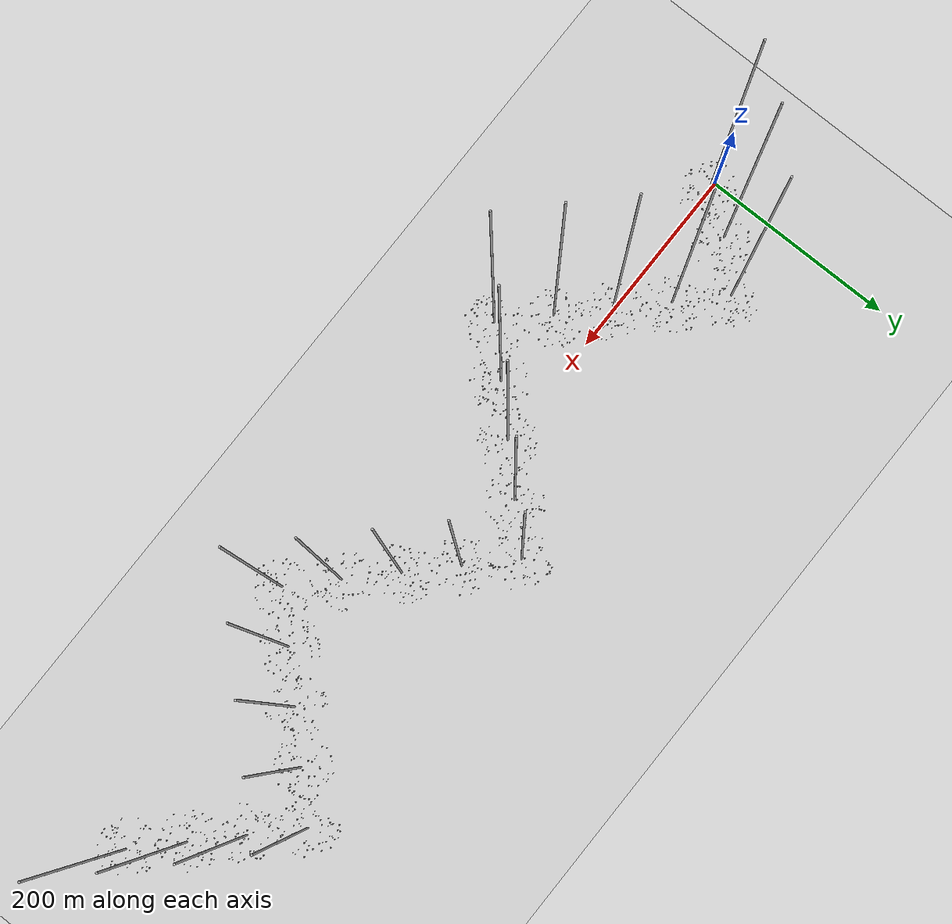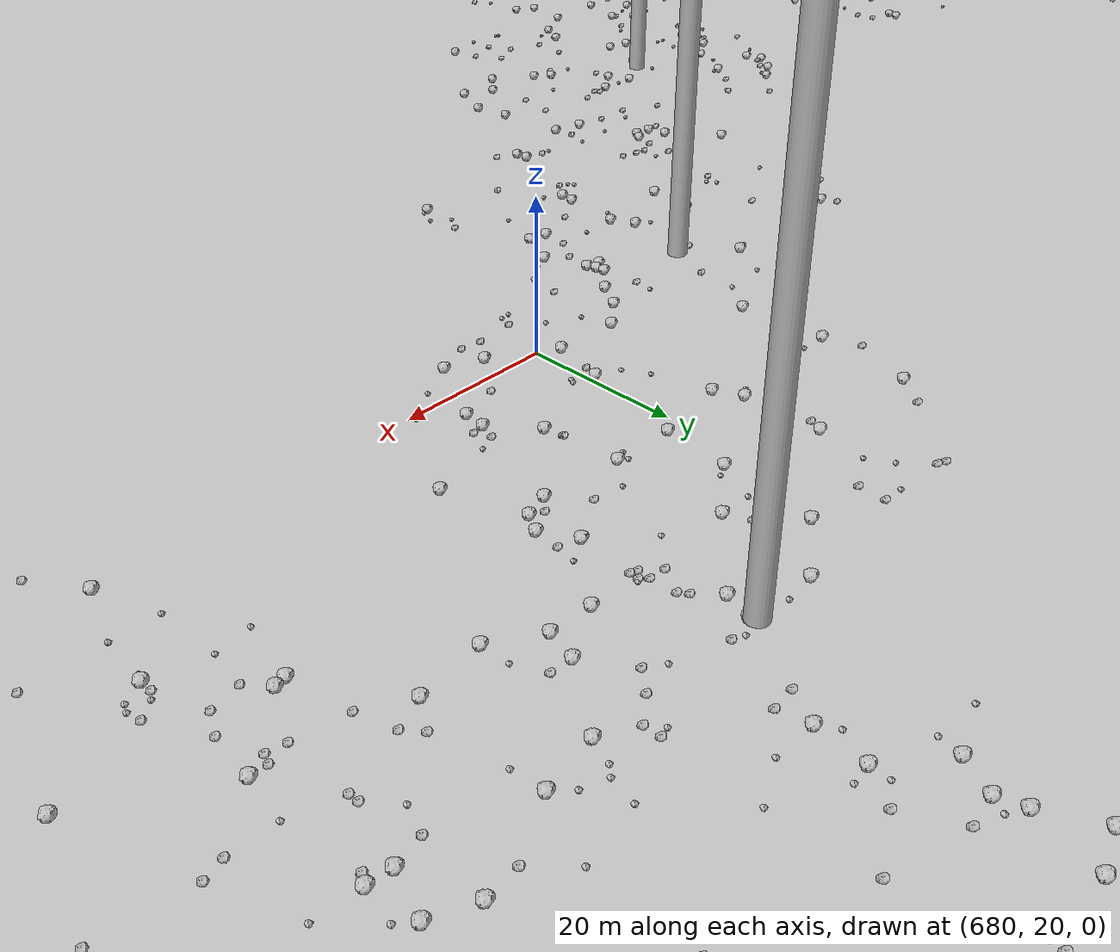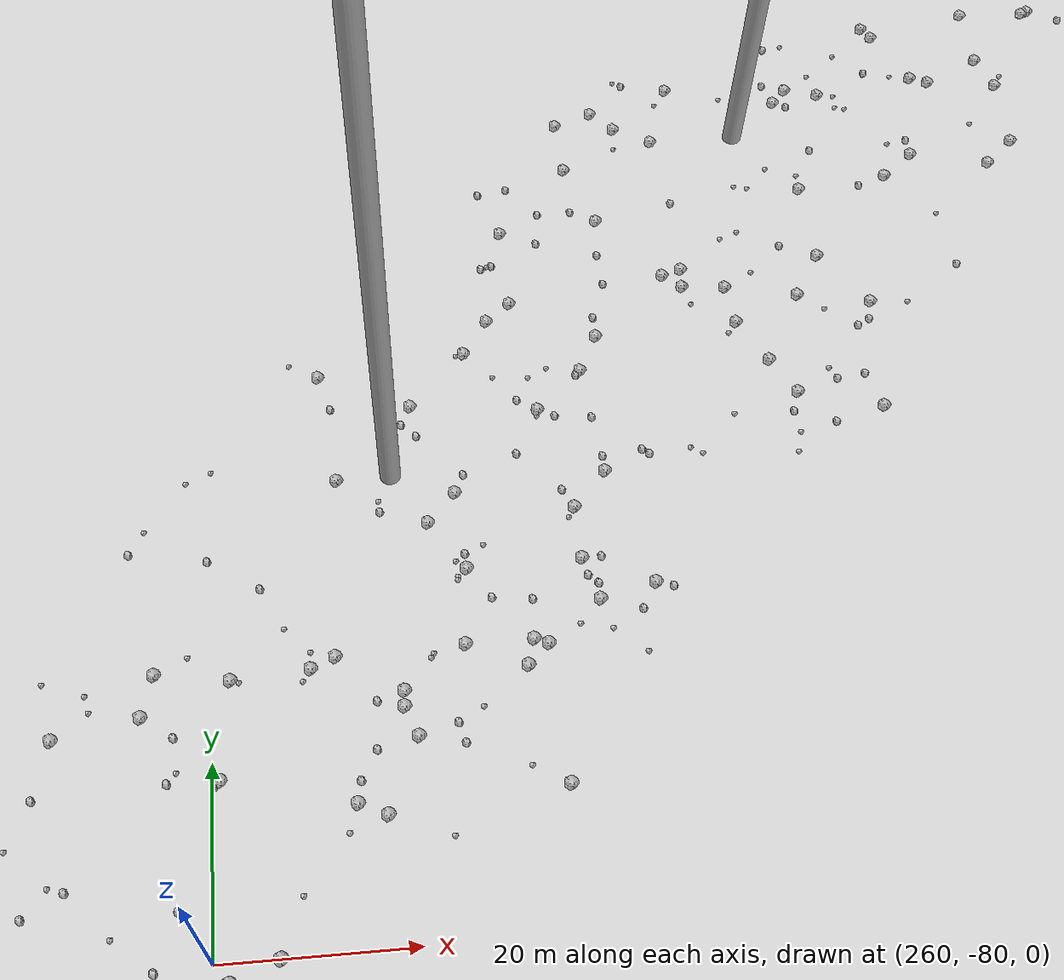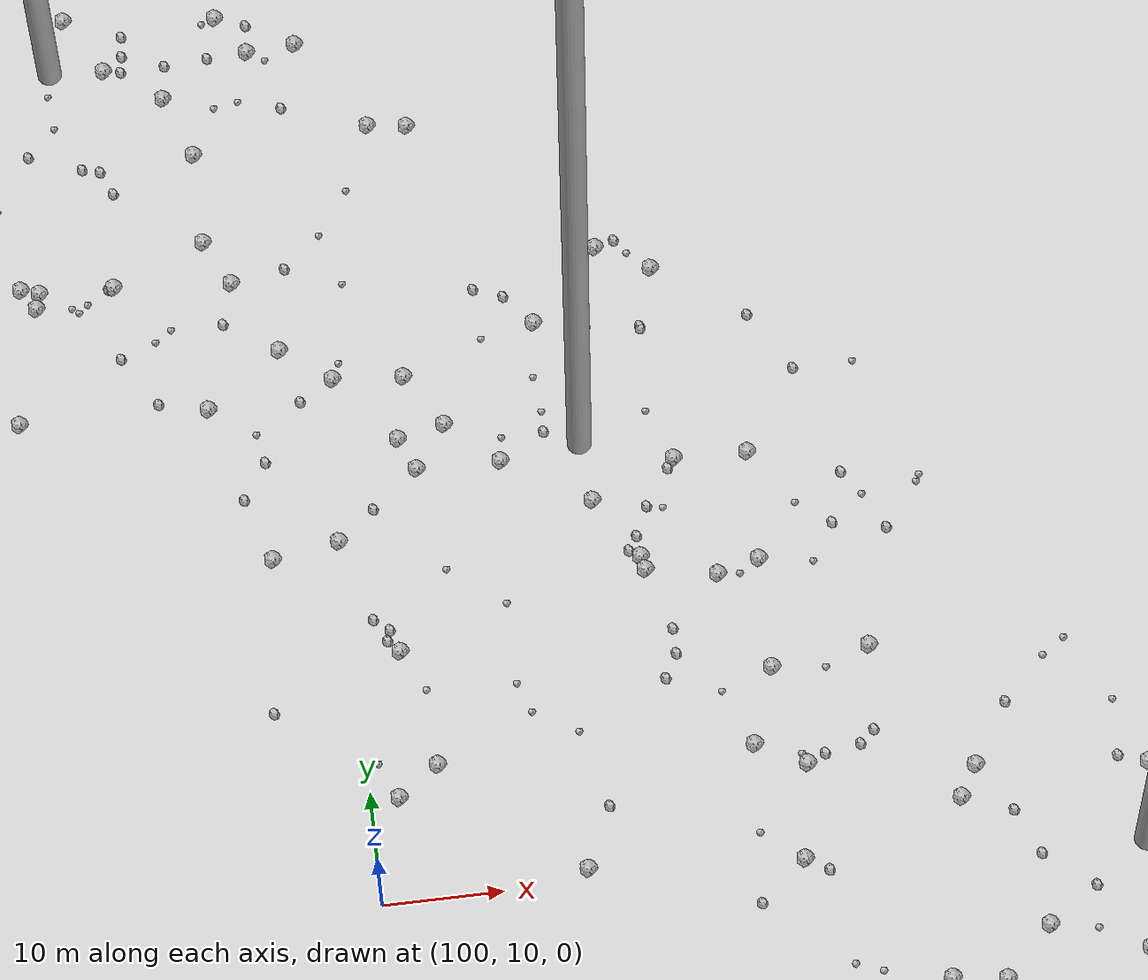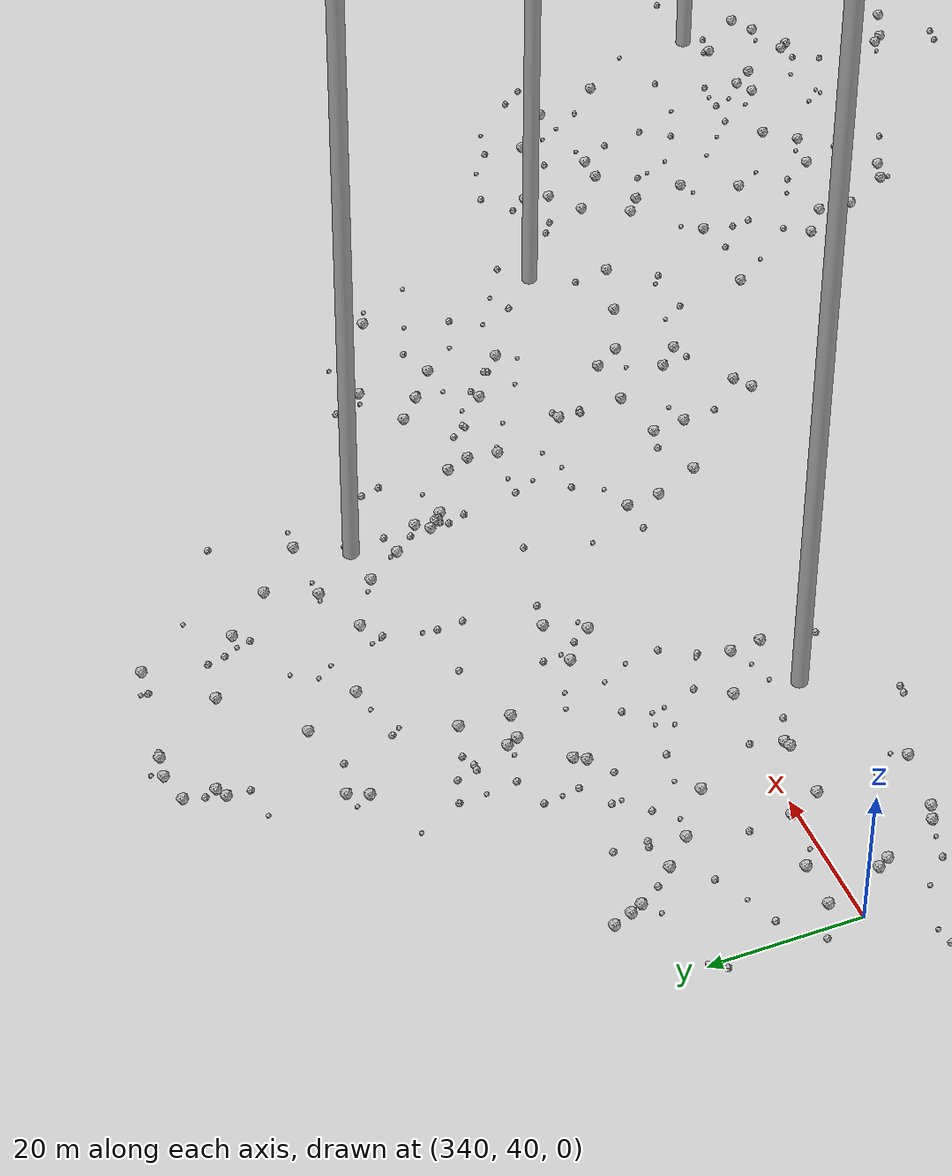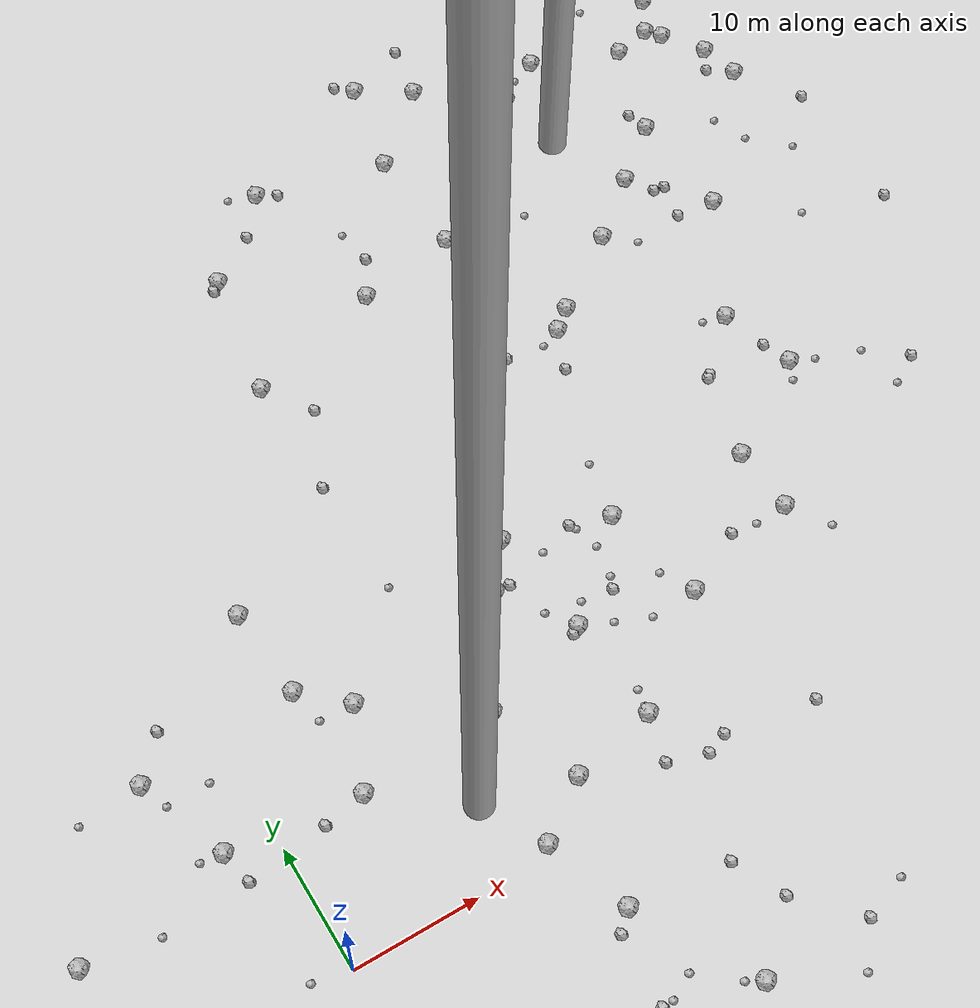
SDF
<sdf version="1.6">
 <world name="default">
  <include><uri>model://custom_ground</uri></include>
  <include><uri>model://sun</uri></include>
  <spherical_coordinates>
   <surface_model>EARTH_WGS84</surface_model>
   <latitude_deg>38.161479</latitude_deg>
   <longitude_deg>-122.454630</longitude_deg>
   <elevation>488.0</elevation>
   <heading_deg>90</heading_deg>
  </spherical_coordinates>
  <model name="rock1_0_0">
   <include><uri>model://rock1</uri><pose>7.059993198461207 -23.64071983949531 0.5 0 0 0</pose></include>
  </model>
  <model name="rock1_0_1">
   <include><uri>model://rock1</uri><pose>-9.568092358396786 -2.085759764088259 0.5 0 0 0</pose></include>
  </model>
  <model name="rock1_0_2">
   <include><uri>model://rock1</uri><pose>6.840591712603505 10.629788791995992 0.5 0 0 0</pose></include>
  </model>
  <model name="rock1_0_3">
   <include><uri>model://rock1</uri><pose>5.627926370117663 27.479701073414965 0.5 0 0 0</pose></include>
  </model>
  <model name="rock1_0_4">
   <include><uri>model://rock1</uri><pose>18.518322437376803 -5.965348976231368 0.5 0 0 0</pose></include>
  </model>
  <model name="rock1_0_5">
   <include><uri>model://rock1</uri><pose>25.6214100346198 22.834676432462203 0.5 0 0 0</pose></include>
  </model>
  <model name="rock1_0_6">
   <include><uri>model://rock1</uri><pose>6.199511335580869 20.042120135440555 0.5 0 0 0</pose></include>
  </model>
  <model name="rock1_0_7">
   <include><uri>model://rock1</uri><pose>20.66579332794779 3.937702179982928 0.5 0 0 0</pose></include>
  </model>
  <model name="rock1_0_8">
   <include><uri>model://rock1</uri><pose>23.802954450742455 -15.059992954827841 0.5 0 0 0</pose></include>
  </model>
  <model name="rock1_0_9">
   <include><uri>model://rock1</uri><pose>3.9915463095161208 -26.31926876083099 0.5 0 0 0</pose></include>
  </model>
  <model name="rock1_0_10">
   <include><uri>model://rock1</uri><pose>9.576335678490484 16.962011957994797 0.5 0 0 0</pose></include>
  </model>
  <model name="rock1_0_11">
   <include><uri>model://rock1</uri><pose>-16.010344355347623 9.624958255148577 0.5 0 0 0</pose></include>
  </model>
  <model name="rock1_0_12">
   <include><uri>model://rock1</uri><pose>18.586679443699495 -15.92293498312267 0.5 0 0 0</pose></include>
  </model>
  <model name="rock1_0_13">
   <include><uri>model://rock1</uri><pose>0.41128462244657626 -18.943184868657614 0.5 0 0 0</pose></include>
  </model>
  <model name="rock1_0_14">
   <include><uri>model://rock1</uri><pose>22.988245397435826 19.38813448388911 0.5 0 0 0</pose></include>
  </model>
  <model name="rock1_0_15">
   <include><uri>model://rock1</uri><pose>27.56408539392359 5.390570040301313 0.5 0 0 0</pose></include>
  </model>
  <model name="rock1_0_16">
   <include><uri>model://rock1</uri><pose>-19.473209041985054 -2.2118726432222857 0.5 0 0 0</pose></include>
  </model>
  <model name="rock1_0_17">
   <include><uri>model://rock1</uri><pose>-11.0303805275637 -12.880461278430666 0.5 0 0 0</pose></include>
  </model>
  <model name="rock1_0_18">
   <include><uri>model://rock1</uri><pose>-0.2663588980556355 -10.290820505903241 0.5 0 0 0</pose></include>
  </model>
  <model name="rock1_0_19">
   <include><uri>model://rock1</uri><pose>17.871828647298443 11.274585472599675 0.5 0 0 0</pose></include>
  </model>
  <model name="rock1_0_20">
   <include><uri>model://rock1</uri><pose>-10.627030978070529 -14.202094108196084 0.5 0 0 0</pose></include>
  </model>
  <model name="rock1_0_21">
   <include><uri>model://rock1</uri><pose>-3.749795722601508 11.82701933616682 0.5 0 0 0</pose></include>
  </model>
  <model name="rock1_0_22">
   <include><uri>model://rock1</uri><pose>-6.530196266650703 19.268809205259785 0.5 0 0 0</pose></include>
  </model>
  <model name="rock1_0_23">
   <include><uri>model://rock1</uri><pose>-15.321919436845521 -5.594823327682683 0.5 0 0 0</pose></include>
  </model>
  <model name="rock1_0_24">
   <include><uri>model://rock1</uri><pose>-7.580302732434676 -20.56496442065791 0.5 0 0 0</pose></include>
  </model>
  <model name="rock1_0_25">
   <include><uri>model://rock1</uri><pose>-2.3601899936401125 -15.168892355950154 0.5 0 0 0</pose></include>
  </model>
  <model name="rock1_0_26">
   <include><uri>model://rock1</uri><pose>16.136326328450913 0.7407939559058647 0.5 0 0 0</pose></include>
  </model>
  <model name="rock2_0_0">
   <include><uri>model://rock2</uri><pose>15.069073525620695 -14.724736662522373 0.3 0 0 0</pose></include>
  </model>
  <model name="rock2_0_1">
   <include><uri>model://rock2</uri><pose>32.51958757648092 -15.112338030089173 0.3 0 0 0</pose></include>
  </model>
  <model name="rock2_0_2">
   <include><uri>model://rock2</uri><pose>16.48108537741161 -17.834315164622552 0.3 0 0 0</pose></include>
  </model>
  <model name="rock2_0_3">
   <include><uri>model://rock2</uri><pose>26.55737258562337 1.6203192060827334 0.3 0 0 0</pose></include>
  </model>
  <model name="rock2_0_4">
   <include><uri>model://rock2</uri><pose>-6.0552937582442805 -0.7741367525558012 0.3 0 0 0</pose></include>
  </model>
  <model name="rock2_0_5">
   <include><uri>model://rock2</uri><pose>28.396509532478824 -10.857431025558942 0.3 0 0 0</pose></include>
  </model>
  <model name="rock2_0_6">
   <include><uri>model://rock2</uri><pose>3.883641334240913 -25.39498913512121 0.3 0 0 0</pose></include>
  </model>
  <model name="rock2_0_7">
   <include><uri>model://rock2</uri><pose>3.320729117445616 9.99626235597789 0.3 0 0 0</pose></include>
  </model>
  <model name="rock2_0_8">
   <include><uri>model://rock2</uri><pose>17.061088924010747 -7.282805983142211 0.3 0 0 0</pose></include>
  </model>
  <model name="rock2_0_9">
   <include><uri>model://rock2</uri><pose>0.1492210190474843 -7.176487407325631 0.3 0 0 0</pose></include>
  </model>
  <model name="rock2_0_10">
   <include><uri>model://rock2</uri><pose>11.872134308161026 -26.514324002909365 0.3 0 0 0</pose></include>
  </model>
  <model name="rock2_0_11">
   <include><uri>model://rock2</uri><pose>-14.26947701446145 -15.510794339589282 0.3 0 0 0</pose></include>
  </model>
  <model name="rock2_0_12">
   <include><uri>model://rock2</uri><pose>31.390063689175847 1.2991845364672372 0.3 0 0 0</pose></include>
  </model>
  <model name="rock2_0_13">
   <include><uri>model://rock2</uri><pose>-16.65633445517154 -11.294478058561111 0.3 0 0 0</pose></include>
  </model>
  <model name="rock2_0_14">
   <include><uri>model://rock2</uri><pose>14.269674608735713 7.379101866552716 0.3 0 0 0</pose></include>
  </model>
  <model name="rock2_0_15">
   <include><uri>model://rock2</uri><pose>-1.383004183925184 -5.1149083870121075 0.3 0 0 0</pose></include>
  </model>
  <model name="rock2_0_16">
   <include><uri>model://rock2</uri><pose>38.637093554763624 0.08119987647764049 0.3 0 0 0</pose></include>
  </model>
  <model name="rock2_0_17">
   <include><uri>model://rock2</uri><pose>-2.6726784793421388 -19.729015173731987 0.3 0 0 0</pose></include>
  </model>
  <model name="rock2_0_18">
   <include><uri>model://rock2</uri><pose>30.668259349428936 15.125497853353785 0.3 0 0 0</pose></include>
  </model>
  <model name="rock2_0_19">
   <include><uri>model://rock2</uri><pose>-3.2194349454690823 9.146012693063007 0.3 0 0 0</pose></include>
  </model>
  <model name="rock2_0_20">
   <include><uri>model://rock2</uri><pose>23.140299771550296 -20.848790741307255 0.3 0 0 0</pose></include>
  </model>
  <model name="rock2_0_21">
   <include><uri>model://rock2</uri><pose>26.470240273715916 -6.850473676895586 0.3 0 0 0</pose></include>
  </model>
  <model name="rock2_0_22">
   <include><uri>model://rock2</uri><pose>-17.698132189384634 -10.790020475652959 0.3 0 0 0</pose></include>
  </model>
  <model name="rock2_0_23">
   <include><uri>model://rock2</uri><pose>16.754225942959238 -12.97385489678544 0.3 0 0 0</pose></include>
  </model>
  <model name="rock2_0_24">
   <include><uri>model://rock2</uri><pose>7.775349696814217 -25.340304778377515 0.3 0 0 0</pose></include>
  </model>
  <model name="rock2_0_25">
   <include><uri>model://rock2</uri><pose>-3.708626882464614 22.422890890262934 0.3 0 0 0</pose></include>
  </model>
  <model name="rock2_0_26">
   <include><uri>model://rock2</uri><pose>29.651493915125968 0.6278206416437051 0.3 0 0 0</pose></include>
  </model>
  <model name="rock3_0_0">
   <include><uri>model://rock3</uri><pose>2.3491898193643763 -9.204442021694785 0.2 0 0 0</pose></include>
  </model>
  <model name="rock3_0_1">
   <include><uri>model://rock3</uri><pose>22.540001000702155 -14.354614490306323 0.2 0 0 0</pose></include>
  </model>
  <model name="rock3_0_2">
   <include><uri>model://rock3</uri><pose>6.76027536625449 17.09674335481332 0.2 0 0 0</pose></include>
  </model>
  <model name="rock3_0_3">
   <include><uri>model://rock3</uri><pose>17.63395830533593 -12.945799859115933 0.2 0 0 0</pose></include>
  </model>
  <model name="rock3_0_4">
   <include><uri>model://rock3</uri><pose>30.996342904605953 20.752376255228384 0.2 0 0 0</pose></include>
  </model>
  <model name="rock3_0_5">
   <include><uri>model://rock3</uri><pose>25.27329474382352 16.01890466998219 0.2 0 0 0</pose></include>
  </model>
  <model name="rock3_0_6">
   <include><uri>model://rock3</uri><pose>-10.184243388724695 8.697460794329842 0.2 0 0 0</pose></include>
  </model>
  <model name="rock3_0_7">
   <include><uri>model://rock3</uri><pose>27.63385572935634 6.032230618103121 0.2 0 0 0</pose></include>
  </model>
  <model name="rock3_0_8">
   <include><uri>model://rock3</uri><pose>27.89360442906701 7.340562814018128 0.2 0 0 0</pose></include>
  </model>
  <model name="rock3_0_9">
   <include><uri>model://rock3</uri><pose>-11.69704544032765 18.81299046612149 0.2 0 0 0</pose></include>
  </model>
  <model name="rock3_0_10">
   <include><uri>model://rock3</uri><pose>19.604710237813755 -11.953021993956867 0.2 0 0 0</pose></include>
  </model>
  <model name="rock3_0_11">
   <include><uri>model://rock3</uri><pose>-2.9542688025850303 0.6509883253992825 0.2 0 0 0</pose></include>
  </model>
  <model name="rock3_0_12">
   <include><uri>model://rock3</uri><pose>-12.297508838309962 -1.8343771354056813 0.2 0 0 0</pose></include>
  </model>
  <model name="rock3_0_13">
   <include><uri>model://rock3</uri><pose>23.506489510594974 22.658001637295342 0.2 0 0 0</pose></include>
  </model>
  <model name="rock3_0_14">
   <include><uri>model://rock3</uri><pose>32.02199600468727 11.654387419008863 0.2 0 0 0</pose></include>
  </model>
  <model name="rock3_0_15">
   <include><uri>model://rock3</uri><pose>-2.2530010675151466 16.99038574288295 0.2 0 0 0</pose></include>
  </model>
  <model name="rock3_0_16">
   <include><uri>model://rock3</uri><pose>-1.4236597128311637 -25.31300417117661 0.2 0 0 0</pose></include>
  </model>
  <model name="rock3_0_17">
   <include><uri>model://rock3</uri><pose>34.434485156192096 14.422585442885506 0.2 0 0 0</pose></include>
  </model>
  <model name="rock3_0_18">
   <include><uri>model://rock3</uri><pose>31.53746357383241 18.728612410817604 0.2 0 0 0</pose></include>
  </model>
  <model name="rock3_0_19">
   <include><uri>model://rock3</uri><pose>36.054003719134265 -13.89294485163197 0.2 0 0 0</pose></include>
  </model>
  <model name="rock3_0_20">
   <include><uri>model://rock3</uri><pose>30.113435440407834 -18.160314556097575 0.2 0 0 0</pose></include>
  </model>
  <model name="rock3_0_21">
   <include><uri>model://rock3</uri><pose>19.56590660782988 16.36666605894775 0.2 0 0 0</pose></include>
  </model>
  <model name="rock3_0_22">
   <include><uri>model://rock3</uri><pose>18.30201429230945 -20.837630148522447 0.2 0 0 0</pose></include>
  </model>
  <model name="rock3_0_23">
   <include><uri>model://rock3</uri><pose>29.326698762538747 12.777142175874182 0.2 0 0 0</pose></include>
  </model>
  <model name="rock3_0_24">
   <include><uri>model://rock3</uri><pose>-5.571568618815636 12.082470296424923 0.2 0 0 0</pose></include>
  </model>
  <model name="rock3_0_25">
   <include><uri>model://rock3</uri><pose>14.261177294668123 -18.935753475739503 0.2 0 0 0</pose></include>
  </model>
  <model name="rock3_0_26">
   <include><uri>model://rock3</uri><pose>-5.679746149901316 16.968934796247247 0.2 0 0 0</pose></include>
  </model>
  <model name="rock1_1_0">
   <include><uri>model://rock1</uri><pose>44.71186113507495 58.1508104255363 0.5 0 0 0</pose></include>
  </model>
  <model name="rock1_1_1">
   <include><uri>model://rock1</uri><pose>51.394780417824904 30.7356118097852 0.5 0 0 0</pose></include>
  </model>
  <model name="rock1_1_2">
   <include><uri>model://rock1</uri><pose>45.40947985975863 19.684011808444467 0.5 0 0 0</pose></include>
  </model>
  <model name="rock1_1_3">
   <include><uri>model://rock1</uri><pose>39.17148773507366 36.5216261235516 0.5 0 0 0</pose></include>
  </model>
  <model name="rock1_1_4">
   <include><uri>model://rock1</uri><pose>56.12771825821578 49.78136947864973 0.5 0 0 0</pose></include>
  </model>
  <model name="rock1_1_5">
   <include><uri>model://rock1</uri><pose>51.75003449202899 46.18462446247731 0.5 0 0 0</pose></include>
  </model>
  <model name="rock1_1_6">
   <include><uri>model://rock1</uri><pose>58.5634937569657 57.74514496456257 0.5 0 0 0</pose></include>
  </model>
  <model name="rock1_1_7">
   <include><uri>model://rock1</uri><pose>17.979006575609418 54.44468877481421 0.5 0 0 0</pose></include>
  </model>
  <model name="rock1_1_8">
   <include><uri>model://rock1</uri><pose>47.05335207819954 42.27135350958126 0.5 0 0 0</pose></include>
  </model>
  <model name="rock1_1_9">
   <include><uri>model://rock1</uri><pose>24.6297036874613 60.41508944370901 0.5 0 0 0</pose></include>
  </model>
  <model name="rock1_1_10">
   <include><uri>model://rock1</uri><pose>40.83948472035921 37.909656217597785 0.5 0 0 0</pose></include>
  </model>
  <model name="rock1_1_11">
   <include><uri>model://rock1</uri><pose>33.92928171062003 20.291207754415936 0.5 0 0 0</pose></include>
  </model>
  <model name="rock1_1_12">
   <include><uri>model://rock1</uri><pose>36.90948540077841 65.7183869628398 0.5 0 0 0</pose></include>
  </model>
  <model name="rock1_1_13">
   <include><uri>model://rock1</uri><pose>35.88729265560622 48.56370043890471 0.5 0 0 0</pose></include>
  </model>
  <model name="rock1_1_14">
   <include><uri>model://rock1</uri><pose>35.353502905537184 57.78033278862965 0.5 0 0 0</pose></include>
  </model>
  <model name="rock1_1_15">
   <include><uri>model://rock1</uri><pose>26.86522443289799 13.859882388581916 0.5 0 0 0</pose></include>
  </model>
  <model name="rock1_1_16">
   <include><uri>model://rock1</uri><pose>51.37944165477731 60.55809606932315 0.5 0 0 0</pose></include>
  </model>
  <model name="rock1_1_17">
   <include><uri>model://rock1</uri><pose>27.626156808939637 47.115147726901 0.5 0 0 0</pose></include>
  </model>
  <model name="rock1_1_18">
   <include><uri>model://rock1</uri><pose>35.881550102753955 11.842458467081576 0.5 0 0 0</pose></include>
  </model>
  <model name="rock1_1_19">
   <include><uri>model://rock1</uri><pose>47.51882275125549 58.307276459497565 0.5 0 0 0</pose></include>
  </model>
  <model name="rock1_1_20">
   <include><uri>model://rock1</uri><pose>53.395037705006715 24.67810729378521 0.5 0 0 0</pose></include>
  </model>
  <model name="rock1_1_21">
   <include><uri>model://rock1</uri><pose>65.85763201482108 50.88677878498069 0.5 0 0 0</pose></include>
  </model>
  <model name="rock1_1_22">
   <include><uri>model://rock1</uri><pose>45.726756982184206 14.268047344110355 0.5 0 0 0</pose></include>
  </model>
  <model name="rock1_1_23">
   <include><uri>model://rock1</uri><pose>56.787159891825446 40.54290680318121 0.5 0 0 0</pose></include>
  </model>
  <model name="rock1_1_24">
   <include><uri>model://rock1</uri><pose>41.185120732971335 63.06023040475939 0.5 0 0 0</pose></include>
  </model>
  <model name="rock1_1_25">
   <include><uri>model://rock1</uri><pose>16.27638231325032 43.81538097733383 0.5 0 0 0</pose></include>
  </model>
  <model name="rock1_1_26">
   <include><uri>model://rock1</uri><pose>62.70532884331663 57.3577895456798 0.5 0 0 0</pose></include>
  </model>
  <model name="rock2_1_0">
   <include><uri>model://rock2</uri><pose>17.240914818941107 53.90753325970786 0.3 0 0 0</pose></include>
  </model>
  <model name="rock2_1_1">
   <include><uri>model://rock2</uri><pose>24.229018808487606 19.35254823530822 0.3 0 0 0</pose></include>
  </model>
  <model name="rock2_1_2">
   <include><uri>model://rock2</uri><pose>31.18676250017236 34.008087621340955 0.3 0 0 0</pose></include>
  </model>
  <model name="rock2_1_3">
   <include><uri>model://rock2</uri><pose>40.908638013669396 14.427807728940572 0.3 0 0 0</pose></include>
  </model>
  <model name="rock2_1_4">
   <include><uri>model://rock2</uri><pose>54.14479375938863 43.962345112274505 0.3 0 0 0</pose></include>
  </model>
  <model name="rock2_1_5">
   <include><uri>model://rock2</uri><pose>53.53500916101769 40.97454030666458 0.3 0 0 0</pose></include>
  </model>
  <model name="rock2_1_6">
   <include><uri>model://rock2</uri><pose>46.97373569306396 26.718396967418688 0.3 0 0 0</pose></include>
  </model>
  <model name="rock2_1_7">
   <include><uri>model://rock2</uri><pose>26.15437223514727 59.657348595513845 0.3 0 0 0</pose></include>
  </model>
  <model name="rock2_1_8">
   <include><uri>model://rock2</uri><pose>41.983478595892265 67.71590950323736 0.3 0 0 0</pose></include>
  </model>
  <model name="rock2_1_9">
   <include><uri>model://rock2</uri><pose>69.33979214128041 33.93696611088646 0.3 0 0 0</pose></include>
  </model>
  <model name="rock2_1_10">
   <include><uri>model://rock2</uri><pose>53.18593316612871 44.11093904889503 0.3 0 0 0</pose></include>
  </model>
  <model name="rock2_1_11">
   <include><uri>model://rock2</uri><pose>69.35526036295119 45.871559308186065 0.3 0 0 0</pose></include>
  </model>
  <model name="rock2_1_12">
   <include><uri>model://rock2</uri><pose>18.909254552180904 40.06301600176743 0.3 0 0 0</pose></include>
  </model>
  <model name="rock2_1_13">
   <include><uri>model://rock2</uri><pose>52.48497344692587 27.044517662235606 0.3 0 0 0</pose></include>
  </model>
  <model name="rock2_1_14">
   <include><uri>model://rock2</uri><pose>37.765982405929634 33.19586342998103 0.3 0 0 0</pose></include>
  </model>
  <model name="rock2_1_15">
   <include><uri>model://rock2</uri><pose>63.94080413674957 52.36565149791096 0.3 0 0 0</pose></include>
  </model>
  <model name="rock2_1_16">
   <include><uri>model://rock2</uri><pose>62.011789831644265 20.227047887886904 0.3 0 0 0</pose></include>
  </model>
  <model name="rock2_1_17">
   <include><uri>model://rock2</uri><pose>26.19845859951947 13.523904144348855 0.3 0 0 0</pose></include>
  </model>
  <model name="rock2_1_18">
   <include><uri>model://rock2</uri><pose>34.276772082502305 36.39124055028573 0.3 0 0 0</pose></include>
  </model>
  <model name="rock2_1_19">
   <include><uri>model://rock2</uri><pose>47.30023815147804 26.91090121253939 0.3 0 0 0</pose></include>
  </model>
  <model name="rock2_1_20">
   <include><uri>model://rock2</uri><pose>16.159585030677995 33.731258909468025 0.3 0 0 0</pose></include>
  </model>
  <model name="rock2_1_21">
   <include><uri>model://rock2</uri><pose>40.906228495624795 50.79624012258773 0.3 0 0 0</pose></include>
  </model>
  <model name="rock2_1_22">
   <include><uri>model://rock2</uri><pose>29.295693163223753 50.38275521303988 0.3 0 0 0</pose></include>
  </model>
  <model name="rock2_1_23">
   <include><uri>model://rock2</uri><pose>21.99495157658621 57.232568277315636 0.3 0 0 0</pose></include>
  </model>
  <model name="rock2_1_24">
   <include><uri>model://rock2</uri><pose>55.6060945093577 51.69320231709255 0.3 0 0 0</pose></include>
  </model>
  <model name="rock2_1_25">
   <include><uri>model://rock2</uri><pose>35.560459041341275 66.98876464555593 0.3 0 0 0</pose></include>
  </model>
  <model name="rock2_1_26">
   <include><uri>model://rock2</uri><pose>30.683889995557227 21.305175654055148 0.3 0 0 0</pose></include>
  </model>
  <model name="rock3_1_0">
   <include><uri>model://rock3</uri><pose>49.224032761585406 59.74451698671685 0.2 0 0 0</pose></include>
  </model>
  <model name="rock3_1_1">
   <include><uri>model://rock3</uri><pose>38.960434248997885 49.49297653476292 0.2 0 0 0</pose></include>
  </model>
  <model name="rock3_1_2">
   <include><uri>model://rock3</uri><pose>61.55393253275431 47.522131234024805 0.2 0 0 0</pose></include>
  </model>
  <model name="rock3_1_3">
   <include><uri>model://rock3</uri><pose>28.815295215449925 53.37502028927569 0.2 0 0 0</pose></include>
  </model>
  <model name="rock3_1_4">
   <include><uri>model://rock3</uri><pose>28.115678698258016 15.444441030242666 0.2 0 0 0</pose></include>
  </model>
  <model name="rock3_1_5">
   <include><uri>model://rock3</uri><pose>37.4207013567093 35.87837091591919 0.2 0 0 0</pose></include>
  </model>
  <model name="rock3_1_6">
   <include><uri>model://rock3</uri><pose>49.30271804894849 40.41961539409739 0.2 0 0 0</pose></include>
  </model>
  <model name="rock3_1_7">
   <include><uri>model://rock3</uri><pose>43.03817308538851 14.13465032344837 0.2 0 0 0</pose></include>
  </model>
  <model name="rock3_1_8">
   <include><uri>model://rock3</uri><pose>55.308486779140935 23.86665481893518 0.2 0 0 0</pose></include>
  </model>
  <model name="rock3_1_9">
   <include><uri>model://rock3</uri><pose>44.15985393173124 55.506029535716394 0.2 0 0 0</pose></include>
  </model>
  <model name="rock3_1_10">
   <include><uri>model://rock3</uri><pose>65.75571122751839 41.93813268707015 0.2 0 0 0</pose></include>
  </model>
  <model name="rock3_1_11">
   <include><uri>model://rock3</uri><pose>56.09350960888552 49.45712045643221 0.2 0 0 0</pose></include>
  </model>
  <model name="rock3_1_12">
   <include><uri>model://rock3</uri><pose>16.3376078625776 23.804629700255923 0.2 0 0 0</pose></include>
  </model>
  <model name="rock3_1_13">
   <include><uri>model://rock3</uri><pose>34.84417429442672 24.977156000512505 0.2 0 0 0</pose></include>
  </model>
  <model name="rock3_1_14">
   <include><uri>model://rock3</uri><pose>58.91158976332889 22.61360685405116 0.2 0 0 0</pose></include>
  </model>
  <model name="rock3_1_15">
   <include><uri>model://rock3</uri><pose>47.916357624850846 11.083512648343717 0.2 0 0 0</pose></include>
  </model>
  <model name="rock3_1_16">
   <include><uri>model://rock3</uri><pose>62.50520957537654 35.96666819100263 0.2 0 0 0</pose></include>
  </model>
  <model name="rock3_1_17">
   <include><uri>model://rock3</uri><pose>49.52484379310969 31.257249164774944 0.2 0 0 0</pose></include>
  </model>
  <model name="rock3_1_18">
   <include><uri>model://rock3</uri><pose>27.798876489284023 20.36113598489353 0.2 0 0 0</pose></include>
  </model>
  <model name="rock3_1_19">
   <include><uri>model://rock3</uri><pose>31.09902880207081 16.090960055569973 0.2 0 0 0</pose></include>
  </model>
  <model name="rock3_1_20">
   <include><uri>model://rock3</uri><pose>59.6162992718881 18.749945560044786 0.2 0 0 0</pose></include>
  </model>
  <model name="rock3_1_21">
   <include><uri>model://rock3</uri><pose>42.67427594021444 47.42395747011831 0.2 0 0 0</pose></include>
  </model>
  <model name="rock3_1_22">
   <include><uri>model://rock3</uri><pose>50.236297472879755 55.836178868777026 0.2 0 0 0</pose></include>
  </model>
  <model name="rock3_1_23">
   <include><uri>model://rock3</uri><pose>62.76780891047734 44.64513482100253 0.2 0 0 0</pose></include>
  </model>
  <model name="rock3_1_24">
   <include><uri>model://rock3</uri><pose>58.03384402986927 63.25551514798616 0.2 0 0 0</pose></include>
  </model>
  <model name="rock3_1_25">
   <include><uri>model://rock3</uri><pose>22.366534660601456 61.22384595229815 0.2 0 0 0</pose></include>
  </model>
  <model name="rock3_1_26">
   <include><uri>model://rock3</uri><pose>52.68100772467441 23.140355779419792 0.2 0 0 0</pose></include>
  </model>
  <model name="rock1_2_0">
   <include><uri>model://rock1</uri><pose>82.87509532214318 69.83127865599229 0.5 0 0 0</pose></include>
  </model>
  <model name="rock1_2_1">
   <include><uri>model://rock1</uri><pose>109.6987109105419 82.73388172267181 0.5 0 0 0</pose></include>
  </model>
  <model name="rock1_2_2">
   <include><uri>model://rock1</uri><pose>96.48764583870847 61.95135396894465 0.5 0 0 0</pose></include>
  </model>
  <model name="rock1_2_3">
   <include><uri>model://rock1</uri><pose>90.894207895633 82.13583591915335 0.5 0 0 0</pose></include>
  </model>
  <model name="rock1_2_4">
   <include><uri>model://rock1</uri><pose>80.6227995871154 97.16046361202797 0.5 0 0 0</pose></include>
  </model>
  <model name="rock1_2_5">
   <include><uri>model://rock1</uri><pose>68.1287975550139 90.59879896679911 0.5 0 0 0</pose></include>
  </model>
  <model name="rock1_2_6">
   <include><uri>model://rock1</uri><pose>84.69752525257047 103.13897191952567 0.5 0 0 0</pose></include>
  </model>
  <model name="rock1_2_7">
   <include><uri>model://rock1</uri><pose>50.552482948898984 74.70082278603218 0.5 0 0 0</pose></include>
  </model>
  <model name="rock1_2_8">
   <include><uri>model://rock1</uri><pose>92.99526888601613 69.0063636663987 0.5 0 0 0</pose></include>
  </model>
  <model name="rock1_2_9">
   <include><uri>model://rock1</uri><pose>74.89701299938972 70.52895155660816 0.5 0 0 0</pose></include>
  </model>
  <model name="rock1_2_10">
   <include><uri>model://rock1</uri><pose>73.82561968919455 57.51972070230987 0.5 0 0 0</pose></include>
  </model>
  <model name="rock1_2_11">
   <include><uri>model://rock1</uri><pose>90.94122948644132 73.32640691785429 0.5 0 0 0</pose></include>
  </model>
  <model name="rock1_2_12">
   <include><uri>model://rock1</uri><pose>89.95855325447006 56.996076709035165 0.5 0 0 0</pose></include>
  </model>
  <model name="rock1_2_13">
   <include><uri>model://rock1</uri><pose>98.63962433849048 99.54318215960365 0.5 0 0 0</pose></include>
  </model>
  <model name="rock1_2_14">
   <include><uri>model://rock1</uri><pose>93.99151978121948 95.80918841536592 0.5 0 0 0</pose></include>
  </model>
  <model name="rock1_2_15">
   <include><uri>model://rock1</uri><pose>100.75395520757436 92.27986943864194 0.5 0 0 0</pose></include>
  </model>
  <model name="rock1_2_16">
   <include><uri>model://rock1</uri><pose>61.70490199597205 58.50329408354804 0.5 0 0 0</pose></include>
  </model>
  <model name="rock1_2_17">
   <include><uri>model://rock1</uri><pose>55.71784551730967 69.1327452930742 0.5 0 0 0</pose></include>
  </model>
  <model name="rock1_2_18">
   <include><uri>model://rock1</uri><pose>106.2870554728906 83.21185237119883 0.5 0 0 0</pose></include>
  </model>
  <model name="rock1_2_19">
   <include><uri>model://rock1</uri><pose>64.79781850271267 95.48306231866562 0.5 0 0 0</pose></include>
  </model>
  <model name="rock1_2_20">
   <include><uri>model://rock1</uri><pose>83.76099544726685 91.57858744970719 0.5 0 0 0</pose></include>
  </model>
  <model name="rock1_2_21">
   <include><uri>model://rock1</uri><pose>76.45912975409216 70.02938914377066 0.5 0 0 0</pose></include>
  </model>
  <model name="rock1_2_22">
   <include><uri>model://rock1</uri><pose>96.4782520974484 91.96868326759139 0.5 0 0 0</pose></include>
  </model>
  <model name="rock1_2_23">
   <include><uri>model://rock1</uri><pose>88.72080614614393 88.14592990493307 0.5 0 0 0</pose></include>
  </model>
  <model name="rock1_2_24">
   <include><uri>model://rock1</uri><pose>65.01512605521819 54.15190963687812 0.5 0 0 0</pose></include>
  </model>
  <model name="rock1_2_25">
   <include><uri>model://rock1</uri><pose>63.386446407201305 61.37501353216733 0.5 0 0 0</pose></include>
  </model>
  <model name="rock1_2_26">
   <include><uri>model://rock1</uri><pose>76.10722757848092 68.5745457602422 0.5 0 0 0</pose></include>
  </model>
  <model name="rock2_2_0">
   <include><uri>model://rock2</uri><pose>50.64211460783962 76.2609353588201 0.3 0 0 0</pose></include>
  </model>
  <model name="rock2_2_1">
   <include><uri>model://rock2</uri><pose>60.520113645279785 82.32057702492449 0.3 0 0 0</pose></include>
  </model>
  <model name="rock2_2_2">
   <include><uri>model://rock2</uri><pose>82.92949857722735 62.862239293109084 0.3 0 0 0</pose></include>
  </model>
  <model name="rock2_2_3">
   <include><uri>model://rock2</uri><pose>66.55546169325149 68.78511151229722 0.3 0 0 0</pose></include>
  </model>
  <model name="rock2_2_4">
   <include><uri>model://rock2</uri><pose>85.73936339102916 58.10110346058773 0.3 0 0 0</pose></include>
  </model>
  <model name="rock2_2_5">
   <include><uri>model://rock2</uri><pose>97.67554832896843 69.91277818179174 0.3 0 0 0</pose></include>
  </model>
  <model name="rock2_2_6">
   <include><uri>model://rock2</uri><pose>85.23043415054545 91.39198914074348 0.3 0 0 0</pose></include>
  </model>
  <model name="rock2_2_7">
   <include><uri>model://rock2</uri><pose>82.38061067248007 69.80795618165018 0.3 0 0 0</pose></include>
  </model>
  <model name="rock2_2_8">
   <include><uri>model://rock2</uri><pose>98.91923115499901 86.01322038182252 0.3 0 0 0</pose></include>
  </model>
  <model name="rock2_2_9">
   <include><uri>model://rock2</uri><pose>85.56929015337924 95.01040127429886 0.3 0 0 0</pose></include>
  </model>
  <model name="rock2_2_10">
   <include><uri>model://rock2</uri><pose>82.61792686252383 81.53322436249245 0.3 0 0 0</pose></include>
  </model>
  <model name="rock2_2_11">
   <include><uri>model://rock2</uri><pose>74.4911757138319 99.6792157805501 0.3 0 0 0</pose></include>
  </model>
  <model name="rock2_2_12">
   <include><uri>model://rock2</uri><pose>79.40238804403373 105.31639929738171 0.3 0 0 0</pose></include>
  </model>
  <model name="rock2_2_13">
   <include><uri>model://rock2</uri><pose>96.59615193246823 94.79968609229778 0.3 0 0 0</pose></include>
  </model>
  <model name="rock2_2_14">
   <include><uri>model://rock2</uri><pose>72.54772880516799 95.48155724504102 0.3 0 0 0</pose></include>
  </model>
  <model name="rock2_2_15">
   <include><uri>model://rock2</uri><pose>85.44176257495388 92.98916474641216 0.3 0 0 0</pose></include>
  </model>
  <model name="rock2_2_16">
   <include><uri>model://rock2</uri><pose>76.49586958668444 83.75390344414956 0.3 0 0 0</pose></include>
  </model>
  <model name="rock2_2_17">
   <include><uri>model://rock2</uri><pose>70.99287618881357 95.80080352318566 0.3 0 0 0</pose></include>
  </model>
  <model name="rock2_2_18">
   <include><uri>model://rock2</uri><pose>91.89941924118935 65.14976556420508 0.3 0 0 0</pose></include>
  </model>
  <model name="rock2_2_19">
   <include><uri>model://rock2</uri><pose>97.78234066951617 56.83635881118744 0.3 0 0 0</pose></include>
  </model>
  <model name="rock2_2_20">
   <include><uri>model://rock2</uri><pose>83.58644374653528 79.20602392367063 0.3 0 0 0</pose></include>
  </model>
  <model name="rock2_2_21">
   <include><uri>model://rock2</uri><pose>89.09893237173472 91.54888921412189 0.3 0 0 0</pose></include>
  </model>
  <model name="rock2_2_22">
   <include><uri>model://rock2</uri><pose>84.77559908564211 108.12984122681831 0.3 0 0 0</pose></include>
  </model>
  <model name="rock2_2_23">
   <include><uri>model://rock2</uri><pose>92.91229139253016 91.87664743610384 0.3 0 0 0</pose></include>
  </model>
  <model name="rock2_2_24">
   <include><uri>model://rock2</uri><pose>61.41064304977634 94.46173883121301 0.3 0 0 0</pose></include>
  </model>
  <model name="rock2_2_25">
   <include><uri>model://rock2</uri><pose>81.07571358451109 81.95723555204519 0.3 0 0 0</pose></include>
  </model>
  <model name="rock2_2_26">
   <include><uri>model://rock2</uri><pose>72.66423603665534 106.73583021941349 0.3 0 0 0</pose></include>
  </model>
  <model name="rock3_2_0">
   <include><uri>model://rock3</uri><pose>63.31976352059009 80.29297612407795 0.2 0 0 0</pose></include>
  </model>
  <model name="rock3_2_1">
   <include><uri>model://rock3</uri><pose>85.98796035427543 64.13551777689875 0.2 0 0 0</pose></include>
  </model>
  <model name="rock3_2_2">
   <include><uri>model://rock3</uri><pose>72.07244347126169 70.15391948958793 0.2 0 0 0</pose></include>
  </model>
  <model name="rock3_2_3">
   <include><uri>model://rock3</uri><pose>80.91450710135439 101.91707620966176 0.2 0 0 0</pose></include>
  </model>
  <model name="rock3_2_4">
   <include><uri>model://rock3</uri><pose>78.64919825451729 89.68595732991116 0.2 0 0 0</pose></include>
  </model>
  <model name="rock3_2_5">
   <include><uri>model://rock3</uri><pose>60.75817096355861 100.88722762799134 0.2 0 0 0</pose></include>
  </model>
  <model name="rock3_2_6">
   <include><uri>model://rock3</uri><pose>97.95820309801769 91.08111755668182 0.2 0 0 0</pose></include>
  </model>
  <model name="rock3_2_7">
   <include><uri>model://rock3</uri><pose>61.94441282946534 69.50575349000147 0.2 0 0 0</pose></include>
  </model>
  <model name="rock3_2_8">
   <include><uri>model://rock3</uri><pose>100.94172506902873 72.85822480300918 0.2 0 0 0</pose></include>
  </model>
  <model name="rock3_2_9">
   <include><uri>model://rock3</uri><pose>79.11791845487554 68.30712000057218 0.2 0 0 0</pose></include>
  </model>
  <model name="rock3_2_10">
   <include><uri>model://rock3</uri><pose>73.41923923567076 78.58894012568143 0.2 0 0 0</pose></include>
  </model>
  <model name="rock3_2_11">
   <include><uri>model://rock3</uri><pose>103.74312154629054 77.00726809346243 0.2 0 0 0</pose></include>
  </model>
  <model name="rock3_2_12">
   <include><uri>model://rock3</uri><pose>78.94562893200118 86.35768226575306 0.2 0 0 0</pose></include>
  </model>
  <model name="rock3_2_13">
   <include><uri>model://rock3</uri><pose>95.19790903269487 87.12644270014728 0.2 0 0 0</pose></include>
  </model>
  <model name="rock3_2_14">
   <include><uri>model://rock3</uri><pose>80.25984665316852 100.76252910563795 0.2 0 0 0</pose></include>
  </model>
  <model name="rock3_2_15">
   <include><uri>model://rock3</uri><pose>67.42605412952142 73.67650818442968 0.2 0 0 0</pose></include>
  </model>
  <model name="rock3_2_16">
   <include><uri>model://rock3</uri><pose>73.59493678450761 92.75968294794882 0.2 0 0 0</pose></include>
  </model>
  <model name="rock3_2_17">
   <include><uri>model://rock3</uri><pose>67.66807459709986 90.89738402725443 0.2 0 0 0</pose></include>
  </model>
  <model name="rock3_2_18">
   <include><uri>model://rock3</uri><pose>79.70369773092287 67.8234935747517 0.2 0 0 0</pose></include>
  </model>
  <model name="rock3_2_19">
   <include><uri>model://rock3</uri><pose>61.85371847210923 95.47719331275073 0.2 0 0 0</pose></include>
  </model>
  <model name="rock3_2_20">
   <include><uri>model://rock3</uri><pose>87.40790096557615 65.17055263301265 0.2 0 0 0</pose></include>
  </model>
  <model name="rock3_2_21">
   <include><uri>model://rock3</uri><pose>102.4885662231874 67.8255333986943 0.2 0 0 0</pose></include>
  </model>
  <model name="rock3_2_22">
   <include><uri>model://rock3</uri><pose>80.48728152217166 68.5399859960351 0.2 0 0 0</pose></include>
  </model>
  <model name="rock3_2_23">
   <include><uri>model://rock3</uri><pose>93.0460713116214 86.71653806521333 0.2 0 0 0</pose></include>
  </model>
  <model name="rock3_2_24">
   <include><uri>model://rock3</uri><pose>92.73559009339598 95.43720050278733 0.2 0 0 0</pose></include>
  </model>
  <model name="rock3_2_25">
   <include><uri>model://rock3</uri><pose>62.37643950143527 84.86885150358921 0.2 0 0 0</pose></include>
  </model>
  <model name="rock3_2_26">
   <include><uri>model://rock3</uri><pose>64.40030002289669 65.61459642764012 0.2 0 0 0</pose></include>
  </model>
  <model name="rock1_3_0">
   <include><uri>model://rock1</uri><pose>124.89879860844609 38.62685695090395 0.5 0 0 0</pose></include>
  </model>
  <model name="rock1_3_1">
   <include><uri>model://rock1</uri><pose>106.82088045822925 58.094804124668876 0.5 0 0 0</pose></include>
  </model>
  <model name="rock1_3_2">
   <include><uri>model://rock1</uri><pose>102.3537546439044 19.153691836431825 0.5 0 0 0</pose></include>
  </model>
  <model name="rock1_3_3">
   <include><uri>model://rock1</uri><pose>99.76120665226043 43.14605290794189 0.5 0 0 0</pose></include>
  </model>
  <model name="rock1_3_4">
   <include><uri>model://rock1</uri><pose>134.76439543603294 37.18373262724782 0.5 0 0 0</pose></include>
  </model>
  <model name="rock1_3_5">
   <include><uri>model://rock1</uri><pose>109.78044598512926 53.11230576640747 0.5 0 0 0</pose></include>
  </model>
  <model name="rock1_3_6">
   <include><uri>model://rock1</uri><pose>142.82540198648195 28.081893063561957 0.5 0 0 0</pose></include>
  </model>
  <model name="rock1_3_7">
   <include><uri>model://rock1</uri><pose>105.72497753615377 52.19896688532874 0.5 0 0 0</pose></include>
  </model>
  <model name="rock1_3_8">
   <include><uri>model://rock1</uri><pose>132.13107051696184 20.304737437372005 0.5 0 0 0</pose></include>
  </model>
  <model name="rock1_3_9">
   <include><uri>model://rock1</uri><pose>114.16613115783804 49.03846206770999 0.5 0 0 0</pose></include>
  </model>
  <model name="rock1_3_10">
   <include><uri>model://rock1</uri><pose>135.12323534678882 47.299233875189735 0.5 0 0 0</pose></include>
  </model>
  <model name="rock1_3_11">
   <include><uri>model://rock1</uri><pose>100.76009229566647 58.60393763128456 0.5 0 0 0</pose></include>
  </model>
  <model name="rock1_3_12">
   <include><uri>model://rock1</uri><pose>107.00499537931469 49.17856794147174 0.5 0 0 0</pose></include>
  </model>
  <model name="rock1_3_13">
   <include><uri>model://rock1</uri><pose>103.82817398180586 32.35138642176092 0.5 0 0 0</pose></include>
  </model>
  <model name="rock1_3_14">
   <include><uri>model://rock1</uri><pose>105.82961983924085 21.724809187649647 0.5 0 0 0</pose></include>
  </model>
  <model name="rock1_3_15">
   <include><uri>model://rock1</uri><pose>134.49566084208868 27.08549691206698 0.5 0 0 0</pose></include>
  </model>
  <model name="rock1_3_16">
   <include><uri>model://rock1</uri><pose>94.06733684825734 42.14015707188372 0.5 0 0 0</pose></include>
  </model>
  <model name="rock1_3_17">
   <include><uri>model://rock1</uri><pose>129.16732563769324 65.97667832994837 0.5 0 0 0</pose></include>
  </model>
  <model name="rock1_3_18">
   <include><uri>model://rock1</uri><pose>125.13489617496064 37.37419414287818 0.5 0 0 0</pose></include>
  </model>
  <model name="rock1_3_19">
   <include><uri>model://rock1</uri><pose>136.25631589765368 18.035760038108982 0.5 0 0 0</pose></include>
  </model>
  <model name="rock1_3_20">
   <include><uri>model://rock1</uri><pose>128.82537217658108 47.45245393676292 0.5 0 0 0</pose></include>
  </model>
  <model name="rock1_3_21">
   <include><uri>model://rock1</uri><pose>121.48688320707251 44.3470282469788 0.5 0 0 0</pose></include>
  </model>
  <model name="rock1_3_22">
   <include><uri>model://rock1</uri><pose>117.10290527858406 10.94327663171627 0.5 0 0 0</pose></include>
  </model>
  <model name="rock1_3_23">
   <include><uri>model://rock1</uri><pose>131.14667405506162 36.187023663418316 0.5 0 0 0</pose></include>
  </model>
  <model name="rock1_3_24">
   <include><uri>model://rock1</uri><pose>124.64545840197579 68.60270905249794 0.5 0 0 0</pose></include>
  </model>
  <model name="rock1_3_25">
   <include><uri>model://rock1</uri><pose>122.56399265103697 60.86154217462231 0.5 0 0 0</pose></include>
  </model>
  <model name="rock1_3_26">
   <include><uri>model://rock1</uri><pose>118.4890528970402 61.90421584837426 0.5 0 0 0</pose></include>
  </model>
  <model name="rock2_3_0">
   <include><uri>model://rock2</uri><pose>126.3212556510178 69.18472337272449 0.3 0 0 0</pose></include>
  </model>
  <model name="rock2_3_1">
   <include><uri>model://rock2</uri><pose>127.53124104124885 60.325397004451666 0.3 0 0 0</pose></include>
  </model>
  <model name="rock2_3_2">
   <include><uri>model://rock2</uri><pose>126.70285372556275 29.38423334240483 0.3 0 0 0</pose></include>
  </model>
  <model name="rock2_3_3">
   <include><uri>model://rock2</uri><pose>140.05787197888938 54.869659266220786 0.3 0 0 0</pose></include>
  </model>
  <model name="rock2_3_4">
   <include><uri>model://rock2</uri><pose>140.8468239757634 19.307990880143137 0.3 0 0 0</pose></include>
  </model>
  <model name="rock2_3_5">
   <include><uri>model://rock2</uri><pose>142.74107561220225 44.479245021143775 0.3 0 0 0</pose></include>
  </model>
  <model name="rock2_3_6">
   <include><uri>model://rock2</uri><pose>128.17063316974856 46.65707127887033 0.3 0 0 0</pose></include>
  </model>
  <model name="rock2_3_7">
   <include><uri>model://rock2</uri><pose>116.16252721119409 64.86715751910714 0.3 0 0 0</pose></include>
  </model>
  <model name="rock2_3_8">
   <include><uri>model://rock2</uri><pose>101.88356267559642 35.59084740488027 0.3 0 0 0</pose></include>
  </model>
  <model name="rock2_3_9">
   <include><uri>model://rock2</uri><pose>92.81447575701502 28.049125840628555 0.3 0 0 0</pose></include>
  </model>
  <model name="rock2_3_10">
   <include><uri>model://rock2</uri><pose>103.15906028767911 34.49146719187395 0.3 0 0 0</pose></include>
  </model>
  <model name="rock2_3_11">
   <include><uri>model://rock2</uri><pose>123.95918528751724 39.34019849230185 0.3 0 0 0</pose></include>
  </model>
  <model name="rock2_3_12">
   <include><uri>model://rock2</uri><pose>92.17628252236979 48.081897078309 0.3 0 0 0</pose></include>
  </model>
  <model name="rock2_3_13">
   <include><uri>model://rock2</uri><pose>113.6537931578484 65.87586924093173 0.3 0 0 0</pose></include>
  </model>
  <model name="rock2_3_14">
   <include><uri>model://rock2</uri><pose>141.3418223615392 39.844666744875525 0.3 0 0 0</pose></include>
  </model>
  <model name="rock2_3_15">
   <include><uri>model://rock2</uri><pose>126.717965406774 31.694289962199193 0.3 0 0 0</pose></include>
  </model>
  <model name="rock2_3_16">
   <include><uri>model://rock2</uri><pose>119.49580256400229 16.342438210321802 0.3 0 0 0</pose></include>
  </model>
  <model name="rock2_3_17">
   <include><uri>model://rock2</uri><pose>102.85895156212989 33.509253794778346 0.3 0 0 0</pose></include>
  </model>
  <model name="rock2_3_18">
   <include><uri>model://rock2</uri><pose>136.84626139490072 60.50613748395749 0.3 0 0 0</pose></include>
  </model>
  <model name="rock2_3_19">
   <include><uri>model://rock2</uri><pose>118.10850791193059 51.43151097502751 0.3 0 0 0</pose></include>
  </model>
  <model name="rock2_3_20">
   <include><uri>model://rock2</uri><pose>102.9338345689878 45.88960987933319 0.3 0 0 0</pose></include>
  </model>
  <model name="rock2_3_21">
   <include><uri>model://rock2</uri><pose>125.55140398382042 27.217768498645636 0.3 0 0 0</pose></include>
  </model>
  <model name="rock2_3_22">
   <include><uri>model://rock2</uri><pose>124.75847947274261 40.62773216438343 0.3 0 0 0</pose></include>
  </model>
  <model name="rock2_3_23">
   <include><uri>model://rock2</uri><pose>127.53384011795424 60.53617632616364 0.3 0 0 0</pose></include>
  </model>
  <model name="rock2_3_24">
   <include><uri>model://rock2</uri><pose>125.94886712538005 43.29288838244781 0.3 0 0 0</pose></include>
  </model>
  <model name="rock2_3_25">
   <include><uri>model://rock2</uri><pose>94.26404921435432 51.43416773500009 0.3 0 0 0</pose></include>
  </model>
  <model name="rock2_3_26">
   <include><uri>model://rock2</uri><pose>145.85666752985026 38.83108883968289 0.3 0 0 0</pose></include>
  </model>
  <model name="rock3_3_0">
   <include><uri>model://rock3</uri><pose>113.16108809030857 28.31465170580838 0.2 0 0 0</pose></include>
  </model>
  <model name="rock3_3_1">
   <include><uri>model://rock3</uri><pose>135.88245654283267 19.033144846291158 0.2 0 0 0</pose></include>
  </model>
  <model name="rock3_3_2">
   <include><uri>model://rock3</uri><pose>114.47369795871845 51.31867430660714 0.2 0 0 0</pose></include>
  </model>
  <model name="rock3_3_3">
   <include><uri>model://rock3</uri><pose>132.99430305362225 36.09505044746916 0.2 0 0 0</pose></include>
  </model>
  <model name="rock3_3_4">
   <include><uri>model://rock3</uri><pose>127.00291685177874 52.32727919760039 0.2 0 0 0</pose></include>
  </model>
  <model name="rock3_3_5">
   <include><uri>model://rock3</uri><pose>117.83760496365909 56.7505589717759 0.2 0 0 0</pose></include>
  </model>
  <model name="rock3_3_6">
   <include><uri>model://rock3</uri><pose>105.6066767682047 28.64072153334822 0.2 0 0 0</pose></include>
  </model>
  <model name="rock3_3_7">
   <include><uri>model://rock3</uri><pose>148.97056931427093 42.80228810741349 0.2 0 0 0</pose></include>
  </model>
  <model name="rock3_3_8">
   <include><uri>model://rock3</uri><pose>149.31596298335242 43.44960231133581 0.2 0 0 0</pose></include>
  </model>
  <model name="rock3_3_9">
   <include><uri>model://rock3</uri><pose>93.76807559565735 54.15998424311776 0.2 0 0 0</pose></include>
  </model>
  <model name="rock3_3_10">
   <include><uri>model://rock3</uri><pose>108.46298862678469 39.53376222177534 0.2 0 0 0</pose></include>
  </model>
  <model name="rock3_3_11">
   <include><uri>model://rock3</uri><pose>138.9669695630204 26.599807328479926 0.2 0 0 0</pose></include>
  </model>
  <model name="rock3_3_12">
   <include><uri>model://rock3</uri><pose>130.04273344990344 25.455236691251468 0.2 0 0 0</pose></include>
  </model>
  <model name="rock3_3_13">
   <include><uri>model://rock3</uri><pose>127.28266850070385 67.80343148411247 0.2 0 0 0</pose></include>
  </model>
  <model name="rock3_3_14">
   <include><uri>model://rock3</uri><pose>145.23918746612827 54.921214327221975 0.2 0 0 0</pose></include>
  </model>
  <model name="rock3_3_15">
   <include><uri>model://rock3</uri><pose>144.2237109130652 42.20128587016827 0.2 0 0 0</pose></include>
  </model>
  <model name="rock3_3_16">
   <include><uri>model://rock3</uri><pose>118.15958056428018 53.36517457446318 0.2 0 0 0</pose></include>
  </model>
  <model name="rock3_3_17">
   <include><uri>model://rock3</uri><pose>113.1586346659664 35.760038312826126 0.2 0 0 0</pose></include>
  </model>
  <model name="rock3_3_18">
   <include><uri>model://rock3</uri><pose>138.49018424646033 42.11921588593283 0.2 0 0 0</pose></include>
  </model>
  <model name="rock3_3_19">
   <include><uri>model://rock3</uri><pose>100.92309901829759 22.440027799675235 0.2 0 0 0</pose></include>
  </model>
  <model name="rock3_3_20">
   <include><uri>model://rock3</uri><pose>127.32752071021099 43.03409738616432 0.2 0 0 0</pose></include>
  </model>
  <model name="rock3_3_21">
   <include><uri>model://rock3</uri><pose>101.39954082456322 60.13921383961926 0.2 0 0 0</pose></include>
  </model>
  <model name="rock3_3_22">
   <include><uri>model://rock3</uri><pose>131.50308722351122 12.428683977910035 0.2 0 0 0</pose></include>
  </model>
  <model name="rock3_3_23">
   <include><uri>model://rock3</uri><pose>117.80667884443284 23.309532159360824 0.2 0 0 0</pose></include>
  </model>
  <model name="rock3_3_24">
   <include><uri>model://rock3</uri><pose>114.11097701025113 25.55408061124465 0.2 0 0 0</pose></include>
  </model>
  <model name="rock3_3_25">
   <include><uri>model://rock3</uri><pose>139.28358766630464 36.450844174783434 0.2 0 0 0</pose></include>
  </model>
  <model name="rock3_3_26">
   <include><uri>model://rock3</uri><pose>113.811083617569 60.9900817525938 0.2 0 0 0</pose></include>
  </model>
  <model name="rock1_4_0">
   <include><uri>model://rock1</uri><pose>165.42833682398532 -14.59759991643436 0.5 0 0 0</pose></include>
  </model>
  <model name="rock1_4_1">
   <include><uri>model://rock1</uri><pose>161.80515519011735 -1.6194754532843376 0.5 0 0 0</pose></include>
  </model>
  <model name="rock1_4_2">
   <include><uri>model://rock1</uri><pose>160.94510125621554 -20.438330469906347 0.5 0 0 0</pose></include>
  </model>
  <model name="rock1_4_3">
   <include><uri>model://rock1</uri><pose>167.9120655776115 4.134477601905928 0.5 0 0 0</pose></include>
  </model>
  <model name="rock1_4_4">
   <include><uri>model://rock1</uri><pose>172.21672255838706 4.100768969270128 0.5 0 0 0</pose></include>
  </model>
  <model name="rock1_4_5">
   <include><uri>model://rock1</uri><pose>188.00731383352098 5.524143939182565 0.5 0 0 0</pose></include>
  </model>
  <model name="rock1_4_6">
   <include><uri>model://rock1</uri><pose>145.34248808003576 -2.231357947965943 0.5 0 0 0</pose></include>
  </model>
  <model name="rock1_4_7">
   <include><uri>model://rock1</uri><pose>134.88570506128224 9.611785565445707 0.5 0 0 0</pose></include>
  </model>
  <model name="rock1_4_8">
   <include><uri>model://rock1</uri><pose>185.0392295614728 -1.611629681703107 0.5 0 0 0</pose></include>
  </model>
  <model name="rock1_4_9">
   <include><uri>model://rock1</uri><pose>142.47230038669548 -14.382167678178883 0.5 0 0 0</pose></include>
  </model>
  <model name="rock1_4_10">
   <include><uri>model://rock1</uri><pose>166.31861032282322 13.073105930967394 0.5 0 0 0</pose></include>
  </model>
  <model name="rock1_4_11">
   <include><uri>model://rock1</uri><pose>148.4504697667735 13.446553152109551 0.5 0 0 0</pose></include>
  </model>
  <model name="rock1_4_12">
   <include><uri>model://rock1</uri><pose>166.52875699382722 12.276392834867252 0.5 0 0 0</pose></include>
  </model>
  <model name="rock1_4_13">
   <include><uri>model://rock1</uri><pose>144.1674878756672 -24.123384261986253 0.5 0 0 0</pose></include>
  </model>
  <model name="rock1_4_14">
   <include><uri>model://rock1</uri><pose>149.76385183644905 -2.8493653405259707 0.5 0 0 0</pose></include>
  </model>
  <model name="rock1_4_15">
   <include><uri>model://rock1</uri><pose>150.93587333771026 -9.782286461104274 0.5 0 0 0</pose></include>
  </model>
  <model name="rock1_4_16">
   <include><uri>model://rock1</uri><pose>171.7047283698014 -0.1770763584774997 0.5 0 0 0</pose></include>
  </model>
  <model name="rock1_4_17">
   <include><uri>model://rock1</uri><pose>171.04648982816073 -27.852490797840048 0.5 0 0 0</pose></include>
  </model>
  <model name="rock1_4_18">
   <include><uri>model://rock1</uri><pose>165.67383943453757 7.927162680375993 0.5 0 0 0</pose></include>
  </model>
  <model name="rock1_4_19">
   <include><uri>model://rock1</uri><pose>187.68066127147205 -1.0947205974632261 0.5 0 0 0</pose></include>
  </model>
  <model name="rock1_4_20">
   <include><uri>model://rock1</uri><pose>164.76028248211549 -10.724767424552219 0.5 0 0 0</pose></include>
  </model>
  <model name="rock1_4_21">
   <include><uri>model://rock1</uri><pose>153.95168815289077 1.3953138549321622 0.5 0 0 0</pose></include>
  </model>
  <model name="rock1_4_22">
   <include><uri>model://rock1</uri><pose>158.32042079953234 -16.684368764619244 0.5 0 0 0</pose></include>
  </model>
  <model name="rock1_4_23">
   <include><uri>model://rock1</uri><pose>164.30288213298508 14.713580003326882 0.5 0 0 0</pose></include>
  </model>
  <model name="rock1_4_24">
   <include><uri>model://rock1</uri><pose>178.42936760839075 14.863803725115162 0.5 0 0 0</pose></include>
  </model>
  <model name="rock1_4_25">
   <include><uri>model://rock1</uri><pose>150.04066580614133 16.190664270348357 0.5 0 0 0</pose></include>
  </model>
  <model name="rock1_4_26">
   <include><uri>model://rock1</uri><pose>187.85234882888594 -5.279340837206529 0.5 0 0 0</pose></include>
  </model>
  <model name="rock2_4_0">
   <include><uri>model://rock2</uri><pose>156.31091281055518 -24.73939151602947 0.3 0 0 0</pose></include>
  </model>
  <model name="rock2_4_1">
   <include><uri>model://rock2</uri><pose>168.26515572162822 10.640019845447348 0.3 0 0 0</pose></include>
  </model>
  <model name="rock2_4_2">
   <include><uri>model://rock2</uri><pose>168.3214475836068 2.5437500730924256 0.3 0 0 0</pose></include>
  </model>
  <model name="rock2_4_3">
   <include><uri>model://rock2</uri><pose>142.1114065531471 20.455500211470763 0.3 0 0 0</pose></include>
  </model>
  <model name="rock2_4_4">
   <include><uri>model://rock2</uri><pose>161.84325505434205 15.622574256347214 0.3 0 0 0</pose></include>
  </model>
  <model name="rock2_4_5">
   <include><uri>model://rock2</uri><pose>154.24802948812624 7.750721901771634 0.3 0 0 0</pose></include>
  </model>
  <model name="rock2_4_6">
   <include><uri>model://rock2</uri><pose>130.8457027199714 6.219310494611044 0.3 0 0 0</pose></include>
  </model>
  <model name="rock2_4_7">
   <include><uri>model://rock2</uri><pose>180.52394875806522 -20.649716867720194 0.3 0 0 0</pose></include>
  </model>
  <model name="rock2_4_8">
   <include><uri>model://rock2</uri><pose>158.28866428593838 4.408436622698055 0.3 0 0 0</pose></include>
  </model>
  <model name="rock2_4_9">
   <include><uri>model://rock2</uri><pose>183.95956676673273 12.418368647874296 0.3 0 0 0</pose></include>
  </model>
  <model name="rock2_4_10">
   <include><uri>model://rock2</uri><pose>152.51947308306995 -5.8720589369774565 0.3 0 0 0</pose></include>
  </model>
  <model name="rock2_4_11">
   <include><uri>model://rock2</uri><pose>172.66298481280276 9.417478221901675 0.3 0 0 0</pose></include>
  </model>
  <model name="rock2_4_12">
   <include><uri>model://rock2</uri><pose>174.88386603289638 2.4583896643373535 0.3 0 0 0</pose></include>
  </model>
  <model name="rock2_4_13">
   <include><uri>model://rock2</uri><pose>133.57362379610413 -9.445106750487607 0.3 0 0 0</pose></include>
  </model>
  <model name="rock2_4_14">
   <include><uri>model://rock2</uri><pose>144.7726131624133 -16.54172208754902 0.3 0 0 0</pose></include>
  </model>
  <model name="rock2_4_15">
   <include><uri>model://rock2</uri><pose>152.56593946226496 11.853719965941657 0.3 0 0 0</pose></include>
  </model>
  <model name="rock2_4_16">
   <include><uri>model://rock2</uri><pose>179.0104252594141 -22.615020887535017 0.3 0 0 0</pose></include>
  </model>
  <model name="rock2_4_17">
   <include><uri>model://rock2</uri><pose>136.73194504935574 8.469765233102684 0.3 0 0 0</pose></include>
  </model>
  <model name="rock2_4_18">
   <include><uri>model://rock2</uri><pose>175.38868691158484 -13.447157519479617 0.3 0 0 0</pose></include>
  </model>
  <model name="rock2_4_19">
   <include><uri>model://rock2</uri><pose>167.69648467460814 -17.86617807537237 0.3 0 0 0</pose></include>
  </model>
  <model name="rock2_4_20">
   <include><uri>model://rock2</uri><pose>153.31221234497346 21.60414071001035 0.3 0 0 0</pose></include>
  </model>
  <model name="rock2_4_21">
   <include><uri>model://rock2</uri><pose>166.1933148124843 -25.09843928907788 0.3 0 0 0</pose></include>
  </model>
  <model name="rock2_4_22">
   <include><uri>model://rock2</uri><pose>149.28373855182812 -16.02823531463286 0.3 0 0 0</pose></include>
  </model>
  <model name="rock2_4_23">
   <include><uri>model://rock2</uri><pose>137.81243212377962 18.815501443448888 0.3 0 0 0</pose></include>
  </model>
  <model name="rock2_4_24">
   <include><uri>model://rock2</uri><pose>175.42048800986316 -22.462936762649495 0.3 0 0 0</pose></include>
  </model>
  <model name="rock2_4_25">
   <include><uri>model://rock2</uri><pose>143.30215282532225 -17.43446458047402 0.3 0 0 0</pose></include>
  </model>
  <model name="rock2_4_26">
   <include><uri>model://rock2</uri><pose>182.150783435983 -4.722874665221298 0.3 0 0 0</pose></include>
  </model>
  <model name="rock3_4_0">
   <include><uri>model://rock3</uri><pose>165.9110241207561 -14.195370809832514 0.2 0 0 0</pose></include>
  </model>
  <model name="rock3_4_1">
   <include><uri>model://rock3</uri><pose>168.02443900883299 4.640281462952558 0.2 0 0 0</pose></include>
  </model>
  <model name="rock3_4_2">
   <include><uri>model://rock3</uri><pose>176.61679819181523 2.276711940356307 0.2 0 0 0</pose></include>
  </model>
  <model name="rock3_4_3">
   <include><uri>model://rock3</uri><pose>177.53177303319922 12.54503253520555 0.2 0 0 0</pose></include>
  </model>
  <model name="rock3_4_4">
   <include><uri>model://rock3</uri><pose>162.2397494145559 20.728810362086314 0.2 0 0 0</pose></include>
  </model>
  <model name="rock3_4_5">
   <include><uri>model://rock3</uri><pose>166.27044311525967 -28.197559594528222 0.2 0 0 0</pose></include>
  </model>
  <model name="rock3_4_6">
   <include><uri>model://rock3</uri><pose>131.4778816654174 -2.460789469708768 0.2 0 0 0</pose></include>
  </model>
  <model name="rock3_4_7">
   <include><uri>model://rock3</uri><pose>156.75449254390938 -16.3636059876883 0.2 0 0 0</pose></include>
  </model>
  <model name="rock3_4_8">
   <include><uri>model://rock3</uri><pose>150.18719149663926 -15.270632872217721 0.2 0 0 0</pose></include>
  </model>
  <model name="rock3_4_9">
   <include><uri>model://rock3</uri><pose>180.10020534609052 10.837994637343911 0.2 0 0 0</pose></include>
  </model>
  <model name="rock3_4_10">
   <include><uri>model://rock3</uri><pose>145.5880013882114 -11.006992748481327 0.2 0 0 0</pose></include>
  </model>
  <model name="rock3_4_11">
   <include><uri>model://rock3</uri><pose>159.075772757803 26.820018463453266 0.2 0 0 0</pose></include>
  </model>
  <model name="rock3_4_12">
   <include><uri>model://rock3</uri><pose>137.67849009744873 0.0004379311465925184 0.2 0 0 0</pose></include>
  </model>
  <model name="rock3_4_13">
   <include><uri>model://rock3</uri><pose>157.8462891309108 0.6567818902234883 0.2 0 0 0</pose></include>
  </model>
  <model name="rock3_4_14">
   <include><uri>model://rock3</uri><pose>139.8547670757453 -0.8726461824166911 0.2 0 0 0</pose></include>
  </model>
  <model name="rock3_4_15">
   <include><uri>model://rock3</uri><pose>157.0982484992267 25.413588208884647 0.2 0 0 0</pose></include>
  </model>
  <model name="rock3_4_16">
   <include><uri>model://rock3</uri><pose>172.9946342171477 -16.890803518434748 0.2 0 0 0</pose></include>
  </model>
  <model name="rock3_4_17">
   <include><uri>model://rock3</uri><pose>172.21523267666683 6.990449247258901 0.2 0 0 0</pose></include>
  </model>
  <model name="rock3_4_18">
   <include><uri>model://rock3</uri><pose>146.9276249084446 -7.925259813815263 0.2 0 0 0</pose></include>
  </model>
  <model name="rock3_4_19">
   <include><uri>model://rock3</uri><pose>167.2321173358199 24.124810765809315 0.2 0 0 0</pose></include>
  </model>
  <model name="rock3_4_20">
   <include><uri>model://rock3</uri><pose>170.026372955919 -13.929677439138505 0.2 0 0 0</pose></include>
  </model>
  <model name="rock3_4_21">
   <include><uri>model://rock3</uri><pose>182.41875125098562 -18.656380008201232 0.2 0 0 0</pose></include>
  </model>
  <model name="rock3_4_22">
   <include><uri>model://rock3</uri><pose>142.3076462219981 -19.28016250776218 0.2 0 0 0</pose></include>
  </model>
  <model name="rock3_4_23">
   <include><uri>model://rock3</uri><pose>186.71359444014817 8.385889170629738 0.2 0 0 0</pose></include>
  </model>
  <model name="rock3_4_24">
   <include><uri>model://rock3</uri><pose>165.31724376276497 -25.00988213672837 0.2 0 0 0</pose></include>
  </model>
  <model name="rock3_4_25">
   <include><uri>model://rock3</uri><pose>178.69979003463317 -12.836203254979807 0.2 0 0 0</pose></include>
  </model>
  <model name="rock3_4_26">
   <include><uri>model://rock3</uri><pose>160.91748652168644 -18.951404222099384 0.2 0 0 0</pose></include>
  </model>
  <model name="rock1_5_0">
   <include><uri>model://rock1</uri><pose>207.90277025829266 -30.15841710847193 0.5 0 0 0</pose></include>
  </model>
  <model name="rock1_5_1">
   <include><uri>model://rock1</uri><pose>209.90636379675712 -15.174622372897531 0.5 0 0 0</pose></include>
  </model>
  <model name="rock1_5_2">
   <include><uri>model://rock1</uri><pose>210.65318336622317 -57.69092603354104 0.5 0 0 0</pose></include>
  </model>
  <model name="rock1_5_3">
   <include><uri>model://rock1</uri><pose>176.3811788029467 -43.28310430648128 0.5 0 0 0</pose></include>
  </model>
  <model name="rock1_5_4">
   <include><uri>model://rock1</uri><pose>174.1171664890747 -53.017517837651795 0.5 0 0 0</pose></include>
  </model>
  <model name="rock1_5_5">
   <include><uri>model://rock1</uri><pose>182.5925147493221 -62.976163905800014 0.5 0 0 0</pose></include>
  </model>
  <model name="rock1_5_6">
   <include><uri>model://rock1</uri><pose>180.80764775064557 -27.62064658460539 0.5 0 0 0</pose></include>
  </model>
  <model name="rock1_5_7">
   <include><uri>model://rock1</uri><pose>205.26115650317738 -53.73208348466245 0.5 0 0 0</pose></include>
  </model>
  <model name="rock1_5_8">
   <include><uri>model://rock1</uri><pose>172.52715602625202 -45.607680515538995 0.5 0 0 0</pose></include>
  </model>
  <model name="rock1_5_9">
   <include><uri>model://rock1</uri><pose>212.60823637877778 -37.215934482386885 0.5 0 0 0</pose></include>
  </model>
  <model name="rock1_5_10">
   <include><uri>model://rock1</uri><pose>204.84945775851244 -40.50483960898407 0.5 0 0 0</pose></include>
  </model>
  <model name="rock1_5_11">
   <include><uri>model://rock1</uri><pose>202.75525889049646 -12.63622132521305 0.5 0 0 0</pose></include>
  </model>
  <model name="rock1_5_12">
   <include><uri>model://rock1</uri><pose>206.63618191232666 -36.211436219827156 0.5 0 0 0</pose></include>
  </model>
  <model name="rock1_5_13">
   <include><uri>model://rock1</uri><pose>225.7127385303731 -29.865935797530824 0.5 0 0 0</pose></include>
  </model>
  <model name="rock1_5_14">
   <include><uri>model://rock1</uri><pose>180.91278643719232 -35.9898666690452 0.5 0 0 0</pose></include>
  </model>
  <model name="rock1_5_15">
   <include><uri>model://rock1</uri><pose>195.3020410008364 -28.64074853132461 0.5 0 0 0</pose></include>
  </model>
  <model name="rock1_5_16">
   <include><uri>model://rock1</uri><pose>177.1828111142966 -42.34913236382994 0.5 0 0 0</pose></include>
  </model>
  <model name="rock1_5_17">
   <include><uri>model://rock1</uri><pose>214.85941573984488 -17.7001758178396 0.5 0 0 0</pose></include>
  </model>
  <model name="rock1_5_18">
   <include><uri>model://rock1</uri><pose>189.12721589656167 -29.030749074050462 0.5 0 0 0</pose></include>
  </model>
  <model name="rock1_5_19">
   <include><uri>model://rock1</uri><pose>224.6631944761457 -50.083144787979165 0.5 0 0 0</pose></include>
  </model>
  <model name="rock1_5_20">
   <include><uri>model://rock1</uri><pose>207.04100846669093 -55.00177652772477 0.5 0 0 0</pose></include>
  </model>
  <model name="rock1_5_21">
   <include><uri>model://rock1</uri><pose>201.84071543624538 -66.03940374289003 0.5 0 0 0</pose></include>
  </model>
  <model name="rock1_5_22">
   <include><uri>model://rock1</uri><pose>177.58093570599212 -54.095501348455215 0.5 0 0 0</pose></include>
  </model>
  <model name="rock1_5_23">
   <include><uri>model://rock1</uri><pose>183.73472200931113 -55.84093763689312 0.5 0 0 0</pose></include>
  </model>
  <model name="rock1_5_24">
   <include><uri>model://rock1</uri><pose>224.29838753810603 -38.38009594334105 0.5 0 0 0</pose></include>
  </model>
  <model name="rock1_5_25">
   <include><uri>model://rock1</uri><pose>194.38236079751525 -12.69121448953598 0.5 0 0 0</pose></include>
  </model>
  <model name="rock1_5_26">
   <include><uri>model://rock1</uri><pose>195.01546491570858 -27.4654184410984 0.5 0 0 0</pose></include>
  </model>
  <model name="rock2_5_0">
   <include><uri>model://rock2</uri><pose>197.35678925073648 -34.11899355737779 0.3 0 0 0</pose></include>
  </model>
  <model name="rock2_5_1">
   <include><uri>model://rock2</uri><pose>212.0599879274913 -47.55552438528714 0.3 0 0 0</pose></include>
  </model>
  <model name="rock2_5_2">
   <include><uri>model://rock2</uri><pose>201.05651201586093 -43.375120266827345 0.3 0 0 0</pose></include>
  </model>
  <model name="rock2_5_3">
   <include><uri>model://rock2</uri><pose>202.6831553751628 -13.489944833768028 0.3 0 0 0</pose></include>
  </model>
  <model name="rock2_5_4">
   <include><uri>model://rock2</uri><pose>191.08072594424362 -50.464954215064125 0.3 0 0 0</pose></include>
  </model>
  <model name="rock2_5_5">
   <include><uri>model://rock2</uri><pose>210.96276981655933 -44.821629799237265 0.3 0 0 0</pose></include>
  </model>
  <model name="rock2_5_6">
   <include><uri>model://rock2</uri><pose>176.15591603147791 -31.31965670219283 0.3 0 0 0</pose></include>
  </model>
  <model name="rock2_5_7">
   <include><uri>model://rock2</uri><pose>206.80988203190765 -42.14745583000808 0.3 0 0 0</pose></include>
  </model>
  <model name="rock2_5_8">
   <include><uri>model://rock2</uri><pose>185.39862717193807 -32.369981808974295 0.3 0 0 0</pose></include>
  </model>
  <model name="rock2_5_9">
   <include><uri>model://rock2</uri><pose>209.82866048607724 -37.29743050733724 0.3 0 0 0</pose></include>
  </model>
  <model name="rock2_5_10">
   <include><uri>model://rock2</uri><pose>186.8744336392812 -48.27768757013406 0.3 0 0 0</pose></include>
  </model>
  <model name="rock2_5_11">
   <include><uri>model://rock2</uri><pose>180.46016382580896 -59.45028314374836 0.3 0 0 0</pose></include>
  </model>
  <model name="rock2_5_12">
   <include><uri>model://rock2</uri><pose>226.50300556986213 -37.7028182913881 0.3 0 0 0</pose></include>
  </model>
  <model name="rock2_5_13">
   <include><uri>model://rock2</uri><pose>190.87800895173226 -45.104519711268004 0.3 0 0 0</pose></include>
  </model>
  <model name="rock2_5_14">
   <include><uri>model://rock2</uri><pose>208.25664274620368 -13.46539698756795 0.3 0 0 0</pose></include>
  </model>
  <model name="rock2_5_15">
   <include><uri>model://rock2</uri><pose>206.1420133475607 -23.117136567641296 0.3 0 0 0</pose></include>
  </model>
  <model name="rock2_5_16">
   <include><uri>model://rock2</uri><pose>186.14709407053255 -59.17713224769531 0.3 0 0 0</pose></include>
  </model>
  <model name="rock2_5_17">
   <include><uri>model://rock2</uri><pose>208.14067665749087 -19.551174469701834 0.3 0 0 0</pose></include>
  </model>
  <model name="rock2_5_18">
   <include><uri>model://rock2</uri><pose>194.27548087093297 -46.860242320814244 0.3 0 0 0</pose></include>
  </model>
  <model name="rock2_5_19">
   <include><uri>model://rock2</uri><pose>219.84223325131737 -24.92942498483508 0.3 0 0 0</pose></include>
  </model>
  <model name="rock2_5_20">
   <include><uri>model://rock2</uri><pose>179.74149222675214 -20.974187766224226 0.3 0 0 0</pose></include>
  </model>
  <model name="rock2_5_21">
   <include><uri>model://rock2</uri><pose>197.44016308108723 -19.49684648296578 0.3 0 0 0</pose></include>
  </model>
  <model name="rock2_5_22">
   <include><uri>model://rock2</uri><pose>189.06491884113186 -25.072060104208795 0.3 0 0 0</pose></include>
  </model>
  <model name="rock2_5_23">
   <include><uri>model://rock2</uri><pose>191.50205573838335 -41.566978831754994 0.3 0 0 0</pose></include>
  </model>
  <model name="rock2_5_24">
   <include><uri>model://rock2</uri><pose>215.30533458762815 -15.364761582851727 0.3 0 0 0</pose></include>
  </model>
  <model name="rock2_5_25">
   <include><uri>model://rock2</uri><pose>192.36776274380912 -64.5408447980234 0.3 0 0 0</pose></include>
  </model>
  <model name="rock2_5_26">
   <include><uri>model://rock2</uri><pose>176.90222930326587 -26.95476599415992 0.3 0 0 0</pose></include>
  </model>
  <model name="rock3_5_0">
   <include><uri>model://rock3</uri><pose>207.61827130483823 -43.61837719603537 0.2 0 0 0</pose></include>
  </model>
  <model name="rock3_5_1">
   <include><uri>model://rock3</uri><pose>213.52124034768445 -21.883558568234292 0.2 0 0 0</pose></include>
  </model>
  <model name="rock3_5_2">
   <include><uri>model://rock3</uri><pose>179.83796855817553 -36.821004933429364 0.2 0 0 0</pose></include>
  </model>
  <model name="rock3_5_3">
   <include><uri>model://rock3</uri><pose>174.6786295137657 -53.60953906816822 0.2 0 0 0</pose></include>
  </model>
  <model name="rock3_5_4">
   <include><uri>model://rock3</uri><pose>227.8302140990403 -45.33745507751216 0.2 0 0 0</pose></include>
  </model>
  <model name="rock3_5_5">
   <include><uri>model://rock3</uri><pose>184.44115828231787 -53.543172338759604 0.2 0 0 0</pose></include>
  </model>
  <model name="rock3_5_6">
   <include><uri>model://rock3</uri><pose>192.77471310163503 -43.64949018060218 0.2 0 0 0</pose></include>
  </model>
  <model name="rock3_5_7">
   <include><uri>model://rock3</uri><pose>171.95904354567978 -30.379483150141105 0.2 0 0 0</pose></include>
  </model>
  <model name="rock3_5_8">
   <include><uri>model://rock3</uri><pose>218.36286589980102 -32.063844253756685 0.2 0 0 0</pose></include>
  </model>
  <model name="rock3_5_9">
   <include><uri>model://rock3</uri><pose>190.3023149033145 -41.08500664597605 0.2 0 0 0</pose></include>
  </model>
  <model name="rock3_5_10">
   <include><uri>model://rock3</uri><pose>186.71465328290364 -35.73981112296529 0.2 0 0 0</pose></include>
  </model>
  <model name="rock3_5_11">
   <include><uri>model://rock3</uri><pose>196.64939434414626 -68.17924417341757 0.2 0 0 0</pose></include>
  </model>
  <model name="rock3_5_12">
   <include><uri>model://rock3</uri><pose>225.93116845808942 -40.82763589962454 0.2 0 0 0</pose></include>
  </model>
  <model name="rock3_5_13">
   <include><uri>model://rock3</uri><pose>206.4424730095105 -26.59949890735114 0.2 0 0 0</pose></include>
  </model>
  <model name="rock3_5_14">
   <include><uri>model://rock3</uri><pose>200.7427454715802 -25.05940225057097 0.2 0 0 0</pose></include>
  </model>
  <model name="rock3_5_15">
   <include><uri>model://rock3</uri><pose>195.1745632151052 -25.27775883513842 0.2 0 0 0</pose></include>
  </model>
  <model name="rock3_5_16">
   <include><uri>model://rock3</uri><pose>180.356233518177 -59.33545448335924 0.2 0 0 0</pose></include>
  </model>
  <model name="rock3_5_17">
   <include><uri>model://rock3</uri><pose>192.56655397878578 -51.26477998506711 0.2 0 0 0</pose></include>
  </model>
  <model name="rock3_5_18">
   <include><uri>model://rock3</uri><pose>193.1388591027406 -38.74028285678013 0.2 0 0 0</pose></include>
  </model>
  <model name="rock3_5_19">
   <include><uri>model://rock3</uri><pose>200.11937231484671 -64.43323514944484 0.2 0 0 0</pose></include>
  </model>
  <model name="rock3_5_20">
   <include><uri>model://rock3</uri><pose>229.8342636757151 -41.70261864604499 0.2 0 0 0</pose></include>
  </model>
  <model name="rock3_5_21">
   <include><uri>model://rock3</uri><pose>209.50978107031085 -42.74971904998098 0.2 0 0 0</pose></include>
  </model>
  <model name="rock3_5_22">
   <include><uri>model://rock3</uri><pose>213.57483670406282 -30.753177595589136 0.2 0 0 0</pose></include>
  </model>
  <model name="rock3_5_23">
   <include><uri>model://rock3</uri><pose>209.2282367758534 -47.46734249428452 0.2 0 0 0</pose></include>
  </model>
  <model name="rock3_5_24">
   <include><uri>model://rock3</uri><pose>209.6783267731562 -49.24175219943608 0.2 0 0 0</pose></include>
  </model>
  <model name="rock3_5_25">
   <include><uri>model://rock3</uri><pose>206.9460115184515 -39.958362207911165 0.2 0 0 0</pose></include>
  </model>
  <model name="rock3_5_26">
   <include><uri>model://rock3</uri><pose>218.1162115061851 -40.36793852262071 0.2 0 0 0</pose></include>
  </model>
  <model name="rock1_6_0">
   <include><uri>model://rock1</uri><pose>243.8228919441032 -56.411697059335395 0.5 0 0 0</pose></include>
  </model>
  <model name="rock1_6_1">
   <include><uri>model://rock1</uri><pose>242.43941735086113 -102.03032959607499 0.5 0 0 0</pose></include>
  </model>
  <model name="rock1_6_2">
   <include><uri>model://rock1</uri><pose>247.86363513474203 -84.56974938143892 0.5 0 0 0</pose></include>
  </model>
  <model name="rock1_6_3">
   <include><uri>model://rock1</uri><pose>217.33263702332687 -69.82163092996214 0.5 0 0 0</pose></include>
  </model>
  <model name="rock1_6_4">
   <include><uri>model://rock1</uri><pose>251.89991412071475 -98.12356908872707 0.5 0 0 0</pose></include>
  </model>
  <model name="rock1_6_5">
   <include><uri>model://rock1</uri><pose>249.75852192040378 -107.96408545963908 0.5 0 0 0</pose></include>
  </model>
  <model name="rock1_6_6">
   <include><uri>model://rock1</uri><pose>242.20155371878963 -102.17200333377939 0.5 0 0 0</pose></include>
  </model>
  <model name="rock1_6_7">
   <include><uri>model://rock1</uri><pose>229.99324892962443 -103.5487959328845 0.5 0 0 0</pose></include>
  </model>
  <model name="rock1_6_8">
   <include><uri>model://rock1</uri><pose>229.0956137324285 -98.45867724436526 0.5 0 0 0</pose></include>
  </model>
  <model name="rock1_6_9">
   <include><uri>model://rock1</uri><pose>237.7339113386775 -53.8546043699038 0.5 0 0 0</pose></include>
  </model>
  <model name="rock1_6_10">
   <include><uri>model://rock1</uri><pose>240.7024802082565 -106.11064604799154 0.5 0 0 0</pose></include>
  </model>
  <model name="rock1_6_11">
   <include><uri>model://rock1</uri><pose>225.75595107454885 -54.435597261037465 0.5 0 0 0</pose></include>
  </model>
  <model name="rock1_6_12">
   <include><uri>model://rock1</uri><pose>252.80450441782781 -54.675377787039885 0.5 0 0 0</pose></include>
  </model>
  <model name="rock1_6_13">
   <include><uri>model://rock1</uri><pose>225.05350561028874 -78.23999527191098 0.5 0 0 0</pose></include>
  </model>
  <model name="rock1_6_14">
   <include><uri>model://rock1</uri><pose>233.99412036979047 -105.69980343509343 0.5 0 0 0</pose></include>
  </model>
  <model name="rock1_6_15">
   <include><uri>model://rock1</uri><pose>220.68653837968674 -71.62101531544323 0.5 0 0 0</pose></include>
  </model>
  <model name="rock1_6_16">
   <include><uri>model://rock1</uri><pose>261.2762280530792 -93.11279784090081 0.5 0 0 0</pose></include>
  </model>
  <model name="rock1_6_17">
   <include><uri>model://rock1</uri><pose>237.91793796450378 -53.56884951294525 0.5 0 0 0</pose></include>
  </model>
  <model name="rock1_6_18">
   <include><uri>model://rock1</uri><pose>233.1730127530164 -88.27382254529545 0.5 0 0 0</pose></include>
  </model>
  <model name="rock1_6_19">
   <include><uri>model://rock1</uri><pose>223.40826923134884 -86.64174667032796 0.5 0 0 0</pose></include>
  </model>
  <model name="rock1_6_20">
   <include><uri>model://rock1</uri><pose>241.70078598884396 -106.64442216951461 0.5 0 0 0</pose></include>
  </model>
  <model name="rock1_6_21">
   <include><uri>model://rock1</uri><pose>230.36293962189063 -107.37987154217477 0.5 0 0 0</pose></include>
  </model>
  <model name="rock1_6_22">
   <include><uri>model://rock1</uri><pose>260.84135611378036 -62.0747564699992 0.5 0 0 0</pose></include>
  </model>
  <model name="rock1_6_23">
   <include><uri>model://rock1</uri><pose>227.86536949954905 -98.94237663853504 0.5 0 0 0</pose></include>
  </model>
  <model name="rock1_6_24">
   <include><uri>model://rock1</uri><pose>261.5955440682773 -81.99657167006238 0.5 0 0 0</pose></include>
  </model>
  <model name="rock1_6_25">
   <include><uri>model://rock1</uri><pose>243.07084097658174 -98.5274175957423 0.5 0 0 0</pose></include>
  </model>
  <model name="rock1_6_26">
   <include><uri>model://rock1</uri><pose>266.4814802879753 -80.09500732508211 0.5 0 0 0</pose></include>
  </model>
  <model name="rock2_6_0">
   <include><uri>model://rock2</uri><pose>238.9302707675301 -82.9870377677713 0.3 0 0 0</pose></include>
  </model>
  <model name="rock2_6_1">
   <include><uri>model://rock2</uri><pose>260.1673756553073 -62.544511440954395 0.3 0 0 0</pose></include>
  </model>
  <model name="rock2_6_2">
   <include><uri>model://rock2</uri><pose>216.17692238712007 -65.23206795008373 0.3 0 0 0</pose></include>
  </model>
  <model name="rock2_6_3">
   <include><uri>model://rock2</uri><pose>231.56978522087576 -108.74114443655299 0.3 0 0 0</pose></include>
  </model>
  <model name="rock2_6_4">
   <include><uri>model://rock2</uri><pose>256.7476573636826 -74.77819758096672 0.3 0 0 0</pose></include>
  </model>
  <model name="rock2_6_5">
   <include><uri>model://rock2</uri><pose>255.9920739511903 -98.49541561198821 0.3 0 0 0</pose></include>
  </model>
  <model name="rock2_6_6">
   <include><uri>model://rock2</uri><pose>255.48312422576012 -61.91482511019992 0.3 0 0 0</pose></include>
  </model>
  <model name="rock2_6_7">
   <include><uri>model://rock2</uri><pose>250.365524751174 -85.15691774346982 0.3 0 0 0</pose></include>
  </model>
  <model name="rock2_6_8">
   <include><uri>model://rock2</uri><pose>227.7868021967373 -82.34444774296472 0.3 0 0 0</pose></include>
  </model>
  <model name="rock2_6_9">
   <include><uri>model://rock2</uri><pose>249.79275802084993 -92.99771088084003 0.3 0 0 0</pose></include>
  </model>
  <model name="rock2_6_10">
   <include><uri>model://rock2</uri><pose>241.71876611068967 -74.29343328467891 0.3 0 0 0</pose></include>
  </model>
  <model name="rock2_6_11">
   <include><uri>model://rock2</uri><pose>242.11184636731326 -62.52523802457117 0.3 0 0 0</pose></include>
  </model>
  <model name="rock2_6_12">
   <include><uri>model://rock2</uri><pose>245.7682388992453 -72.0191906865126 0.3 0 0 0</pose></include>
  </model>
  <model name="rock2_6_13">
   <include><uri>model://rock2</uri><pose>236.3693122804238 -102.78622317649906 0.3 0 0 0</pose></include>
  </model>
  <model name="rock2_6_14">
   <include><uri>model://rock2</uri><pose>216.8439168012203 -89.47275845976469 0.3 0 0 0</pose></include>
  </model>
  <model name="rock2_6_15">
   <include><uri>model://rock2</uri><pose>235.7771124404943 -107.70010361371556 0.3 0 0 0</pose></include>
  </model>
  <model name="rock2_6_16">
   <include><uri>model://rock2</uri><pose>221.29221350166313 -85.02830413944571 0.3 0 0 0</pose></include>
  </model>
  <model name="rock2_6_17">
   <include><uri>model://rock2</uri><pose>264.4635394033008 -90.09776169774294 0.3 0 0 0</pose></include>
  </model>
  <model name="rock2_6_18">
   <include><uri>model://rock2</uri><pose>254.45235614505137 -80.37903335317272 0.3 0 0 0</pose></include>
  </model>
  <model name="rock2_6_19">
   <include><uri>model://rock2</uri><pose>224.9092217644288 -101.46461631607049 0.3 0 0 0</pose></include>
  </model>
  <model name="rock2_6_20">
   <include><uri>model://rock2</uri><pose>236.35741063939145 -91.88233303869318 0.3 0 0 0</pose></include>
  </model>
  <model name="rock2_6_21">
   <include><uri>model://rock2</uri><pose>224.18590588479856 -105.47851391361804 0.3 0 0 0</pose></include>
  </model>
  <model name="rock2_6_22">
   <include><uri>model://rock2</uri><pose>218.07425474411144 -92.32835343487088 0.3 0 0 0</pose></include>
  </model>
  <model name="rock2_6_23">
   <include><uri>model://rock2</uri><pose>256.09447092973295 -57.07377362938945 0.3 0 0 0</pose></include>
  </model>
  <model name="rock2_6_24">
   <include><uri>model://rock2</uri><pose>225.85211410875695 -64.55080880938814 0.3 0 0 0</pose></include>
  </model>
  <model name="rock2_6_25">
   <include><uri>model://rock2</uri><pose>260.68138829576503 -93.04025734034595 0.3 0 0 0</pose></include>
  </model>
  <model name="rock2_6_26">
   <include><uri>model://rock2</uri><pose>235.79046613519486 -94.4837023315911 0.3 0 0 0</pose></include>
  </model>
  <model name="rock3_6_0">
   <include><uri>model://rock3</uri><pose>244.10897914767887 -71.5086186831565 0.2 0 0 0</pose></include>
  </model>
  <model name="rock3_6_1">
   <include><uri>model://rock3</uri><pose>228.24205719916247 -65.84211167736876 0.2 0 0 0</pose></include>
  </model>
  <model name="rock3_6_2">
   <include><uri>model://rock3</uri><pose>214.03710365649988 -76.78973334930967 0.2 0 0 0</pose></include>
  </model>
  <model name="rock3_6_3">
   <include><uri>model://rock3</uri><pose>233.8440912553963 -105.7609239045857 0.2 0 0 0</pose></include>
  </model>
  <model name="rock3_6_4">
   <include><uri>model://rock3</uri><pose>242.51955715896992 -50.118236285291445 0.2 0 0 0</pose></include>
  </model>
  <model name="rock3_6_5">
   <include><uri>model://rock3</uri><pose>239.2833097490355 -94.23385725896918 0.2 0 0 0</pose></include>
  </model>
  <model name="rock3_6_6">
   <include><uri>model://rock3</uri><pose>250.7739501949543 -100.56311669980263 0.2 0 0 0</pose></include>
  </model>
  <model name="rock3_6_7">
   <include><uri>model://rock3</uri><pose>254.38704577158805 -99.46704486974271 0.2 0 0 0</pose></include>
  </model>
  <model name="rock3_6_8">
   <include><uri>model://rock3</uri><pose>224.9305048161517 -68.59279227902044 0.2 0 0 0</pose></include>
  </model>
  <model name="rock3_6_9">
   <include><uri>model://rock3</uri><pose>264.28765113130066 -89.29549257312215 0.2 0 0 0</pose></include>
  </model>
  <model name="rock3_6_10">
   <include><uri>model://rock3</uri><pose>223.51018288934773 -96.35532547827877 0.2 0 0 0</pose></include>
  </model>
  <model name="rock3_6_11">
   <include><uri>model://rock3</uri><pose>239.74866197271982 -67.4928835527721 0.2 0 0 0</pose></include>
  </model>
  <model name="rock3_6_12">
   <include><uri>model://rock3</uri><pose>212.0151127330456 -72.30842260829898 0.2 0 0 0</pose></include>
  </model>
  <model name="rock3_6_13">
   <include><uri>model://rock3</uri><pose>268.71338111680444 -74.27683627963245 0.2 0 0 0</pose></include>
  </model>
  <model name="rock3_6_14">
   <include><uri>model://rock3</uri><pose>221.9028547181128 -100.4540862820645 0.2 0 0 0</pose></include>
  </model>
  <model name="rock3_6_15">
   <include><uri>model://rock3</uri><pose>247.19903111329543 -84.29077907357227 0.2 0 0 0</pose></include>
  </model>
  <model name="rock3_6_16">
   <include><uri>model://rock3</uri><pose>253.9276320572883 -89.01093604849686 0.2 0 0 0</pose></include>
  </model>
  <model name="rock3_6_17">
   <include><uri>model://rock3</uri><pose>219.74350449205627 -63.0510519035255 0.2 0 0 0</pose></include>
  </model>
  <model name="rock3_6_18">
   <include><uri>model://rock3</uri><pose>231.3220250444038 -66.15253824678994 0.2 0 0 0</pose></include>
  </model>
  <model name="rock3_6_19">
   <include><uri>model://rock3</uri><pose>227.41895832045327 -84.43246747801018 0.2 0 0 0</pose></include>
  </model>
  <model name="rock3_6_20">
   <include><uri>model://rock3</uri><pose>246.9778219704546 -51.77502184107949 0.2 0 0 0</pose></include>
  </model>
  <model name="rock3_6_21">
   <include><uri>model://rock3</uri><pose>261.8027448567835 -83.13233748618042 0.2 0 0 0</pose></include>
  </model>
  <model name="rock3_6_22">
   <include><uri>model://rock3</uri><pose>236.57592565817453 -71.50798979029244 0.2 0 0 0</pose></include>
  </model>
  <model name="rock3_6_23">
   <include><uri>model://rock3</uri><pose>256.4014481510735 -60.83532052430773 0.2 0 0 0</pose></include>
  </model>
  <model name="rock3_6_24">
   <include><uri>model://rock3</uri><pose>247.44042935204268 -53.62345015155524 0.2 0 0 0</pose></include>
  </model>
  <model name="rock3_6_25">
   <include><uri>model://rock3</uri><pose>225.33157372392535 -64.9319818636263 0.2 0 0 0</pose></include>
  </model>
  <model name="rock3_6_26">
   <include><uri>model://rock3</uri><pose>250.29400700031266 -76.92624346630407 0.2 0 0 0</pose></include>
  </model>
  <model name="rock1_7_0">
   <include><uri>model://rock1</uri><pose>283.5698162932404 -34.58284402613363 0.5 0 0 0</pose></include>
  </model>
  <model name="rock1_7_1">
   <include><uri>model://rock1</uri><pose>273.8853254021239 -28.452885254288198 0.5 0 0 0</pose></include>
  </model>
  <model name="rock1_7_2">
   <include><uri>model://rock1</uri><pose>299.76864518851033 -40.283199952888225 0.5 0 0 0</pose></include>
  </model>
  <model name="rock1_7_3">
   <include><uri>model://rock1</uri><pose>272.33808051261167 -14.530103236357427 0.5 0 0 0</pose></include>
  </model>
  <model name="rock1_7_4">
   <include><uri>model://rock1</uri><pose>301.15512108570755 -45.30604981895442 0.5 0 0 0</pose></include>
  </model>
  <model name="rock1_7_5">
   <include><uri>model://rock1</uri><pose>297.0138014575642 -21.016571750394284 0.5 0 0 0</pose></include>
  </model>
  <model name="rock1_7_6">
   <include><uri>model://rock1</uri><pose>282.6279560428872 -19.39247923797167 0.5 0 0 0</pose></include>
  </model>
  <model name="rock1_7_7">
   <include><uri>model://rock1</uri><pose>293.64793482743295 -49.29577170863301 0.5 0 0 0</pose></include>
  </model>
  <model name="rock1_7_8">
   <include><uri>model://rock1</uri><pose>277.3658696962799 -66.96105935429232 0.5 0 0 0</pose></include>
  </model>
  <model name="rock1_7_9">
   <include><uri>model://rock1</uri><pose>286.78355463151433 -31.08557767956733 0.5 0 0 0</pose></include>
  </model>
  <model name="rock1_7_10">
   <include><uri>model://rock1</uri><pose>307.2901185603073 -43.84812663565491 0.5 0 0 0</pose></include>
  </model>
  <model name="rock1_7_11">
   <include><uri>model://rock1</uri><pose>299.71733438486115 -33.96446817956438 0.5 0 0 0</pose></include>
  </model>
  <model name="rock1_7_12">
   <include><uri>model://rock1</uri><pose>270.25631344608547 -50.75658479593491 0.5 0 0 0</pose></include>
  </model>
  <model name="rock1_7_13">
   <include><uri>model://rock1</uri><pose>279.67912881074915 -55.69372872832044 0.5 0 0 0</pose></include>
  </model>
  <model name="rock1_7_14">
   <include><uri>model://rock1</uri><pose>292.7609181165428 -52.23059004919986 0.5 0 0 0</pose></include>
  </model>
  <model name="rock1_7_15">
   <include><uri>model://rock1</uri><pose>274.4435543613637 -65.55988846751472 0.5 0 0 0</pose></include>
  </model>
  <model name="rock1_7_16">
   <include><uri>model://rock1</uri><pose>287.30552834039537 -40.49515667622453 0.5 0 0 0</pose></include>
  </model>
  <model name="rock1_7_17">
   <include><uri>model://rock1</uri><pose>295.66143698180247 -65.29832793572905 0.5 0 0 0</pose></include>
  </model>
  <model name="rock1_7_18">
   <include><uri>model://rock1</uri><pose>289.2767939245343 -12.630262732133666 0.5 0 0 0</pose></include>
  </model>
  <model name="rock1_7_19">
   <include><uri>model://rock1</uri><pose>303.6096546632966 -29.697817128073197 0.5 0 0 0</pose></include>
  </model>
  <model name="rock1_7_20">
   <include><uri>model://rock1</uri><pose>280.93412030123477 -59.00959035245561 0.5 0 0 0</pose></include>
  </model>
  <model name="rock1_7_21">
   <include><uri>model://rock1</uri><pose>272.85777333467945 -49.6130451115538 0.5 0 0 0</pose></include>
  </model>
  <model name="rock1_7_22">
   <include><uri>model://rock1</uri><pose>261.95052884275384 -51.35066702156375 0.5 0 0 0</pose></include>
  </model>
  <model name="rock1_7_23">
   <include><uri>model://rock1</uri><pose>286.44069638064735 -49.328768059512 0.5 0 0 0</pose></include>
  </model>
  <model name="rock1_7_24">
   <include><uri>model://rock1</uri><pose>279.75981773727955 -53.98187242995742 0.5 0 0 0</pose></include>
  </model>
  <model name="rock1_7_25">
   <include><uri>model://rock1</uri><pose>254.10727619050047 -50.10272088063931 0.5 0 0 0</pose></include>
  </model>
  <model name="rock1_7_26">
   <include><uri>model://rock1</uri><pose>295.1262563243316 -49.957773406313194 0.5 0 0 0</pose></include>
  </model>
  <model name="rock2_7_0">
   <include><uri>model://rock2</uri><pose>303.5914125018344 -27.636440421968217 0.3 0 0 0</pose></include>
  </model>
  <model name="rock2_7_1">
   <include><uri>model://rock2</uri><pose>301.18596470357534 -43.32530595438759 0.3 0 0 0</pose></include>
  </model>
  <model name="rock2_7_2">
   <include><uri>model://rock2</uri><pose>285.5916439051309 -60.07185231475198 0.3 0 0 0</pose></include>
  </model>
  <model name="rock2_7_3">
   <include><uri>model://rock2</uri><pose>251.10118453812322 -35.718543630507824 0.3 0 0 0</pose></include>
  </model>
  <model name="rock2_7_4">
   <include><uri>model://rock2</uri><pose>276.8815480057516 -54.84189952416817 0.3 0 0 0</pose></include>
  </model>
  <model name="rock2_7_5">
   <include><uri>model://rock2</uri><pose>278.3974922064867 -32.69025097157004 0.3 0 0 0</pose></include>
  </model>
  <model name="rock2_7_6">
   <include><uri>model://rock2</uri><pose>303.02693163706033 -22.408220522020713 0.3 0 0 0</pose></include>
  </model>
  <model name="rock2_7_7">
   <include><uri>model://rock2</uri><pose>294.7861367880483 -19.406392657137054 0.3 0 0 0</pose></include>
  </model>
  <model name="rock2_7_8">
   <include><uri>model://rock2</uri><pose>294.0343744758527 -26.538290926343734 0.3 0 0 0</pose></include>
  </model>
  <model name="rock2_7_9">
   <include><uri>model://rock2</uri><pose>293.95811252057376 -44.635846146568625 0.3 0 0 0</pose></include>
  </model>
  <model name="rock2_7_10">
   <include><uri>model://rock2</uri><pose>298.5725208789253 -31.581835817811765 0.3 0 0 0</pose></include>
  </model>
  <model name="rock2_7_11">
   <include><uri>model://rock2</uri><pose>265.16254456989213 -40.99815813503665 0.3 0 0 0</pose></include>
  </model>
  <model name="rock2_7_12">
   <include><uri>model://rock2</uri><pose>287.8703119084024 -28.768476697195624 0.3 0 0 0</pose></include>
  </model>
  <model name="rock2_7_13">
   <include><uri>model://rock2</uri><pose>301.86705652372643 -40.15966493957582 0.3 0 0 0</pose></include>
  </model>
  <model name="rock2_7_14">
   <include><uri>model://rock2</uri><pose>273.5300289221167 -18.885114196098606 0.3 0 0 0</pose></include>
  </model>
  <model name="rock2_7_15">
   <include><uri>model://rock2</uri><pose>281.4101393654253 -21.619705347413415 0.3 0 0 0</pose></include>
  </model>
  <model name="rock2_7_16">
   <include><uri>model://rock2</uri><pose>274.84452840406686 -63.19896785361663 0.3 0 0 0</pose></include>
  </model>
  <model name="rock2_7_17">
   <include><uri>model://rock2</uri><pose>283.0140340396702 -23.2711145516474 0.3 0 0 0</pose></include>
  </model>
  <model name="rock2_7_18">
   <include><uri>model://rock2</uri><pose>289.6602013749286 -44.08089732351921 0.3 0 0 0</pose></include>
  </model>
  <model name="rock2_7_19">
   <include><uri>model://rock2</uri><pose>259.56437973779157 -37.234656927437506 0.3 0 0 0</pose></include>
  </model>
  <model name="rock2_7_20">
   <include><uri>model://rock2</uri><pose>300.1619268985641 -42.285442152409345 0.3 0 0 0</pose></include>
  </model>
  <model name="rock2_7_21">
   <include><uri>model://rock2</uri><pose>285.0277847976635 -57.8249031774797 0.3 0 0 0</pose></include>
  </model>
  <model name="rock2_7_22">
   <include><uri>model://rock2</uri><pose>298.86359627722305 -21.902433535692126 0.3 0 0 0</pose></include>
  </model>
  <model name="rock2_7_23">
   <include><uri>model://rock2</uri><pose>276.60959737074165 -60.046910381259316 0.3 0 0 0</pose></include>
  </model>
  <model name="rock2_7_24">
   <include><uri>model://rock2</uri><pose>305.5222061318668 -46.73027844520919 0.3 0 0 0</pose></include>
  </model>
  <model name="rock2_7_25">
   <include><uri>model://rock2</uri><pose>309.1229695550746 -44.34644824525523 0.3 0 0 0</pose></include>
  </model>
  <model name="rock2_7_26">
   <include><uri>model://rock2</uri><pose>287.24134593183624 -38.63164229441505 0.3 0 0 0</pose></include>
  </model>
  <model name="rock3_7_0">
   <include><uri>model://rock3</uri><pose>296.82962607572415 -21.754061835863183 0.2 0 0 0</pose></include>
  </model>
  <model name="rock3_7_1">
   <include><uri>model://rock3</uri><pose>298.70462402782937 -47.92298555451124 0.2 0 0 0</pose></include>
  </model>
  <model name="rock3_7_2">
   <include><uri>model://rock3</uri><pose>270.2494499412432 -48.80815215119276 0.2 0 0 0</pose></include>
  </model>
  <model name="rock3_7_3">
   <include><uri>model://rock3</uri><pose>282.74548031109305 -50.48269771105593 0.2 0 0 0</pose></include>
  </model>
  <model name="rock3_7_4">
   <include><uri>model://rock3</uri><pose>283.0502374443164 -50.011022347155055 0.2 0 0 0</pose></include>
  </model>
  <model name="rock3_7_5">
   <include><uri>model://rock3</uri><pose>305.3813642782793 -51.66706726528942 0.2 0 0 0</pose></include>
  </model>
  <model name="rock3_7_6">
   <include><uri>model://rock3</uri><pose>292.0043778011179 -63.01742105998424 0.2 0 0 0</pose></include>
  </model>
  <model name="rock3_7_7">
   <include><uri>model://rock3</uri><pose>252.7213983481706 -33.07934207975916 0.2 0 0 0</pose></include>
  </model>
  <model name="rock3_7_8">
   <include><uri>model://rock3</uri><pose>257.48234283269227 -48.34908239675322 0.2 0 0 0</pose></include>
  </model>
  <model name="rock3_7_9">
   <include><uri>model://rock3</uri><pose>286.3023616000062 -41.316666774283306 0.2 0 0 0</pose></include>
  </model>
  <model name="rock3_7_10">
   <include><uri>model://rock3</uri><pose>262.7780533701644 -51.58495430424017 0.2 0 0 0</pose></include>
  </model>
  <model name="rock3_7_11">
   <include><uri>model://rock3</uri><pose>267.58225156498855 -45.89723053706 0.2 0 0 0</pose></include>
  </model>
  <model name="rock3_7_12">
   <include><uri>model://rock3</uri><pose>302.0571633542934 -48.73050467175 0.2 0 0 0</pose></include>
  </model>
  <model name="rock3_7_13">
   <include><uri>model://rock3</uri><pose>278.31635584292275 -31.34616975327492 0.2 0 0 0</pose></include>
  </model>
  <model name="rock3_7_14">
   <include><uri>model://rock3</uri><pose>286.2138602037918 -39.46472565360869 0.2 0 0 0</pose></include>
  </model>
  <model name="rock3_7_15">
   <include><uri>model://rock3</uri><pose>283.7017135155176 -69.58597307801512 0.2 0 0 0</pose></include>
  </model>
  <model name="rock3_7_16">
   <include><uri>model://rock3</uri><pose>269.0267360810356 -12.532742225104101 0.2 0 0 0</pose></include>
  </model>
  <model name="rock3_7_17">
   <include><uri>model://rock3</uri><pose>286.250189159319 -41.703461302716036 0.2 0 0 0</pose></include>
  </model>
  <model name="rock3_7_18">
   <include><uri>model://rock3</uri><pose>287.71953658034136 -56.348049986103874 0.2 0 0 0</pose></include>
  </model>
  <model name="rock3_7_19">
   <include><uri>model://rock3</uri><pose>273.4362794247945 -68.47918275543005 0.2 0 0 0</pose></include>
  </model>
  <model name="rock3_7_20">
   <include><uri>model://rock3</uri><pose>298.95835333596324 -35.08587006664871 0.2 0 0 0</pose></include>
  </model>
  <model name="rock3_7_21">
   <include><uri>model://rock3</uri><pose>289.30145121826274 -37.699513328568855 0.2 0 0 0</pose></include>
  </model>
  <model name="rock3_7_22">
   <include><uri>model://rock3</uri><pose>259.9674301446641 -26.12563079323192 0.2 0 0 0</pose></include>
  </model>
  <model name="rock3_7_23">
   <include><uri>model://rock3</uri><pose>257.20750419909064 -27.32038133339273 0.2 0 0 0</pose></include>
  </model>
  <model name="rock3_7_24">
   <include><uri>model://rock3</uri><pose>269.3827789328279 -52.038440145565986 0.2 0 0 0</pose></include>
  </model>
  <model name="rock3_7_25">
   <include><uri>model://rock3</uri><pose>292.31726557686375 -16.066521654802827 0.2 0 0 0</pose></include>
  </model>
  <model name="rock3_7_26">
   <include><uri>model://rock3</uri><pose>288.3507819242195 -12.71281323882048 0.2 0 0 0</pose></include>
  </model>
  <model name="rock1_8_0">
   <include><uri>model://rock1</uri><pose>337.9660731207255 -9.191867780541717 0.5 0 0 0</pose></include>
  </model>
  <model name="rock1_8_1">
   <include><uri>model://rock1</uri><pose>308.49929896518665 23.147654115070154 0.5 0 0 0</pose></include>
  </model>
  <model name="rock1_8_2">
   <include><uri>model://rock1</uri><pose>315.5210150104687 17.8189719744906 0.5 0 0 0</pose></include>
  </model>
  <model name="rock1_8_3">
   <include><uri>model://rock1</uri><pose>316.03697874762463 -5.169958007435213 0.5 0 0 0</pose></include>
  </model>
  <model name="rock1_8_4">
   <include><uri>model://rock1</uri><pose>324.4995701104523 -16.453823248261585 0.5 0 0 0</pose></include>
  </model>
  <model name="rock1_8_5">
   <include><uri>model://rock1</uri><pose>336.40047992865254 -23.83004446199482 0.5 0 0 0</pose></include>
  </model>
  <model name="rock1_8_6">
   <include><uri>model://rock1</uri><pose>307.05129445810957 5.695456277136472 0.5 0 0 0</pose></include>
  </model>
  <model name="rock1_8_7">
   <include><uri>model://rock1</uri><pose>321.5841417484256 -10.826496646554329 0.5 0 0 0</pose></include>
  </model>
  <model name="rock1_8_8">
   <include><uri>model://rock1</uri><pose>332.96697994995617 -1.9133945620973982 0.5 0 0 0</pose></include>
  </model>
  <model name="rock1_8_9">
   <include><uri>model://rock1</uri><pose>313.93408890288043 -3.2980209298735375 0.5 0 0 0</pose></include>
  </model>
  <model name="rock1_8_10">
   <include><uri>model://rock1</uri><pose>304.8775744616104 -11.442865945821268 0.5 0 0 0</pose></include>
  </model>
  <model name="rock1_8_11">
   <include><uri>model://rock1</uri><pose>332.1822997911412 23.06893138163923 0.5 0 0 0</pose></include>
  </model>
  <model name="rock1_8_12">
   <include><uri>model://rock1</uri><pose>295.2657951951921 -5.897041763755816 0.5 0 0 0</pose></include>
  </model>
  <model name="rock1_8_13">
   <include><uri>model://rock1</uri><pose>295.17493936102034 4.700422444371178 0.5 0 0 0</pose></include>
  </model>
  <model name="rock1_8_14">
   <include><uri>model://rock1</uri><pose>343.8321626581247 9.847564421603082 0.5 0 0 0</pose></include>
  </model>
  <model name="rock1_8_15">
   <include><uri>model://rock1</uri><pose>316.2698419224998 -2.602693860734469 0.5 0 0 0</pose></include>
  </model>
  <model name="rock1_8_16">
   <include><uri>model://rock1</uri><pose>304.09358807706826 14.118171997197251 0.5 0 0 0</pose></include>
  </model>
  <model name="rock1_8_17">
   <include><uri>model://rock1</uri><pose>292.33471858745116 -8.268067608657674 0.5 0 0 0</pose></include>
  </model>
  <model name="rock1_8_18">
   <include><uri>model://rock1</uri><pose>334.0691663223729 25.123429655630744 0.5 0 0 0</pose></include>
  </model>
  <model name="rock1_8_19">
   <include><uri>model://rock1</uri><pose>303.82607148140136 21.534355811184717 0.5 0 0 0</pose></include>
  </model>
  <model name="rock1_8_20">
   <include><uri>model://rock1</uri><pose>302.46327889371526 -16.086914866530506 0.5 0 0 0</pose></include>
  </model>
  <model name="rock1_8_21">
   <include><uri>model://rock1</uri><pose>326.9648140550647 -21.114749696439773 0.5 0 0 0</pose></include>
  </model>
  <model name="rock1_8_22">
   <include><uri>model://rock1</uri><pose>321.09824785299566 -5.682492453809363 0.5 0 0 0</pose></include>
  </model>
  <model name="rock1_8_23">
   <include><uri>model://rock1</uri><pose>318.6595944013616 26.36618291521318 0.5 0 0 0</pose></include>
  </model>
  <model name="rock1_8_24">
   <include><uri>model://rock1</uri><pose>329.4965596256422 -7.498196807710777 0.5 0 0 0</pose></include>
  </model>
  <model name="rock1_8_25">
   <include><uri>model://rock1</uri><pose>332.79814748295047 8.576821677726812 0.5 0 0 0</pose></include>
  </model>
  <model name="rock1_8_26">
   <include><uri>model://rock1</uri><pose>311.1053434444925 20.291653248659017 0.5 0 0 0</pose></include>
  </model>
  <model name="rock2_8_0">
   <include><uri>model://rock2</uri><pose>304.8940854855347 -8.617346070313477 0.3 0 0 0</pose></include>
  </model>
  <model name="rock2_8_1">
   <include><uri>model://rock2</uri><pose>306.6972881410326 -3.801956132717109 0.3 0 0 0</pose></include>
  </model>
  <model name="rock2_8_2">
   <include><uri>model://rock2</uri><pose>349.5192285278134 -4.421659813651907 0.3 0 0 0</pose></include>
  </model>
  <model name="rock2_8_3">
   <include><uri>model://rock2</uri><pose>293.01720996300855 11.155036935256845 0.3 0 0 0</pose></include>
  </model>
  <model name="rock2_8_4">
   <include><uri>model://rock2</uri><pose>335.3388149009173 14.888970164990049 0.3 0 0 0</pose></include>
  </model>
  <model name="rock2_8_5">
   <include><uri>model://rock2</uri><pose>313.11143256509445 27.81798307279039 0.3 0 0 0</pose></include>
  </model>
  <model name="rock2_8_6">
   <include><uri>model://rock2</uri><pose>308.8581541262611 -27.741914232831647 0.3 0 0 0</pose></include>
  </model>
  <model name="rock2_8_7">
   <include><uri>model://rock2</uri><pose>301.90927314438886 -16.557047004124442 0.3 0 0 0</pose></include>
  </model>
  <model name="rock2_8_8">
   <include><uri>model://rock2</uri><pose>333.7492843539287 22.45224106408145 0.3 0 0 0</pose></include>
  </model>
  <model name="rock2_8_9">
   <include><uri>model://rock2</uri><pose>326.074255996892 -23.58354481561284 0.3 0 0 0</pose></include>
  </model>
  <model name="rock2_8_10">
   <include><uri>model://rock2</uri><pose>331.2906899964457 26.27825922805045 0.3 0 0 0</pose></include>
  </model>
  <model name="rock2_8_11">
   <include><uri>model://rock2</uri><pose>337.28547577415804 -11.536408164064223 0.3 0 0 0</pose></include>
  </model>
  <model name="rock2_8_12">
   <include><uri>model://rock2</uri><pose>331.86178296219845 -19.575496214951418 0.3 0 0 0</pose></include>
  </model>
  <model name="rock2_8_13">
   <include><uri>model://rock2</uri><pose>296.53453291480906 11.712950827821444 0.3 0 0 0</pose></include>
  </model>
  <model name="rock2_8_14">
   <include><uri>model://rock2</uri><pose>304.068324161361 7.5040138558503315 0.3 0 0 0</pose></include>
  </model>
  <model name="rock2_8_15">
   <include><uri>model://rock2</uri><pose>300.0241066577636 7.430880549427471 0.3 0 0 0</pose></include>
  </model>
  <model name="rock2_8_16">
   <include><uri>model://rock2</uri><pose>330.61087758637336 -25.373651268620783 0.3 0 0 0</pose></include>
  </model>
  <model name="rock2_8_17">
   <include><uri>model://rock2</uri><pose>316.57806081741944 7.838400239298586 0.3 0 0 0</pose></include>
  </model>
  <model name="rock2_8_18">
   <include><uri>model://rock2</uri><pose>340.3375427813359 8.731484143081097 0.3 0 0 0</pose></include>
  </model>
  <model name="rock2_8_19">
   <include><uri>model://rock2</uri><pose>335.17771361771145 -19.159603136799646 0.3 0 0 0</pose></include>
  </model>
  <model name="rock2_8_20">
   <include><uri>model://rock2</uri><pose>335.8193293489402 -12.361832449551827 0.3 0 0 0</pose></include>
  </model>
  <model name="rock2_8_21">
   <include><uri>model://rock2</uri><pose>308.1266427674479 -27.148948642038363 0.3 0 0 0</pose></include>
  </model>
  <model name="rock2_8_22">
   <include><uri>model://rock2</uri><pose>328.7354691828443 0.11674658207788013 0.3 0 0 0</pose></include>
  </model>
  <model name="rock2_8_23">
   <include><uri>model://rock2</uri><pose>299.363148481778 2.9720207130639125 0.3 0 0 0</pose></include>
  </model>
  <model name="rock2_8_24">
   <include><uri>model://rock2</uri><pose>292.37601938609754 -0.3506873491858613 0.3 0 0 0</pose></include>
  </model>
  <model name="rock2_8_25">
   <include><uri>model://rock2</uri><pose>306.5337913938008 0.5630692873372318 0.3 0 0 0</pose></include>
  </model>
  <model name="rock2_8_26">
   <include><uri>model://rock2</uri><pose>293.6579295309119 0.017039123941405165 0.3 0 0 0</pose></include>
  </model>
  <model name="rock3_8_0">
   <include><uri>model://rock3</uri><pose>325.61013078006334 -28.947778879372994 0.2 0 0 0</pose></include>
  </model>
  <model name="rock3_8_1">
   <include><uri>model://rock3</uri><pose>293.1305118287519 -0.05075176488646349 0.2 0 0 0</pose></include>
  </model>
  <model name="rock3_8_2">
   <include><uri>model://rock3</uri><pose>312.11857042474264 28.50080369467441 0.2 0 0 0</pose></include>
  </model>
  <model name="rock3_8_3">
   <include><uri>model://rock3</uri><pose>329.24743635744323 12.334338289232512 0.2 0 0 0</pose></include>
  </model>
  <model name="rock3_8_4">
   <include><uri>model://rock3</uri><pose>325.34523743592877 24.450726602192617 0.2 0 0 0</pose></include>
  </model>
  <model name="rock3_8_5">
   <include><uri>model://rock3</uri><pose>310.7685144229908 17.251461638438947 0.2 0 0 0</pose></include>
  </model>
  <model name="rock3_8_6">
   <include><uri>model://rock3</uri><pose>319.26424030669233 -23.358871158707437 0.2 0 0 0</pose></include>
  </model>
  <model name="rock3_8_7">
   <include><uri>model://rock3</uri><pose>324.6241392545476 -3.572115278008667 0.2 0 0 0</pose></include>
  </model>
  <model name="rock3_8_8">
   <include><uri>model://rock3</uri><pose>316.96084898637804 24.184659902549953 0.2 0 0 0</pose></include>
  </model>
  <model name="rock3_8_9">
   <include><uri>model://rock3</uri><pose>348.9304489198406 3.5120790815101444 0.2 0 0 0</pose></include>
  </model>
  <model name="rock3_8_10">
   <include><uri>model://rock3</uri><pose>324.854227447006 9.866191740090308 0.2 0 0 0</pose></include>
  </model>
  <model name="rock3_8_11">
   <include><uri>model://rock3</uri><pose>345.395098330996 15.152359177449021 0.2 0 0 0</pose></include>
  </model>
  <model name="rock3_8_12">
   <include><uri>model://rock3</uri><pose>332.377869598243 -9.647818176909048 0.2 0 0 0</pose></include>
  </model>
  <model name="rock3_8_13">
   <include><uri>model://rock3</uri><pose>314.28618778399516 -3.160610941431365 0.2 0 0 0</pose></include>
  </model>
  <model name="rock3_8_14">
   <include><uri>model://rock3</uri><pose>313.616007860863 -27.392887053173624 0.2 0 0 0</pose></include>
  </model>
  <model name="rock3_8_15">
   <include><uri>model://rock3</uri><pose>331.19848954647216 -18.075609130652552 0.2 0 0 0</pose></include>
  </model>
  <model name="rock3_8_16">
   <include><uri>model://rock3</uri><pose>296.3783911746055 -16.44702034962745 0.2 0 0 0</pose></include>
  </model>
  <model name="rock3_8_17">
   <include><uri>model://rock3</uri><pose>298.62732874115784 -15.323886659854736 0.2 0 0 0</pose></include>
  </model>
  <model name="rock3_8_18">
   <include><uri>model://rock3</uri><pose>314.8637955144968 -28.198596460048783 0.2 0 0 0</pose></include>
  </model>
  <model name="rock3_8_19">
   <include><uri>model://rock3</uri><pose>323.95997786439926 2.6701686738046604 0.2 0 0 0</pose></include>
  </model>
  <model name="rock3_8_20">
   <include><uri>model://rock3</uri><pose>342.3992831346404 -9.460438638128295 0.2 0 0 0</pose></include>
  </model>
  <model name="rock3_8_21">
   <include><uri>model://rock3</uri><pose>326.4419133373172 9.429754247771001 0.2 0 0 0</pose></include>
  </model>
  <model name="rock3_8_22">
   <include><uri>model://rock3</uri><pose>326.3365653092376 -26.400841981647986 0.2 0 0 0</pose></include>
  </model>
  <model name="rock3_8_23">
   <include><uri>model://rock3</uri><pose>320.5194908286716 -12.151724312301909 0.2 0 0 0</pose></include>
  </model>
  <model name="rock3_8_24">
   <include><uri>model://rock3</uri><pose>332.903836981403 10.92722759670982 0.2 0 0 0</pose></include>
  </model>
  <model name="rock3_8_25">
   <include><uri>model://rock3</uri><pose>316.7359379520899 -7.642286881580009 0.2 0 0 0</pose></include>
  </model>
  <model name="rock3_8_26">
   <include><uri>model://rock3</uri><pose>321.7772551083704 1.7803562052235016 0.2 0 0 0</pose></include>
  </model>
  <model name="rock1_9_0">
   <include><uri>model://rock1</uri><pose>369.03766109237546 36.43589351114905 0.5 0 0 0</pose></include>
  </model>
  <model name="rock1_9_1">
   <include><uri>model://rock1</uri><pose>347.20537393498995 33.470462254013356 0.5 0 0 0</pose></include>
  </model>
  <model name="rock1_9_2">
   <include><uri>model://rock1</uri><pose>338.11307847017474 23.962512250663135 0.5 0 0 0</pose></include>
  </model>
  <model name="rock1_9_3">
   <include><uri>model://rock1</uri><pose>350.63116542337286 64.80048974268766 0.5 0 0 0</pose></include>
  </model>
  <model name="rock1_9_4">
   <include><uri>model://rock1</uri><pose>349.61609080371113 67.35613395066463 0.5 0 0 0</pose></include>
  </model>
  <model name="rock1_9_5">
   <include><uri>model://rock1</uri><pose>368.1741456286655 36.10539984147852 0.5 0 0 0</pose></include>
  </model>
  <model name="rock1_9_6">
   <include><uri>model://rock1</uri><pose>376.19517095177355 61.068452870088855 0.5 0 0 0</pose></include>
  </model>
  <model name="rock1_9_7">
   <include><uri>model://rock1</uri><pose>352.82938431260885 24.920455877802063 0.5 0 0 0</pose></include>
  </model>
  <model name="rock1_9_8">
   <include><uri>model://rock1</uri><pose>359.9566638887474 36.478995727661754 0.5 0 0 0</pose></include>
  </model>
  <model name="rock1_9_9">
   <include><uri>model://rock1</uri><pose>359.87084730594063 28.223662124755375 0.5 0 0 0</pose></include>
  </model>
  <model name="rock1_9_10">
   <include><uri>model://rock1</uri><pose>385.7338404692876 35.78326249089937 0.5 0 0 0</pose></include>
  </model>
  <model name="rock1_9_11">
   <include><uri>model://rock1</uri><pose>386.1064282102551 31.597605006846376 0.5 0 0 0</pose></include>
  </model>
  <model name="rock1_9_12">
   <include><uri>model://rock1</uri><pose>351.4352653573849 63.15402541189974 0.5 0 0 0</pose></include>
  </model>
  <model name="rock1_9_13">
   <include><uri>model://rock1</uri><pose>355.5277764700618 57.72846124002325 0.5 0 0 0</pose></include>
  </model>
  <model name="rock1_9_14">
   <include><uri>model://rock1</uri><pose>365.63566899227834 49.03823443049373 0.5 0 0 0</pose></include>
  </model>
  <model name="rock1_9_15">
   <include><uri>model://rock1</uri><pose>350.7039519686758 25.83333560838623 0.5 0 0 0</pose></include>
  </model>
  <model name="rock1_9_16">
   <include><uri>model://rock1</uri><pose>349.60355260888025 42.9082428890419 0.5 0 0 0</pose></include>
  </model>
  <model name="rock1_9_17">
   <include><uri>model://rock1</uri><pose>361.36075390586626 23.667040162265508 0.5 0 0 0</pose></include>
  </model>
  <model name="rock1_9_18">
   <include><uri>model://rock1</uri><pose>359.2230029077873 53.9169668033146 0.5 0 0 0</pose></include>
  </model>
  <model name="rock1_9_19">
   <include><uri>model://rock1</uri><pose>375.3039350382146 59.6526769340158 0.5 0 0 0</pose></include>
  </model>
  <model name="rock1_9_20">
   <include><uri>model://rock1</uri><pose>378.7584558615611 38.63410167894865 0.5 0 0 0</pose></include>
  </model>
  <model name="rock1_9_21">
   <include><uri>model://rock1</uri><pose>357.74409473489555 40.84368639508031 0.5 0 0 0</pose></include>
  </model>
  <model name="rock1_9_22">
   <include><uri>model://rock1</uri><pose>343.3041216877058 43.07324032442186 0.5 0 0 0</pose></include>
  </model>
  <model name="rock1_9_23">
   <include><uri>model://rock1</uri><pose>346.24021310856483 35.08973322949342 0.5 0 0 0</pose></include>
  </model>
  <model name="rock1_9_24">
   <include><uri>model://rock1</uri><pose>360.9668417951101 14.150880878169524 0.5 0 0 0</pose></include>
  </model>
  <model name="rock1_9_25">
   <include><uri>model://rock1</uri><pose>357.23219168871566 10.809508961498977 0.5 0 0 0</pose></include>
  </model>
  <model name="rock1_9_26">
   <include><uri>model://rock1</uri><pose>347.82253952527924 13.015495284968459 0.5 0 0 0</pose></include>
  </model>
  <model name="rock2_9_0">
   <include><uri>model://rock2</uri><pose>351.7447812752362 53.5920502855354 0.3 0 0 0</pose></include>
  </model>
  <model name="rock2_9_1">
   <include><uri>model://rock2</uri><pose>381.39233921395726 42.75651608910036 0.3 0 0 0</pose></include>
  </model>
  <model name="rock2_9_2">
   <include><uri>model://rock2</uri><pose>367.48765351406996 59.80676848205667 0.3 0 0 0</pose></include>
  </model>
  <model name="rock2_9_3">
   <include><uri>model://rock2</uri><pose>371.1225083734645 19.264534013679494 0.3 0 0 0</pose></include>
  </model>
  <model name="rock2_9_4">
   <include><uri>model://rock2</uri><pose>384.7925840956431 24.578312285752524 0.3 0 0 0</pose></include>
  </model>
  <model name="rock2_9_5">
   <include><uri>model://rock2</uri><pose>353.2373262208494 60.19028714926469 0.3 0 0 0</pose></include>
  </model>
  <model name="rock2_9_6">
   <include><uri>model://rock2</uri><pose>381.1190781271725 52.47538366140844 0.3 0 0 0</pose></include>
  </model>
  <model name="rock2_9_7">
   <include><uri>model://rock2</uri><pose>370.5376154950024 67.21651603309152 0.3 0 0 0</pose></include>
  </model>
  <model name="rock2_9_8">
   <include><uri>model://rock2</uri><pose>386.92426891194947 39.73677489685507 0.3 0 0 0</pose></include>
  </model>
  <model name="rock2_9_9">
   <include><uri>model://rock2</uri><pose>359.34999416573237 58.59974141716518 0.3 0 0 0</pose></include>
  </model>
  <model name="rock2_9_10">
   <include><uri>model://rock2</uri><pose>371.3217861623671 62.38826397250692 0.3 0 0 0</pose></include>
  </model>
  <model name="rock2_9_11">
   <include><uri>model://rock2</uri><pose>357.2190499028576 46.58922622113711 0.3 0 0 0</pose></include>
  </model>
  <model name="rock2_9_12">
   <include><uri>model://rock2</uri><pose>347.8176259126737 15.557237978260012 0.3 0 0 0</pose></include>
  </model>
  <model name="rock2_9_13">
   <include><uri>model://rock2</uri><pose>370.26007051038795 40.42973368416175 0.3 0 0 0</pose></include>
  </model>
  <model name="rock2_9_14">
   <include><uri>model://rock2</uri><pose>372.75278444793855 34.76092503908089 0.3 0 0 0</pose></include>
  </model>
  <model name="rock2_9_15">
   <include><uri>model://rock2</uri><pose>338.7548795854448 57.96806452761237 0.3 0 0 0</pose></include>
  </model>
  <model name="rock2_9_16">
   <include><uri>model://rock2</uri><pose>372.48122433048746 50.42681032399245 0.3 0 0 0</pose></include>
  </model>
  <model name="rock2_9_17">
   <include><uri>model://rock2</uri><pose>360.25394353788874 62.807560744047755 0.3 0 0 0</pose></include>
  </model>
  <model name="rock2_9_18">
   <include><uri>model://rock2</uri><pose>332.5702450964848 32.65919893048981 0.3 0 0 0</pose></include>
  </model>
  <model name="rock2_9_19">
   <include><uri>model://rock2</uri><pose>372.1383420894175 57.44374648438575 0.3 0 0 0</pose></include>
  </model>
  <model name="rock2_9_20">
   <include><uri>model://rock2</uri><pose>338.5124503114869 45.52170301901612 0.3 0 0 0</pose></include>
  </model>
  <model name="rock2_9_21">
   <include><uri>model://rock2</uri><pose>389.30745530040815 43.992189089586766 0.3 0 0 0</pose></include>
  </model>
  <model name="rock2_9_22">
   <include><uri>model://rock2</uri><pose>360.25876124618907 58.376129954318856 0.3 0 0 0</pose></include>
  </model>
  <model name="rock2_9_23">
   <include><uri>model://rock2</uri><pose>372.3299415529834 19.135731273026266 0.3 0 0 0</pose></include>
  </model>
  <model name="rock2_9_24">
   <include><uri>model://rock2</uri><pose>344.90463061652787 27.412608138374758 0.3 0 0 0</pose></include>
  </model>
  <model name="rock2_9_25">
   <include><uri>model://rock2</uri><pose>343.2117145140215 49.855176506012924 0.3 0 0 0</pose></include>
  </model>
  <model name="rock2_9_26">
   <include><uri>model://rock2</uri><pose>364.5761706903795 55.86912033394101 0.3 0 0 0</pose></include>
  </model>
  <model name="rock3_9_0">
   <include><uri>model://rock3</uri><pose>376.81715195144807 47.298700409404326 0.2 0 0 0</pose></include>
  </model>
  <model name="rock3_9_1">
   <include><uri>model://rock3</uri><pose>379.4686553076367 33.36292367701271 0.2 0 0 0</pose></include>
  </model>
  <model name="rock3_9_2">
   <include><uri>model://rock3</uri><pose>334.9853614847529 33.001837653444206 0.2 0 0 0</pose></include>
  </model>
  <model name="rock3_9_3">
   <include><uri>model://rock3</uri><pose>388.7235940568584 48.54010135532223 0.2 0 0 0</pose></include>
  </model>
  <model name="rock3_9_4">
   <include><uri>model://rock3</uri><pose>340.3613361835974 59.736781955859726 0.2 0 0 0</pose></include>
  </model>
  <model name="rock3_9_5">
   <include><uri>model://rock3</uri><pose>382.7572434590714 34.24713077091501 0.2 0 0 0</pose></include>
  </model>
  <model name="rock3_9_6">
   <include><uri>model://rock3</uri><pose>348.212477895302 26.5383653734528 0.2 0 0 0</pose></include>
  </model>
  <model name="rock3_9_7">
   <include><uri>model://rock3</uri><pose>341.204711488532 21.491293309047503 0.2 0 0 0</pose></include>
  </model>
  <model name="rock3_9_8">
   <include><uri>model://rock3</uri><pose>351.9885694188676 41.15543536789986 0.2 0 0 0</pose></include>
  </model>
  <model name="rock3_9_9">
   <include><uri>model://rock3</uri><pose>340.19698445726294 23.772567832860773 0.2 0 0 0</pose></include>
  </model>
  <model name="rock3_9_10">
   <include><uri>model://rock3</uri><pose>356.625862361047 17.608916877036222 0.2 0 0 0</pose></include>
  </model>
  <model name="rock3_9_11">
   <include><uri>model://rock3</uri><pose>386.35790072645096 40.059340188956284 0.2 0 0 0</pose></include>
  </model>
  <model name="rock3_9_12">
   <include><uri>model://rock3</uri><pose>341.5140628602621 30.724608657729945 0.2 0 0 0</pose></include>
  </model>
  <model name="rock3_9_13">
   <include><uri>model://rock3</uri><pose>377.64338126127205 49.51998589809548 0.2 0 0 0</pose></include>
  </model>
  <model name="rock3_9_14">
   <include><uri>model://rock3</uri><pose>349.36015859230224 61.421231621420965 0.2 0 0 0</pose></include>
  </model>
  <model name="rock3_9_15">
   <include><uri>model://rock3</uri><pose>370.9411587453232 64.63379655122571 0.2 0 0 0</pose></include>
  </model>
  <model name="rock3_9_16">
   <include><uri>model://rock3</uri><pose>362.2381641206494 53.21872701787249 0.2 0 0 0</pose></include>
  </model>
  <model name="rock3_9_17">
   <include><uri>model://rock3</uri><pose>368.6877183265992 13.20156287543453 0.2 0 0 0</pose></include>
  </model>
  <model name="rock3_9_18">
   <include><uri>model://rock3</uri><pose>368.0867227509822 51.315682704476785 0.2 0 0 0</pose></include>
  </model>
  <model name="rock3_9_19">
   <include><uri>model://rock3</uri><pose>337.456763236125 27.47525028727704 0.2 0 0 0</pose></include>
  </model>
  <model name="rock3_9_20">
   <include><uri>model://rock3</uri><pose>379.93699097424224 47.293765728904425 0.2 0 0 0</pose></include>
  </model>
  <model name="rock3_9_21">
   <include><uri>model://rock3</uri><pose>340.0293336006524 21.835494255782084 0.2 0 0 0</pose></include>
  </model>
  <model name="rock3_9_22">
   <include><uri>model://rock3</uri><pose>347.5058109133699 51.35289340720703 0.2 0 0 0</pose></include>
  </model>
  <model name="rock3_9_23">
   <include><uri>model://rock3</uri><pose>379.6446117856303 49.02798465051741 0.2 0 0 0</pose></include>
  </model>
  <model name="rock3_9_24">
   <include><uri>model://rock3</uri><pose>367.6271835934839 58.41929552496746 0.2 0 0 0</pose></include>
  </model>
  <model name="rock3_9_25">
   <include><uri>model://rock3</uri><pose>362.4685724759666 25.362513290508684 0.2 0 0 0</pose></include>
  </model>
  <model name="rock3_9_26">
   <include><uri>model://rock3</uri><pose>386.74147072446976 52.21856402287527 0.2 0 0 0</pose></include>
  </model>
  <model name="rock1_10_0">
   <include><uri>model://rock1</uri><pose>381.12026660424686 67.5451857436611 0.5 0 0 0</pose></include>
  </model>
  <model name="rock1_10_1">
   <include><uri>model://rock1</uri><pose>387.51058648844725 106.72340922809582 0.5 0 0 0</pose></include>
  </model>
  <model name="rock1_10_2">
   <include><uri>model://rock1</uri><pose>409.76687292530687 104.2997408276953 0.5 0 0 0</pose></include>
  </model>
  <model name="rock1_10_3">
   <include><uri>model://rock1</uri><pose>381.85655848996197 65.99885448030645 0.5 0 0 0</pose></include>
  </model>
  <model name="rock1_10_4">
   <include><uri>model://rock1</uri><pose>396.5458066590053 81.15299050523325 0.5 0 0 0</pose></include>
  </model>
  <model name="rock1_10_5">
   <include><uri>model://rock1</uri><pose>386.0642727855242 101.72080799272462 0.5 0 0 0</pose></include>
  </model>
  <model name="rock1_10_6">
   <include><uri>model://rock1</uri><pose>386.37413449165933 71.78814590673014 0.5 0 0 0</pose></include>
  </model>
  <model name="rock1_10_7">
   <include><uri>model://rock1</uri><pose>395.05369985978587 107.03128110284788 0.5 0 0 0</pose></include>
  </model>
  <model name="rock1_10_8">
   <include><uri>model://rock1</uri><pose>407.3132356602456 76.48908365141546 0.5 0 0 0</pose></include>
  </model>
  <model name="rock1_10_9">
   <include><uri>model://rock1</uri><pose>385.65375258613267 65.25473710926563 0.5 0 0 0</pose></include>
  </model>
  <model name="rock1_10_10">
   <include><uri>model://rock1</uri><pose>396.1419049253217 50.47562090836889 0.5 0 0 0</pose></include>
  </model>
  <model name="rock1_10_11">
   <include><uri>model://rock1</uri><pose>411.60465986762176 91.82403530269136 0.5 0 0 0</pose></include>
  </model>
  <model name="rock1_10_12">
   <include><uri>model://rock1</uri><pose>391.7339847316683 54.760809234637186 0.5 0 0 0</pose></include>
  </model>
  <model name="rock1_10_13">
   <include><uri>model://rock1</uri><pose>379.7356666811565 85.86661828795178 0.5 0 0 0</pose></include>
  </model>
  <model name="rock1_10_14">
   <include><uri>model://rock1</uri><pose>392.4579977922753 88.93803479624506 0.5 0 0 0</pose></include>
  </model>
  <model name="rock1_10_15">
   <include><uri>model://rock1</uri><pose>398.6980240298213 55.44533100458594 0.5 0 0 0</pose></include>
  </model>
  <model name="rock1_10_16">
   <include><uri>model://rock1</uri><pose>418.17180343023824 67.26295085134947 0.5 0 0 0</pose></include>
  </model>
  <model name="rock1_10_17">
   <include><uri>model://rock1</uri><pose>402.0243225264469 97.37638231292581 0.5 0 0 0</pose></include>
  </model>
  <model name="rock1_10_18">
   <include><uri>model://rock1</uri><pose>414.6145078191884 72.18625082670621 0.5 0 0 0</pose></include>
  </model>
  <model name="rock1_10_19">
   <include><uri>model://rock1</uri><pose>414.60552536423563 79.20072718920684 0.5 0 0 0</pose></include>
  </model>
  <model name="rock1_10_20">
   <include><uri>model://rock1</uri><pose>417.45686151015576 85.49360727939411 0.5 0 0 0</pose></include>
  </model>
  <model name="rock1_10_21">
   <include><uri>model://rock1</uri><pose>387.5027454167032 102.52496247009444 0.5 0 0 0</pose></include>
  </model>
  <model name="rock1_10_22">
   <include><uri>model://rock1</uri><pose>420.6819145587155 61.690915366367435 0.5 0 0 0</pose></include>
  </model>
  <model name="rock1_10_23">
   <include><uri>model://rock1</uri><pose>380.91041377989063 88.43062489499698 0.5 0 0 0</pose></include>
  </model>
  <model name="rock1_10_24">
   <include><uri>model://rock1</uri><pose>391.88802545032763 107.61194209766688 0.5 0 0 0</pose></include>
  </model>
  <model name="rock1_10_25">
   <include><uri>model://rock1</uri><pose>423.85252856410546 79.19888381402642 0.5 0 0 0</pose></include>
  </model>
  <model name="rock1_10_26">
   <include><uri>model://rock1</uri><pose>421.9975192610204 63.345240286400994 0.5 0 0 0</pose></include>
  </model>
  <model name="rock2_10_0">
   <include><uri>model://rock2</uri><pose>421.2665278443581 60.089771631102096 0.3 0 0 0</pose></include>
  </model>
  <model name="rock2_10_1">
   <include><uri>model://rock2</uri><pose>377.98817606085163 75.27027695191428 0.3 0 0 0</pose></include>
  </model>
  <model name="rock2_10_2">
   <include><uri>model://rock2</uri><pose>404.55448299973483 74.5394714433916 0.3 0 0 0</pose></include>
  </model>
  <model name="rock2_10_3">
   <include><uri>model://rock2</uri><pose>375.1568300948311 68.78926420476996 0.3 0 0 0</pose></include>
  </model>
  <model name="rock2_10_4">
   <include><uri>model://rock2</uri><pose>405.9413705999379 104.70354174470009 0.3 0 0 0</pose></include>
  </model>
  <model name="rock2_10_5">
   <include><uri>model://rock2</uri><pose>409.96392497705796 90.04215364065661 0.3 0 0 0</pose></include>
  </model>
  <model name="rock2_10_6">
   <include><uri>model://rock2</uri><pose>403.0181075163312 67.79221451814169 0.3 0 0 0</pose></include>
  </model>
  <model name="rock2_10_7">
   <include><uri>model://rock2</uri><pose>378.72464519578756 72.5106960243058 0.3 0 0 0</pose></include>
  </model>
  <model name="rock2_10_8">
   <include><uri>model://rock2</uri><pose>386.7574853322044 104.09614032897251 0.3 0 0 0</pose></include>
  </model>
  <model name="rock2_10_9">
   <include><uri>model://rock2</uri><pose>385.8229424207044 98.71015367149352 0.3 0 0 0</pose></include>
  </model>
  <model name="rock2_10_10">
   <include><uri>model://rock2</uri><pose>385.73926042824166 86.84485895337431 0.3 0 0 0</pose></include>
  </model>
  <model name="rock2_10_11">
   <include><uri>model://rock2</uri><pose>395.2690921838226 68.0576408669512 0.3 0 0 0</pose></include>
  </model>
  <model name="rock2_10_12">
   <include><uri>model://rock2</uri><pose>402.29665271864377 54.677139831899545 0.3 0 0 0</pose></include>
  </model>
  <model name="rock2_10_13">
   <include><uri>model://rock2</uri><pose>374.4329991030195 76.50382027918812 0.3 0 0 0</pose></include>
  </model>
  <model name="rock2_10_14">
   <include><uri>model://rock2</uri><pose>420.72568330430926 59.095432539153485 0.3 0 0 0</pose></include>
  </model>
  <model name="rock2_10_15">
   <include><uri>model://rock2</uri><pose>403.27242405599105 64.34623815686706 0.3 0 0 0</pose></include>
  </model>
  <model name="rock2_10_16">
   <include><uri>model://rock2</uri><pose>407.98288286249897 96.22418036003758 0.3 0 0 0</pose></include>
  </model>
  <model name="rock2_10_17">
   <include><uri>model://rock2</uri><pose>392.78486314436606 57.85527186426865 0.3 0 0 0</pose></include>
  </model>
  <model name="rock2_10_18">
   <include><uri>model://rock2</uri><pose>381.41072636708566 73.28158636415675 0.3 0 0 0</pose></include>
  </model>
  <model name="rock2_10_19">
   <include><uri>model://rock2</uri><pose>395.8818015712711 106.82558905837726 0.3 0 0 0</pose></include>
  </model>
  <model name="rock2_10_20">
   <include><uri>model://rock2</uri><pose>421.24095670805116 67.82677510321022 0.3 0 0 0</pose></include>
  </model>
  <model name="rock2_10_21">
   <include><uri>model://rock2</uri><pose>427.550035029529 89.33526163582258 0.3 0 0 0</pose></include>
  </model>
  <model name="rock2_10_22">
   <include><uri>model://rock2</uri><pose>379.6096617451153 72.48326176104047 0.3 0 0 0</pose></include>
  </model>
  <model name="rock2_10_23">
   <include><uri>model://rock2</uri><pose>420.28235653571176 64.55692815012453 0.3 0 0 0</pose></include>
  </model>
  <model name="rock2_10_24">
   <include><uri>model://rock2</uri><pose>408.5489646785718 93.84015052074253 0.3 0 0 0</pose></include>
  </model>
  <model name="rock2_10_25">
   <include><uri>model://rock2</uri><pose>394.5161162779653 52.98091646666677 0.3 0 0 0</pose></include>
  </model>
  <model name="rock2_10_26">
   <include><uri>model://rock2</uri><pose>387.9750738749808 79.71219262726189 0.3 0 0 0</pose></include>
  </model>
  <model name="rock3_10_0">
   <include><uri>model://rock3</uri><pose>421.83734167912894 73.08800486349782 0.2 0 0 0</pose></include>
  </model>
  <model name="rock3_10_1">
   <include><uri>model://rock3</uri><pose>406.10246078918635 105.56970965695618 0.2 0 0 0</pose></include>
  </model>
  <model name="rock3_10_2">
   <include><uri>model://rock3</uri><pose>402.48570439395667 87.48181128131024 0.2 0 0 0</pose></include>
  </model>
  <model name="rock3_10_3">
   <include><uri>model://rock3</uri><pose>393.1696722776471 80.45831792856481 0.2 0 0 0</pose></include>
  </model>
  <model name="rock3_10_4">
   <include><uri>model://rock3</uri><pose>374.66017847578416 72.87174647405001 0.2 0 0 0</pose></include>
  </model>
  <model name="rock3_10_5">
   <include><uri>model://rock3</uri><pose>386.8670876196926 57.480692576907096 0.2 0 0 0</pose></include>
  </model>
  <model name="rock3_10_6">
   <include><uri>model://rock3</uri><pose>412.8529869704765 73.18497547192753 0.2 0 0 0</pose></include>
  </model>
  <model name="rock3_10_7">
   <include><uri>model://rock3</uri><pose>400.61456825050635 84.39906478608594 0.2 0 0 0</pose></include>
  </model>
  <model name="rock3_10_8">
   <include><uri>model://rock3</uri><pose>388.9500838500129 78.45506561412388 0.2 0 0 0</pose></include>
  </model>
  <model name="rock3_10_9">
   <include><uri>model://rock3</uri><pose>403.29910046192606 69.63177158007227 0.2 0 0 0</pose></include>
  </model>
  <model name="rock3_10_10">
   <include><uri>model://rock3</uri><pose>393.1784510495784 55.30279747239759 0.2 0 0 0</pose></include>
  </model>
  <model name="rock3_10_11">
   <include><uri>model://rock3</uri><pose>379.3951902396926 67.2889855094182 0.2 0 0 0</pose></include>
  </model>
  <model name="rock3_10_12">
   <include><uri>model://rock3</uri><pose>417.7442097297566 68.21435892662713 0.2 0 0 0</pose></include>
  </model>
  <model name="rock3_10_13">
   <include><uri>model://rock3</uri><pose>403.852737048678 76.089379333229 0.2 0 0 0</pose></include>
  </model>
  <model name="rock3_10_14">
   <include><uri>model://rock3</uri><pose>409.535908591376 91.85847357033444 0.2 0 0 0</pose></include>
  </model>
  <model name="rock3_10_15">
   <include><uri>model://rock3</uri><pose>416.9988061690709 79.15123896060702 0.2 0 0 0</pose></include>
  </model>
  <model name="rock3_10_16">
   <include><uri>model://rock3</uri><pose>384.2585729364548 58.46128336229921 0.2 0 0 0</pose></include>
  </model>
  <model name="rock3_10_17">
   <include><uri>model://rock3</uri><pose>413.5438018376807 79.36405842117551 0.2 0 0 0</pose></include>
  </model>
  <model name="rock3_10_18">
   <include><uri>model://rock3</uri><pose>402.1703467460338 82.22044664103493 0.2 0 0 0</pose></include>
  </model>
  <model name="rock3_10_19">
   <include><uri>model://rock3</uri><pose>392.7161295654126 108.83817501330726 0.2 0 0 0</pose></include>
  </model>
  <model name="rock3_10_20">
   <include><uri>model://rock3</uri><pose>378.5576842284028 87.84740327973662 0.2 0 0 0</pose></include>
  </model>
  <model name="rock3_10_21">
   <include><uri>model://rock3</uri><pose>404.2919948327462 74.77006273113855 0.2 0 0 0</pose></include>
  </model>
  <model name="rock3_10_22">
   <include><uri>model://rock3</uri><pose>415.9339242528365 96.66917386728433 0.2 0 0 0</pose></include>
  </model>
  <model name="rock3_10_23">
   <include><uri>model://rock3</uri><pose>381.208851721673 98.09066931603968 0.2 0 0 0</pose></include>
  </model>
  <model name="rock3_10_24">
   <include><uri>model://rock3</uri><pose>371.6886978541945 82.38482131445431 0.2 0 0 0</pose></include>
  </model>
  <model name="rock3_10_25">
   <include><uri>model://rock3</uri><pose>426.9239761916107 78.69931868172017 0.2 0 0 0</pose></include>
  </model>
  <model name="rock3_10_26">
   <include><uri>model://rock3</uri><pose>397.7237366473237 51.03101008867093 0.2 0 0 0</pose></include>
  </model>
  <model name="rock1_11_0">
   <include><uri>model://rock1</uri><pose>418.4768598841176 25.803211035666326 0.5 0 0 0</pose></include>
  </model>
  <model name="rock1_11_1">
   <include><uri>model://rock1</uri><pose>449.2021483121304 40.85359440759136 0.5 0 0 0</pose></include>
  </model>
  <model name="rock1_11_2">
   <include><uri>model://rock1</uri><pose>462.17843900847384 54.88346754180138 0.5 0 0 0</pose></include>
  </model>
  <model name="rock1_11_3">
   <include><uri>model://rock1</uri><pose>421.8249086163848 60.3069847000407 0.5 0 0 0</pose></include>
  </model>
  <model name="rock1_11_4">
   <include><uri>model://rock1</uri><pose>422.9482139211391 59.480496001665905 0.5 0 0 0</pose></include>
  </model>
  <model name="rock1_11_5">
   <include><uri>model://rock1</uri><pose>442.02371545836525 29.044638498431848 0.5 0 0 0</pose></include>
  </model>
  <model name="rock1_11_6">
   <include><uri>model://rock1</uri><pose>442.1876316712117 46.111453428514416 0.5 0 0 0</pose></include>
  </model>
  <model name="rock1_11_7">
   <include><uri>model://rock1</uri><pose>441.72909792993374 57.03565268070741 0.5 0 0 0</pose></include>
  </model>
  <model name="rock1_11_8">
   <include><uri>model://rock1</uri><pose>432.79102251994175 13.407693169586114 0.5 0 0 0</pose></include>
  </model>
  <model name="rock1_11_9">
   <include><uri>model://rock1</uri><pose>452.10633948785477 22.238503900496667 0.5 0 0 0</pose></include>
  </model>
  <model name="rock1_11_10">
   <include><uri>model://rock1</uri><pose>434.74093729475265 28.910135045419462 0.5 0 0 0</pose></include>
  </model>
  <model name="rock1_11_11">
   <include><uri>model://rock1</uri><pose>448.8117133687707 60.62293322691051 0.5 0 0 0</pose></include>
  </model>
  <model name="rock1_11_12">
   <include><uri>model://rock1</uri><pose>445.19394070849773 53.964183881834224 0.5 0 0 0</pose></include>
  </model>
  <model name="rock1_11_13">
   <include><uri>model://rock1</uri><pose>430.46353805367426 11.831284930668604 0.5 0 0 0</pose></include>
  </model>
  <model name="rock1_11_14">
   <include><uri>model://rock1</uri><pose>441.7917410338527 18.05228776435449 0.5 0 0 0</pose></include>
  </model>
  <model name="rock1_11_15">
   <include><uri>model://rock1</uri><pose>449.6624527713939 50.443383666690416 0.5 0 0 0</pose></include>
  </model>
  <model name="rock1_11_16">
   <include><uri>model://rock1</uri><pose>430.2108406538335 55.402183704268204 0.5 0 0 0</pose></include>
  </model>
  <model name="rock1_11_17">
   <include><uri>model://rock1</uri><pose>438.85879138749624 20.936791602369023 0.5 0 0 0</pose></include>
  </model>
  <model name="rock1_11_18">
   <include><uri>model://rock1</uri><pose>415.61045926309237 32.04681601301848 0.5 0 0 0</pose></include>
  </model>
  <model name="rock1_11_19">
   <include><uri>model://rock1</uri><pose>421.741505947074 60.52454726493855 0.5 0 0 0</pose></include>
  </model>
  <model name="rock1_11_20">
   <include><uri>model://rock1</uri><pose>427.63051614839196 22.985449424414554 0.5 0 0 0</pose></include>
  </model>
  <model name="rock1_11_21">
   <include><uri>model://rock1</uri><pose>427.1334791289813 27.557220872465543 0.5 0 0 0</pose></include>
  </model>
  <model name="rock1_11_22">
   <include><uri>model://rock1</uri><pose>431.4444063453054 52.18110054700118 0.5 0 0 0</pose></include>
  </model>
  <model name="rock1_11_23">
   <include><uri>model://rock1</uri><pose>434.3499820386634 38.01166525376992 0.5 0 0 0</pose></include>
  </model>
  <model name="rock1_11_24">
   <include><uri>model://rock1</uri><pose>430.91830468125875 48.14369974446282 0.5 0 0 0</pose></include>
  </model>
  <model name="rock1_11_25">
   <include><uri>model://rock1</uri><pose>415.10772837374503 36.64835561093843 0.5 0 0 0</pose></include>
  </model>
  <model name="rock1_11_26">
   <include><uri>model://rock1</uri><pose>444.38628337368255 25.426578605994315 0.5 0 0 0</pose></include>
  </model>
  <model name="rock2_11_0">
   <include><uri>model://rock2</uri><pose>422.8912783358589 48.925763360463876 0.3 0 0 0</pose></include>
  </model>
  <model name="rock2_11_1">
   <include><uri>model://rock2</uri><pose>421.56406392562616 56.675837761619405 0.3 0 0 0</pose></include>
  </model>
  <model name="rock2_11_2">
   <include><uri>model://rock2</uri><pose>457.8056955334189 35.31348722878934 0.3 0 0 0</pose></include>
  </model>
  <model name="rock2_11_3">
   <include><uri>model://rock2</uri><pose>435.51641796732724 38.38564550944217 0.3 0 0 0</pose></include>
  </model>
  <model name="rock2_11_4">
   <include><uri>model://rock2</uri><pose>459.5276484283734 24.6646931563189 0.3 0 0 0</pose></include>
  </model>
  <model name="rock2_11_5">
   <include><uri>model://rock2</uri><pose>446.74059167315016 43.526687385731115 0.3 0 0 0</pose></include>
  </model>
  <model name="rock2_11_6">
   <include><uri>model://rock2</uri><pose>429.765531366344 67.5819735897883 0.3 0 0 0</pose></include>
  </model>
  <model name="rock2_11_7">
   <include><uri>model://rock2</uri><pose>421.1282986349056 41.85266558591022 0.3 0 0 0</pose></include>
  </model>
  <model name="rock2_11_8">
   <include><uri>model://rock2</uri><pose>446.511211751277 43.0991675922684 0.3 0 0 0</pose></include>
  </model>
  <model name="rock2_11_9">
   <include><uri>model://rock2</uri><pose>435.95627092351054 52.21011654381755 0.3 0 0 0</pose></include>
  </model>
  <model name="rock2_11_10">
   <include><uri>model://rock2</uri><pose>423.9031637578969 28.384208630656897 0.3 0 0 0</pose></include>
  </model>
  <model name="rock2_11_11">
   <include><uri>model://rock2</uri><pose>446.1194811804935 64.83848460779208 0.3 0 0 0</pose></include>
  </model>
  <model name="rock2_11_12">
   <include><uri>model://rock2</uri><pose>439.3794890606598 17.198468661472376 0.3 0 0 0</pose></include>
  </model>
  <model name="rock2_11_13">
   <include><uri>model://rock2</uri><pose>410.47860852573154 36.46149329733986 0.3 0 0 0</pose></include>
  </model>
  <model name="rock2_11_14">
   <include><uri>model://rock2</uri><pose>434.11198552314727 34.90913695161433 0.3 0 0 0</pose></include>
  </model>
  <model name="rock2_11_15">
   <include><uri>model://rock2</uri><pose>437.2188839527739 50.094303891014064 0.3 0 0 0</pose></include>
  </model>
  <model name="rock2_11_16">
   <include><uri>model://rock2</uri><pose>434.8380821912296 34.79848512529616 0.3 0 0 0</pose></include>
  </model>
  <model name="rock2_11_17">
   <include><uri>model://rock2</uri><pose>445.8420573962523 53.46934016385019 0.3 0 0 0</pose></include>
  </model>
  <model name="rock2_11_18">
   <include><uri>model://rock2</uri><pose>458.33908216164303 43.83762936000284 0.3 0 0 0</pose></include>
  </model>
  <model name="rock2_11_19">
   <include><uri>model://rock2</uri><pose>443.6279626071981 46.651080711165434 0.3 0 0 0</pose></include>
  </model>
  <model name="rock2_11_20">
   <include><uri>model://rock2</uri><pose>466.2106188575963 33.491143372849734 0.3 0 0 0</pose></include>
  </model>
  <model name="rock2_11_21">
   <include><uri>model://rock2</uri><pose>449.45007109239356 13.59717961925484 0.3 0 0 0</pose></include>
  </model>
  <model name="rock2_11_22">
   <include><uri>model://rock2</uri><pose>428.0697145098809 18.342171179055626 0.3 0 0 0</pose></include>
  </model>
  <model name="rock2_11_23">
   <include><uri>model://rock2</uri><pose>412.801735307137 52.07400671581008 0.3 0 0 0</pose></include>
  </model>
  <model name="rock2_11_24">
   <include><uri>model://rock2</uri><pose>437.6550435769921 50.305081714098996 0.3 0 0 0</pose></include>
  </model>
  <model name="rock2_11_25">
   <include><uri>model://rock2</uri><pose>454.1671815675634 52.128905283430754 0.3 0 0 0</pose></include>
  </model>
  <model name="rock2_11_26">
   <include><uri>model://rock2</uri><pose>430.4603818119941 64.95648610656528 0.3 0 0 0</pose></include>
  </model>
  <model name="rock3_11_0">
   <include><uri>model://rock3</uri><pose>427.2051764448384 60.0943319124244 0.2 0 0 0</pose></include>
  </model>
  <model name="rock3_11_1">
   <include><uri>model://rock3</uri><pose>430.8248324377377 23.61165032129444 0.2 0 0 0</pose></include>
  </model>
  <model name="rock3_11_2">
   <include><uri>model://rock3</uri><pose>455.1358083398114 14.61146209727878 0.2 0 0 0</pose></include>
  </model>
  <model name="rock3_11_3">
   <include><uri>model://rock3</uri><pose>454.75109366646467 62.50505590617858 0.2 0 0 0</pose></include>
  </model>
  <model name="rock3_11_4">
   <include><uri>model://rock3</uri><pose>460.9082877012914 36.737002132751755 0.2 0 0 0</pose></include>
  </model>
  <model name="rock3_11_5">
   <include><uri>model://rock3</uri><pose>428.7973827153339 42.65280403280186 0.2 0 0 0</pose></include>
  </model>
  <model name="rock3_11_6">
   <include><uri>model://rock3</uri><pose>446.93876523722474 61.10909835219777 0.2 0 0 0</pose></include>
  </model>
  <model name="rock3_11_7">
   <include><uri>model://rock3</uri><pose>440.5253353986582 49.16026494622157 0.2 0 0 0</pose></include>
  </model>
  <model name="rock3_11_8">
   <include><uri>model://rock3</uri><pose>425.8542019862517 48.733132063492796 0.2 0 0 0</pose></include>
  </model>
  <model name="rock3_11_9">
   <include><uri>model://rock3</uri><pose>447.7080360680264 16.474356278981983 0.2 0 0 0</pose></include>
  </model>
  <model name="rock3_11_10">
   <include><uri>model://rock3</uri><pose>432.18318074181525 47.68919056351489 0.2 0 0 0</pose></include>
  </model>
  <model name="rock3_11_11">
   <include><uri>model://rock3</uri><pose>459.8641992168547 24.538130845113663 0.2 0 0 0</pose></include>
  </model>
  <model name="rock3_11_12">
   <include><uri>model://rock3</uri><pose>442.96058051439053 40.55210051568743 0.2 0 0 0</pose></include>
  </model>
  <model name="rock3_11_13">
   <include><uri>model://rock3</uri><pose>410.4344757885955 43.49165961068021 0.2 0 0 0</pose></include>
  </model>
  <model name="rock3_11_14">
   <include><uri>model://rock3</uri><pose>436.28828834612966 45.1257121611245 0.2 0 0 0</pose></include>
  </model>
  <model name="rock3_11_15">
   <include><uri>model://rock3</uri><pose>424.3014769865471 45.90752200908535 0.2 0 0 0</pose></include>
  </model>
  <model name="rock3_11_16">
   <include><uri>model://rock3</uri><pose>453.2260725797461 45.79692608588576 0.2 0 0 0</pose></include>
  </model>
  <model name="rock3_11_17">
   <include><uri>model://rock3</uri><pose>434.3839581810766 35.14381013814939 0.2 0 0 0</pose></include>
  </model>
  <model name="rock3_11_18">
   <include><uri>model://rock3</uri><pose>459.4338463792205 49.91177506187087 0.2 0 0 0</pose></include>
  </model>
  <model name="rock3_11_19">
   <include><uri>model://rock3</uri><pose>445.1245337955495 49.98471655581447 0.2 0 0 0</pose></include>
  </model>
  <model name="rock3_11_20">
   <include><uri>model://rock3</uri><pose>456.04052935758574 39.79404665578315 0.2 0 0 0</pose></include>
  </model>
  <model name="rock3_11_21">
   <include><uri>model://rock3</uri><pose>447.74078533084776 38.21281001573939 0.2 0 0 0</pose></include>
  </model>
  <model name="rock3_11_22">
   <include><uri>model://rock3</uri><pose>419.19768571361783 38.084169691360586 0.2 0 0 0</pose></include>
  </model>
  <model name="rock3_11_23">
   <include><uri>model://rock3</uri><pose>464.4774664928692 53.79027744203592 0.2 0 0 0</pose></include>
  </model>
  <model name="rock3_11_24">
   <include><uri>model://rock3</uri><pose>425.18097754312197 41.436257025324366 0.2 0 0 0</pose></include>
  </model>
  <model name="rock3_11_25">
   <include><uri>model://rock3</uri><pose>467.2123641583578 47.02960270651143 0.2 0 0 0</pose></include>
  </model>
  <model name="rock3_11_26">
   <include><uri>model://rock3</uri><pose>440.50083171141796 25.515350079586774 0.2 0 0 0</pose></include>
  </model>
  <model name="rock1_12_0">
   <include><uri>model://rock1</uri><pose>494.7719762962684 -17.941199043031844 0.5 0 0 0</pose></include>
  </model>
  <model name="rock1_12_1">
   <include><uri>model://rock1</uri><pose>483.88559051715947 12.727345934162834 0.5 0 0 0</pose></include>
  </model>
  <model name="rock1_12_2">
   <include><uri>model://rock1</uri><pose>471.94055757459336 -16.292929686137978 0.5 0 0 0</pose></include>
  </model>
  <model name="rock1_12_3">
   <include><uri>model://rock1</uri><pose>492.762331851565 -15.142623943297973 0.5 0 0 0</pose></include>
  </model>
  <model name="rock1_12_4">
   <include><uri>model://rock1</uri><pose>473.41894171892955 9.495556052990004 0.5 0 0 0</pose></include>
  </model>
  <model name="rock1_12_5">
   <include><uri>model://rock1</uri><pose>473.8095792577686 2.460030645343288 0.5 0 0 0</pose></include>
  </model>
  <model name="rock1_12_6">
   <include><uri>model://rock1</uri><pose>490.4217416465881 19.729182587739096 0.5 0 0 0</pose></include>
  </model>
  <model name="rock1_12_7">
   <include><uri>model://rock1</uri><pose>501.52096569222806 -14.739458230147841 0.5 0 0 0</pose></include>
  </model>
  <model name="rock1_12_8">
   <include><uri>model://rock1</uri><pose>490.31290737451997 -16.411570620721438 0.5 0 0 0</pose></include>
  </model>
  <model name="rock1_12_9">
   <include><uri>model://rock1</uri><pose>460.35702026672897 19.732508913479407 0.5 0 0 0</pose></include>
  </model>
  <model name="rock1_12_10">
   <include><uri>model://rock1</uri><pose>461.19840716253225 -17.935741096555912 0.5 0 0 0</pose></include>
  </model>
  <model name="rock1_12_11">
   <include><uri>model://rock1</uri><pose>467.782928472329 -25.45087659214156 0.5 0 0 0</pose></include>
  </model>
  <model name="rock1_12_12">
   <include><uri>model://rock1</uri><pose>463.6132117649748 3.5928946093408527 0.5 0 0 0</pose></include>
  </model>
  <model name="rock1_12_13">
   <include><uri>model://rock1</uri><pose>480.65115603250615 -13.57135493081742 0.5 0 0 0</pose></include>
  </model>
  <model name="rock1_12_14">
   <include><uri>model://rock1</uri><pose>470.5791950431398 -5.075543752569779 0.5 0 0 0</pose></include>
  </model>
  <model name="rock1_12_15">
   <include><uri>model://rock1</uri><pose>496.5531856069297 14.266696274358488 0.5 0 0 0</pose></include>
  </model>
  <model name="rock1_12_16">
   <include><uri>model://rock1</uri><pose>471.0551132730376 11.354924026312425 0.5 0 0 0</pose></include>
  </model>
  <model name="rock1_12_17">
   <include><uri>model://rock1</uri><pose>474.1831129825767 17.480685130132613 0.5 0 0 0</pose></include>
  </model>
  <model name="rock1_12_18">
   <include><uri>model://rock1</uri><pose>464.76022078907266 -24.39061794982304 0.5 0 0 0</pose></include>
  </model>
  <model name="rock1_12_19">
   <include><uri>model://rock1</uri><pose>499.648451257188 4.9883772367368096 0.5 0 0 0</pose></include>
  </model>
  <model name="rock1_12_20">
   <include><uri>model://rock1</uri><pose>461.44256425644016 -13.228255443854152 0.5 0 0 0</pose></include>
  </model>
  <model name="rock1_12_21">
   <include><uri>model://rock1</uri><pose>480.2232276980026 12.68519531077095 0.5 0 0 0</pose></include>
  </model>
  <model name="rock1_12_22">
   <include><uri>model://rock1</uri><pose>478.5557660604197 20.617866913648122 0.5 0 0 0</pose></include>
  </model>
  <model name="rock1_12_23">
   <include><uri>model://rock1</uri><pose>477.3577157455234 -17.479370663303065 0.5 0 0 0</pose></include>
  </model>
  <model name="rock1_12_24">
   <include><uri>model://rock1</uri><pose>479.278107096502 23.994969999129808 0.5 0 0 0</pose></include>
  </model>
  <model name="rock1_12_25">
   <include><uri>model://rock1</uri><pose>457.3267247311291 -9.946458740968097 0.5 0 0 0</pose></include>
  </model>
  <model name="rock1_12_26">
   <include><uri>model://rock1</uri><pose>451.33997265794267 3.66641686724666 0.5 0 0 0</pose></include>
  </model>
  <model name="rock2_12_0">
   <include><uri>model://rock2</uri><pose>477.48469470505285 26.417889074991123 0.3 0 0 0</pose></include>
  </model>
  <model name="rock2_12_1">
   <include><uri>model://rock2</uri><pose>493.5950066376422 -10.44862398251231 0.3 0 0 0</pose></include>
  </model>
  <model name="rock2_12_2">
   <include><uri>model://rock2</uri><pose>485.4044135630063 18.322128230452876 0.3 0 0 0</pose></include>
  </model>
  <model name="rock2_12_3">
   <include><uri>model://rock2</uri><pose>462.62524525282936 -0.4799363389912372 0.3 0 0 0</pose></include>
  </model>
  <model name="rock2_12_4">
   <include><uri>model://rock2</uri><pose>485.1266994782156 -9.775393274786506 0.3 0 0 0</pose></include>
  </model>
  <model name="rock2_12_5">
   <include><uri>model://rock2</uri><pose>471.1034986461664 24.16412525337722 0.3 0 0 0</pose></include>
  </model>
  <model name="rock2_12_6">
   <include><uri>model://rock2</uri><pose>500.8615459135532 17.84064745912515 0.3 0 0 0</pose></include>
  </model>
  <model name="rock2_12_7">
   <include><uri>model://rock2</uri><pose>490.9806535217152 25.10800348031541 0.3 0 0 0</pose></include>
  </model>
  <model name="rock2_12_8">
   <include><uri>model://rock2</uri><pose>477.7018764765376 7.267327109128082 0.3 0 0 0</pose></include>
  </model>
  <model name="rock2_12_9">
   <include><uri>model://rock2</uri><pose>487.4654804892055 2.666165757987919 0.3 0 0 0</pose></include>
  </model>
  <model name="rock2_12_10">
   <include><uri>model://rock2</uri><pose>459.512364891999 -6.785135046439898 0.3 0 0 0</pose></include>
  </model>
  <model name="rock2_12_11">
   <include><uri>model://rock2</uri><pose>473.86605080392576 -21.62842846894869 0.3 0 0 0</pose></include>
  </model>
  <model name="rock2_12_12">
   <include><uri>model://rock2</uri><pose>486.3710689917723 8.545663758982755 0.3 0 0 0</pose></include>
  </model>
  <model name="rock2_12_13">
   <include><uri>model://rock2</uri><pose>469.3919696051219 -12.1505235375155 0.3 0 0 0</pose></include>
  </model>
  <model name="rock2_12_14">
   <include><uri>model://rock2</uri><pose>474.6339066199338 -24.20905348977309 0.3 0 0 0</pose></include>
  </model>
  <model name="rock2_12_15">
   <include><uri>model://rock2</uri><pose>501.520744737797 -14.00800525145025 0.3 0 0 0</pose></include>
  </model>
  <model name="rock2_12_16">
   <include><uri>model://rock2</uri><pose>484.88177797017596 -1.1431950235732167 0.3 0 0 0</pose></include>
  </model>
  <model name="rock2_12_17">
   <include><uri>model://rock2</uri><pose>495.59452188053723 -25.48452793465207 0.3 0 0 0</pose></include>
  </model>
  <model name="rock2_12_18">
   <include><uri>model://rock2</uri><pose>473.5523216605631 -28.663006812476496 0.3 0 0 0</pose></include>
  </model>
  <model name="rock2_12_19">
   <include><uri>model://rock2</uri><pose>503.1117171863541 14.935070479914643 0.3 0 0 0</pose></include>
  </model>
  <model name="rock2_12_20">
   <include><uri>model://rock2</uri><pose>458.7700284924727 2.4102493430179592 0.3 0 0 0</pose></include>
  </model>
  <model name="rock2_12_21">
   <include><uri>model://rock2</uri><pose>463.0306376681716 -3.0588773495354573 0.3 0 0 0</pose></include>
  </model>
  <model name="rock2_12_22">
   <include><uri>model://rock2</uri><pose>481.5030349740165 29.60850871979123 0.3 0 0 0</pose></include>
  </model>
  <model name="rock2_12_23">
   <include><uri>model://rock2</uri><pose>456.60528969951207 13.603449923743668 0.3 0 0 0</pose></include>
  </model>
  <model name="rock2_12_24">
   <include><uri>model://rock2</uri><pose>497.21018087373335 -4.198923828266775 0.3 0 0 0</pose></include>
  </model>
  <model name="rock2_12_25">
   <include><uri>model://rock2</uri><pose>488.9667722484669 -10.166080498034809 0.3 0 0 0</pose></include>
  </model>
  <model name="rock2_12_26">
   <include><uri>model://rock2</uri><pose>473.0353657452637 22.78976696211309 0.3 0 0 0</pose></include>
  </model>
  <model name="rock3_12_0">
   <include><uri>model://rock3</uri><pose>486.34169293075206 -25.56591709077778 0.2 0 0 0</pose></include>
  </model>
  <model name="rock3_12_1">
   <include><uri>model://rock3</uri><pose>495.34520685535193 23.888799610617255 0.2 0 0 0</pose></include>
  </model>
  <model name="rock3_12_2">
   <include><uri>model://rock3</uri><pose>479.88626123615126 2.027906614632606 0.2 0 0 0</pose></include>
  </model>
  <model name="rock3_12_3">
   <include><uri>model://rock3</uri><pose>466.66265788771955 -10.78546044115518 0.2 0 0 0</pose></include>
  </model>
  <model name="rock3_12_4">
   <include><uri>model://rock3</uri><pose>505.1612463020478 -2.1276499281599612 0.2 0 0 0</pose></include>
  </model>
  <model name="rock3_12_5">
   <include><uri>model://rock3</uri><pose>490.3742388496544 -3.7403053632719825 0.2 0 0 0</pose></include>
  </model>
  <model name="rock3_12_6">
   <include><uri>model://rock3</uri><pose>491.31350656169906 -10.163562370401959 0.2 0 0 0</pose></include>
  </model>
  <model name="rock3_12_7">
   <include><uri>model://rock3</uri><pose>494.89482100123814 9.487084980513444 0.2 0 0 0</pose></include>
  </model>
  <model name="rock3_12_8">
   <include><uri>model://rock3</uri><pose>492.7635724837762 13.27845018254174 0.2 0 0 0</pose></include>
  </model>
  <model name="rock3_12_9">
   <include><uri>model://rock3</uri><pose>487.3258291325932 27.902553406699994 0.2 0 0 0</pose></include>
  </model>
  <model name="rock3_12_10">
   <include><uri>model://rock3</uri><pose>491.1818538090597 16.090495845321435 0.2 0 0 0</pose></include>
  </model>
  <model name="rock3_12_11">
   <include><uri>model://rock3</uri><pose>472.68132481393974 -8.82813501534062 0.2 0 0 0</pose></include>
  </model>
  <model name="rock3_12_12">
   <include><uri>model://rock3</uri><pose>482.3441779654784 -7.2309504922785415 0.2 0 0 0</pose></include>
  </model>
  <model name="rock3_12_13">
   <include><uri>model://rock3</uri><pose>478.91785829154986 -4.073664125111517 0.2 0 0 0</pose></include>
  </model>
  <model name="rock3_12_14">
   <include><uri>model://rock3</uri><pose>487.21463071479593 -25.253978361265567 0.2 0 0 0</pose></include>
  </model>
  <model name="rock3_12_15">
   <include><uri>model://rock3</uri><pose>491.9689554755309 -23.542061801613173 0.2 0 0 0</pose></include>
  </model>
  <model name="rock3_12_16">
   <include><uri>model://rock3</uri><pose>486.7381624830913 12.79514729727994 0.2 0 0 0</pose></include>
  </model>
  <model name="rock3_12_17">
   <include><uri>model://rock3</uri><pose>495.33864077509793 9.31446264221271 0.2 0 0 0</pose></include>
  </model>
  <model name="rock3_12_18">
   <include><uri>model://rock3</uri><pose>465.40635104567974 6.089897019296387 0.2 0 0 0</pose></include>
  </model>
  <model name="rock3_12_19">
   <include><uri>model://rock3</uri><pose>475.08925410277914 -16.236132413866393 0.2 0 0 0</pose></include>
  </model>
  <model name="rock3_12_20">
   <include><uri>model://rock3</uri><pose>489.99802570093686 -12.678383580482844 0.2 0 0 0</pose></include>
  </model>
  <model name="rock3_12_21">
   <include><uri>model://rock3</uri><pose>471.8336741260931 1.3142695171481193 0.2 0 0 0</pose></include>
  </model>
  <model name="rock3_12_22">
   <include><uri>model://rock3</uri><pose>485.0983671070489 -23.17827946440114 0.2 0 0 0</pose></include>
  </model>
  <model name="rock3_12_23">
   <include><uri>model://rock3</uri><pose>454.6112623084484 -0.9887981756428168 0.2 0 0 0</pose></include>
  </model>
  <model name="rock3_12_24">
   <include><uri>model://rock3</uri><pose>487.8611120154264 -14.337197508414917 0.2 0 0 0</pose></include>
  </model>
  <model name="rock3_12_25">
   <include><uri>model://rock3</uri><pose>464.74394798110444 -25.69592868260119 0.2 0 0 0</pose></include>
  </model>
  <model name="rock3_12_26">
   <include><uri>model://rock3</uri><pose>478.3871339351964 5.465480780707544 0.2 0 0 0</pose></include>
  </model>
  <model name="rock1_13_0">
   <include><uri>model://rock1</uri><pose>500.08803401009146 -55.8093424078794 0.5 0 0 0</pose></include>
  </model>
  <model name="rock1_13_1">
   <include><uri>model://rock1</uri><pose>511.0026133147288 -37.13221003818696 0.5 0 0 0</pose></include>
  </model>
  <model name="rock1_13_2">
   <include><uri>model://rock1</uri><pose>545.8485685912336 -53.50488169468059 0.5 0 0 0</pose></include>
  </model>
  <model name="rock1_13_3">
   <include><uri>model://rock1</uri><pose>544.8501757632732 -39.79992687053182 0.5 0 0 0</pose></include>
  </model>
  <model name="rock1_13_4">
   <include><uri>model://rock1</uri><pose>536.3380576190198 -48.43791815862053 0.5 0 0 0</pose></include>
  </model>
  <model name="rock1_13_5">
   <include><uri>model://rock1</uri><pose>543.2170485119951 -52.87536156943989 0.5 0 0 0</pose></include>
  </model>
  <model name="rock1_13_6">
   <include><uri>model://rock1</uri><pose>539.4699435840238 -20.00984064705395 0.5 0 0 0</pose></include>
  </model>
  <model name="rock1_13_7">
   <include><uri>model://rock1</uri><pose>527.1376422560089 -43.24070090664351 0.5 0 0 0</pose></include>
  </model>
  <model name="rock1_13_8">
   <include><uri>model://rock1</uri><pose>499.0640182108427 -25.94293837494091 0.5 0 0 0</pose></include>
  </model>
  <model name="rock1_13_9">
   <include><uri>model://rock1</uri><pose>504.04645182131287 -22.893713878036287 0.5 0 0 0</pose></include>
  </model>
  <model name="rock1_13_10">
   <include><uri>model://rock1</uri><pose>498.25616131726764 -24.826617050462453 0.5 0 0 0</pose></include>
  </model>
  <model name="rock1_13_11">
   <include><uri>model://rock1</uri><pose>524.3213364162729 -24.916759531817398 0.5 0 0 0</pose></include>
  </model>
  <model name="rock1_13_12">
   <include><uri>model://rock1</uri><pose>500.3113292790746 -41.79339093230551 0.5 0 0 0</pose></include>
  </model>
  <model name="rock1_13_13">
   <include><uri>model://rock1</uri><pose>520.5572647565535 -57.188805189359066 0.5 0 0 0</pose></include>
  </model>
  <model name="rock1_13_14">
   <include><uri>model://rock1</uri><pose>514.7063828536953 -65.63592975125994 0.5 0 0 0</pose></include>
  </model>
  <model name="rock1_13_15">
   <include><uri>model://rock1</uri><pose>533.0161964141668 -29.854479608570998 0.5 0 0 0</pose></include>
  </model>
  <model name="rock1_13_16">
   <include><uri>model://rock1</uri><pose>513.464635072016 -65.39563100453118 0.5 0 0 0</pose></include>
  </model>
  <model name="rock1_13_17">
   <include><uri>model://rock1</uri><pose>508.2294931877394 -51.41544365081707 0.5 0 0 0</pose></include>
  </model>
  <model name="rock1_13_18">
   <include><uri>model://rock1</uri><pose>530.007431994925 -32.05116219363071 0.5 0 0 0</pose></include>
  </model>
  <model name="rock1_13_19">
   <include><uri>model://rock1</uri><pose>529.941056711371 -47.64053582442659 0.5 0 0 0</pose></include>
  </model>
  <model name="rock1_13_20">
   <include><uri>model://rock1</uri><pose>539.2464116392212 -21.65748817412831 0.5 0 0 0</pose></include>
  </model>
  <model name="rock1_13_21">
   <include><uri>model://rock1</uri><pose>507.28854212789133 -21.103703019911187 0.5 0 0 0</pose></include>
  </model>
  <model name="rock1_13_22">
   <include><uri>model://rock1</uri><pose>495.532352074116 -39.66326325916895 0.5 0 0 0</pose></include>
  </model>
  <model name="rock1_13_23">
   <include><uri>model://rock1</uri><pose>524.730549798784 -24.38941387451287 0.5 0 0 0</pose></include>
  </model>
  <model name="rock1_13_24">
   <include><uri>model://rock1</uri><pose>523.3186683895573 -68.4910660376284 0.5 0 0 0</pose></include>
  </model>
  <model name="rock1_13_25">
   <include><uri>model://rock1</uri><pose>536.878891765019 -46.915266302948396 0.5 0 0 0</pose></include>
  </model>
  <model name="rock1_13_26">
   <include><uri>model://rock1</uri><pose>494.3913384969497 -38.32700925338325 0.5 0 0 0</pose></include>
  </model>
  <model name="rock2_13_0">
   <include><uri>model://rock2</uri><pose>545.4807439521965 -53.286454859889524 0.3 0 0 0</pose></include>
  </model>
  <model name="rock2_13_1">
   <include><uri>model://rock2</uri><pose>546.3388930757446 -49.54279045679118 0.3 0 0 0</pose></include>
  </model>
  <model name="rock2_13_2">
   <include><uri>model://rock2</uri><pose>491.66810731366013 -46.73097181745838 0.3 0 0 0</pose></include>
  </model>
  <model name="rock2_13_3">
   <include><uri>model://rock2</uri><pose>507.1734676654269 -50.85652254877625 0.3 0 0 0</pose></include>
  </model>
  <model name="rock2_13_4">
   <include><uri>model://rock2</uri><pose>523.5965117161554 -57.848504450089436 0.3 0 0 0</pose></include>
  </model>
  <model name="rock2_13_5">
   <include><uri>model://rock2</uri><pose>514.1053178613835 -63.18605602152992 0.3 0 0 0</pose></include>
  </model>
  <model name="rock2_13_6">
   <include><uri>model://rock2</uri><pose>542.1986629857524 -45.262533132757824 0.3 0 0 0</pose></include>
  </model>
  <model name="rock2_13_7">
   <include><uri>model://rock2</uri><pose>493.9776222136762 -29.076764888121062 0.3 0 0 0</pose></include>
  </model>
  <model name="rock2_13_8">
   <include><uri>model://rock2</uri><pose>508.8506069355062 -45.22614986603256 0.3 0 0 0</pose></include>
  </model>
  <model name="rock2_13_9">
   <include><uri>model://rock2</uri><pose>516.3368075514829 -19.31581785690399 0.3 0 0 0</pose></include>
  </model>
  <model name="rock2_13_10">
   <include><uri>model://rock2</uri><pose>515.1155768509864 -12.58309923148802 0.3 0 0 0</pose></include>
  </model>
  <model name="rock2_13_11">
   <include><uri>model://rock2</uri><pose>493.85735385999806 -47.13847654424798 0.3 0 0 0</pose></include>
  </model>
  <model name="rock2_13_12">
   <include><uri>model://rock2</uri><pose>504.7831174885295 -40.80448756742252 0.3 0 0 0</pose></include>
  </model>
  <model name="rock2_13_13">
   <include><uri>model://rock2</uri><pose>527.0528081928883 -27.482624587242235 0.3 0 0 0</pose></include>
  </model>
  <model name="rock2_13_14">
   <include><uri>model://rock2</uri><pose>526.2531707178753 -39.832546323868556 0.3 0 0 0</pose></include>
  </model>
  <model name="rock2_13_15">
   <include><uri>model://rock2</uri><pose>504.54505069863546 -15.180231430849204 0.3 0 0 0</pose></include>
  </model>
  <model name="rock2_13_16">
   <include><uri>model://rock2</uri><pose>519.5214999456848 -35.56742943865079 0.3 0 0 0</pose></include>
  </model>
  <model name="rock2_13_17">
   <include><uri>model://rock2</uri><pose>543.714821386354 -25.811902466772835 0.3 0 0 0</pose></include>
  </model>
  <model name="rock2_13_18">
   <include><uri>model://rock2</uri><pose>537.4971188661863 -42.81787210263496 0.3 0 0 0</pose></include>
  </model>
  <model name="rock2_13_19">
   <include><uri>model://rock2</uri><pose>520.89437791224 -21.100336976501005 0.3 0 0 0</pose></include>
  </model>
  <model name="rock2_13_20">
   <include><uri>model://rock2</uri><pose>543.1848845984335 -22.78653802809815 0.3 0 0 0</pose></include>
  </model>
  <model name="rock2_13_21">
   <include><uri>model://rock2</uri><pose>541.0573318099238 -50.244783085731896 0.3 0 0 0</pose></include>
  </model>
  <model name="rock2_13_22">
   <include><uri>model://rock2</uri><pose>517.0624993987171 -55.01042270925324 0.3 0 0 0</pose></include>
  </model>
  <model name="rock2_13_23">
   <include><uri>model://rock2</uri><pose>544.0216243155178 -45.938284468878145 0.3 0 0 0</pose></include>
  </model>
  <model name="rock2_13_24">
   <include><uri>model://rock2</uri><pose>538.2415576381059 -39.64394425166208 0.3 0 0 0</pose></include>
  </model>
  <model name="rock2_13_25">
   <include><uri>model://rock2</uri><pose>523.1310726659837 -59.30118594662891 0.3 0 0 0</pose></include>
  </model>
  <model name="rock2_13_26">
   <include><uri>model://rock2</uri><pose>541.6893517640718 -59.684537851193035 0.3 0 0 0</pose></include>
  </model>
  <model name="rock3_13_0">
   <include><uri>model://rock3</uri><pose>517.0871407364825 -17.945221757684315 0.2 0 0 0</pose></include>
  </model>
  <model name="rock3_13_1">
   <include><uri>model://rock3</uri><pose>536.7320482430894 -48.1701645177978 0.2 0 0 0</pose></include>
  </model>
  <model name="rock3_13_2">
   <include><uri>model://rock3</uri><pose>536.2763764178508 -34.639653769613865 0.2 0 0 0</pose></include>
  </model>
  <model name="rock3_13_3">
   <include><uri>model://rock3</uri><pose>516.0184921017456 -64.66503701636849 0.2 0 0 0</pose></include>
  </model>
  <model name="rock3_13_4">
   <include><uri>model://rock3</uri><pose>501.59973986980856 -22.42313838138758 0.2 0 0 0</pose></include>
  </model>
  <model name="rock3_13_5">
   <include><uri>model://rock3</uri><pose>519.5777090257166 -67.38203665778018 0.2 0 0 0</pose></include>
  </model>
  <model name="rock3_13_6">
   <include><uri>model://rock3</uri><pose>529.5357793170468 -58.94879724856253 0.2 0 0 0</pose></include>
  </model>
  <model name="rock3_13_7">
   <include><uri>model://rock3</uri><pose>528.2900954952393 -50.117354533238824 0.2 0 0 0</pose></include>
  </model>
  <model name="rock3_13_8">
   <include><uri>model://rock3</uri><pose>543.8367001363147 -51.502915514084776 0.2 0 0 0</pose></include>
  </model>
  <model name="rock3_13_9">
   <include><uri>model://rock3</uri><pose>531.3385794570315 -47.78266730082697 0.2 0 0 0</pose></include>
  </model>
  <model name="rock3_13_10">
   <include><uri>model://rock3</uri><pose>530.6729478750628 -55.334340861009935 0.2 0 0 0</pose></include>
  </model>
  <model name="rock3_13_11">
   <include><uri>model://rock3</uri><pose>519.9427623751384 -42.79164825820267 0.2 0 0 0</pose></include>
  </model>
  <model name="rock3_13_12">
   <include><uri>model://rock3</uri><pose>518.9477200150867 -25.56138945571373 0.2 0 0 0</pose></include>
  </model>
  <model name="rock3_13_13">
   <include><uri>model://rock3</uri><pose>505.36566297370433 -51.41489663610558 0.2 0 0 0</pose></include>
  </model>
  <model name="rock3_13_14">
   <include><uri>model://rock3</uri><pose>534.0567538839757 -52.618467207381556 0.2 0 0 0</pose></include>
  </model>
  <model name="rock3_13_15">
   <include><uri>model://rock3</uri><pose>545.9776618415161 -33.657447315260924 0.2 0 0 0</pose></include>
  </model>
  <model name="rock3_13_16">
   <include><uri>model://rock3</uri><pose>492.4503698140703 -37.70711332781051 0.2 0 0 0</pose></include>
  </model>
  <model name="rock3_13_17">
   <include><uri>model://rock3</uri><pose>524.8453958879895 -46.46772696521115 0.2 0 0 0</pose></include>
  </model>
  <model name="rock3_13_18">
   <include><uri>model://rock3</uri><pose>539.5338895244422 -45.477483053220006 0.2 0 0 0</pose></include>
  </model>
  <model name="rock3_13_19">
   <include><uri>model://rock3</uri><pose>541.3354603948293 -30.446883912934688 0.2 0 0 0</pose></include>
  </model>
  <model name="rock3_13_20">
   <include><uri>model://rock3</uri><pose>527.2719828534217 -16.954719433664366 0.2 0 0 0</pose></include>
  </model>
  <model name="rock3_13_21">
   <include><uri>model://rock3</uri><pose>524.0499729045807 -63.37232353641403 0.2 0 0 0</pose></include>
  </model>
  <model name="rock3_13_22">
   <include><uri>model://rock3</uri><pose>527.7282967578501 -51.17450306451356 0.2 0 0 0</pose></include>
  </model>
  <model name="rock3_13_23">
   <include><uri>model://rock3</uri><pose>530.5159429700592 -51.30750492062345 0.2 0 0 0</pose></include>
  </model>
  <model name="rock3_13_24">
   <include><uri>model://rock3</uri><pose>507.9720353556039 -48.74100608034418 0.2 0 0 0</pose></include>
  </model>
  <model name="rock3_13_25">
   <include><uri>model://rock3</uri><pose>524.00929628678 -42.766555613263854 0.2 0 0 0</pose></include>
  </model>
  <model name="rock3_13_26">
   <include><uri>model://rock3</uri><pose>524.0420351699771 -60.59113489027265 0.2 0 0 0</pose></include>
  </model>
  <model name="rock1_14_0">
   <include><uri>model://rock1</uri><pose>558.1424012073882 -97.07429651815367 0.5 0 0 0</pose></include>
  </model>
  <model name="rock1_14_1">
   <include><uri>model://rock1</uri><pose>535.5248762645612 -83.54910551678302 0.5 0 0 0</pose></include>
  </model>
  <model name="rock1_14_2">
   <include><uri>model://rock1</uri><pose>573.4957368210942 -100.37423391899033 0.5 0 0 0</pose></include>
  </model>
  <model name="rock1_14_3">
   <include><uri>model://rock1</uri><pose>585.763764566016 -66.00279905514641 0.5 0 0 0</pose></include>
  </model>
  <model name="rock1_14_4">
   <include><uri>model://rock1</uri><pose>566.1646023828719 -107.69675058416188 0.5 0 0 0</pose></include>
  </model>
  <model name="rock1_14_5">
   <include><uri>model://rock1</uri><pose>571.3034139598564 -88.11208589603572 0.5 0 0 0</pose></include>
  </model>
  <model name="rock1_14_6">
   <include><uri>model://rock1</uri><pose>546.2693033029898 -103.86008306881767 0.5 0 0 0</pose></include>
  </model>
  <model name="rock1_14_7">
   <include><uri>model://rock1</uri><pose>557.5268296838148 -68.9779706412085 0.5 0 0 0</pose></include>
  </model>
  <model name="rock1_14_8">
   <include><uri>model://rock1</uri><pose>570.1600267158991 -96.57269188998654 0.5 0 0 0</pose></include>
  </model>
  <model name="rock1_14_9">
   <include><uri>model://rock1</uri><pose>574.7667066451555 -56.40968699144894 0.5 0 0 0</pose></include>
  </model>
  <model name="rock1_14_10">
   <include><uri>model://rock1</uri><pose>587.7949744245228 -75.2349885094488 0.5 0 0 0</pose></include>
  </model>
  <model name="rock1_14_11">
   <include><uri>model://rock1</uri><pose>542.6586752193747 -95.19163488014313 0.5 0 0 0</pose></include>
  </model>
  <model name="rock1_14_12">
   <include><uri>model://rock1</uri><pose>575.4715030796627 -66.74678699094704 0.5 0 0 0</pose></include>
  </model>
  <model name="rock1_14_13">
   <include><uri>model://rock1</uri><pose>570.5468899056505 -61.763704240562944 0.5 0 0 0</pose></include>
  </model>
  <model name="rock1_14_14">
   <include><uri>model://rock1</uri><pose>561.0388545074773 -103.0275206971798 0.5 0 0 0</pose></include>
  </model>
  <model name="rock1_14_15">
   <include><uri>model://rock1</uri><pose>563.8222715555745 -93.39504587587476 0.5 0 0 0</pose></include>
  </model>
  <model name="rock1_14_16">
   <include><uri>model://rock1</uri><pose>554.7420931328752 -93.94298825085349 0.5 0 0 0</pose></include>
  </model>
  <model name="rock1_14_17">
   <include><uri>model://rock1</uri><pose>538.705638109866 -89.19177833782945 0.5 0 0 0</pose></include>
  </model>
  <model name="rock1_14_18">
   <include><uri>model://rock1</uri><pose>569.5823539951107 -67.54043974439861 0.5 0 0 0</pose></include>
  </model>
  <model name="rock1_14_19">
   <include><uri>model://rock1</uri><pose>558.4788251850658 -63.89465546005376 0.5 0 0 0</pose></include>
  </model>
  <model name="rock1_14_20">
   <include><uri>model://rock1</uri><pose>555.7384189458555 -108.18165869709956 0.5 0 0 0</pose></include>
  </model>
  <model name="rock1_14_21">
   <include><uri>model://rock1</uri><pose>576.1547779104458 -101.17766185877878 0.5 0 0 0</pose></include>
  </model>
  <model name="rock1_14_22">
   <include><uri>model://rock1</uri><pose>563.6989917654681 -51.86796782979322 0.5 0 0 0</pose></include>
  </model>
  <model name="rock1_14_23">
   <include><uri>model://rock1</uri><pose>573.4986313004479 -73.51529618862722 0.5 0 0 0</pose></include>
  </model>
  <model name="rock1_14_24">
   <include><uri>model://rock1</uri><pose>584.4976257853996 -73.59213659718108 0.5 0 0 0</pose></include>
  </model>
  <model name="rock1_14_25">
   <include><uri>model://rock1</uri><pose>537.7015386785648 -94.759458360747 0.5 0 0 0</pose></include>
  </model>
  <model name="rock1_14_26">
   <include><uri>model://rock1</uri><pose>561.9672043603016 -86.82350802428722 0.5 0 0 0</pose></include>
  </model>
  <model name="rock2_14_0">
   <include><uri>model://rock2</uri><pose>567.7510521733655 -97.49856955270515 0.3 0 0 0</pose></include>
  </model>
  <model name="rock2_14_1">
   <include><uri>model://rock2</uri><pose>548.9343882247318 -54.13828246544388 0.3 0 0 0</pose></include>
  </model>
  <model name="rock2_14_2">
   <include><uri>model://rock2</uri><pose>560.3195518234135 -109.95362385592288 0.3 0 0 0</pose></include>
  </model>
  <model name="rock2_14_3">
   <include><uri>model://rock2</uri><pose>585.2571747724345 -92.4989301056855 0.3 0 0 0</pose></include>
  </model>
  <model name="rock2_14_4">
   <include><uri>model://rock2</uri><pose>584.2607798584481 -94.55777370273793 0.3 0 0 0</pose></include>
  </model>
  <model name="rock2_14_5">
   <include><uri>model://rock2</uri><pose>564.1382441892948 -90.2366642841421 0.3 0 0 0</pose></include>
  </model>
  <model name="rock2_14_6">
   <include><uri>model://rock2</uri><pose>558.5655480250387 -100.8178124057454 0.3 0 0 0</pose></include>
  </model>
  <model name="rock2_14_7">
   <include><uri>model://rock2</uri><pose>539.813382236183 -64.09275367040073 0.3 0 0 0</pose></include>
  </model>
  <model name="rock2_14_8">
   <include><uri>model://rock2</uri><pose>559.223000226062 -88.47088930270829 0.3 0 0 0</pose></include>
  </model>
  <model name="rock2_14_9">
   <include><uri>model://rock2</uri><pose>563.4468332758806 -78.29511397149848 0.3 0 0 0</pose></include>
  </model>
  <model name="rock2_14_10">
   <include><uri>model://rock2</uri><pose>571.1319937968691 -75.52866827126664 0.3 0 0 0</pose></include>
  </model>
  <model name="rock2_14_11">
   <include><uri>model://rock2</uri><pose>559.8752462673231 -69.25512563036395 0.3 0 0 0</pose></include>
  </model>
  <model name="rock2_14_12">
   <include><uri>model://rock2</uri><pose>534.9078237006579 -86.8656008171815 0.3 0 0 0</pose></include>
  </model>
  <model name="rock2_14_13">
   <include><uri>model://rock2</uri><pose>543.0876719231688 -84.10732678166305 0.3 0 0 0</pose></include>
  </model>
  <model name="rock2_14_14">
   <include><uri>model://rock2</uri><pose>556.8683652430497 -102.13662023798999 0.3 0 0 0</pose></include>
  </model>
  <model name="rock2_14_15">
   <include><uri>model://rock2</uri><pose>556.9055296333952 -58.81944981338163 0.3 0 0 0</pose></include>
  </model>
  <model name="rock2_14_16">
   <include><uri>model://rock2</uri><pose>537.3995313461015 -79.2406038903234 0.3 0 0 0</pose></include>
  </model>
  <model name="rock2_14_17">
   <include><uri>model://rock2</uri><pose>539.0915707720878 -64.54782038261334 0.3 0 0 0</pose></include>
  </model>
  <model name="rock2_14_18">
   <include><uri>model://rock2</uri><pose>589.4951695930816 -85.1153926382752 0.3 0 0 0</pose></include>
  </model>
  <model name="rock2_14_19">
   <include><uri>model://rock2</uri><pose>557.1276270895077 -91.11230583984276 0.3 0 0 0</pose></include>
  </model>
  <model name="rock2_14_20">
   <include><uri>model://rock2</uri><pose>549.6332198012258 -87.26938636300328 0.3 0 0 0</pose></include>
  </model>
  <model name="rock2_14_21">
   <include><uri>model://rock2</uri><pose>556.3990471181602 -80.28963038550609 0.3 0 0 0</pose></include>
  </model>
  <model name="rock2_14_22">
   <include><uri>model://rock2</uri><pose>558.2212573247118 -55.08862510836564 0.3 0 0 0</pose></include>
  </model>
  <model name="rock2_14_23">
   <include><uri>model://rock2</uri><pose>567.3951125746689 -75.6936004343131 0.3 0 0 0</pose></include>
  </model>
  <model name="rock2_14_24">
   <include><uri>model://rock2</uri><pose>576.8219118892358 -81.18772688666638 0.3 0 0 0</pose></include>
  </model>
  <model name="rock2_14_25">
   <include><uri>model://rock2</uri><pose>535.4393570959048 -95.94785564805852 0.3 0 0 0</pose></include>
  </model>
  <model name="rock2_14_26">
   <include><uri>model://rock2</uri><pose>574.4262636868363 -78.57109927033258 0.3 0 0 0</pose></include>
  </model>
  <model name="rock3_14_0">
   <include><uri>model://rock3</uri><pose>561.9592297741711 -78.6679242965953 0.2 0 0 0</pose></include>
  </model>
  <model name="rock3_14_1">
   <include><uri>model://rock3</uri><pose>560.119178442618 -51.84655026033932 0.2 0 0 0</pose></include>
  </model>
  <model name="rock3_14_2">
   <include><uri>model://rock3</uri><pose>562.6041705107223 -106.58891614408837 0.2 0 0 0</pose></include>
  </model>
  <model name="rock3_14_3">
   <include><uri>model://rock3</uri><pose>555.9058250567487 -55.96100498645509 0.2 0 0 0</pose></include>
  </model>
  <model name="rock3_14_4">
   <include><uri>model://rock3</uri><pose>554.1182322627947 -105.62478609242018 0.2 0 0 0</pose></include>
  </model>
  <model name="rock3_14_5">
   <include><uri>model://rock3</uri><pose>569.81970979893 -57.18293962019803 0.2 0 0 0</pose></include>
  </model>
  <model name="rock3_14_6">
   <include><uri>model://rock3</uri><pose>573.1850927171133 -60.54641976980665 0.2 0 0 0</pose></include>
  </model>
  <model name="rock3_14_7">
   <include><uri>model://rock3</uri><pose>554.4674292792165 -81.50311886201628 0.2 0 0 0</pose></include>
  </model>
  <model name="rock3_14_8">
   <include><uri>model://rock3</uri><pose>558.5680244628827 -70.9912271612186 0.2 0 0 0</pose></include>
  </model>
  <model name="rock3_14_9">
   <include><uri>model://rock3</uri><pose>561.8859229667305 -59.2617029890701 0.2 0 0 0</pose></include>
  </model>
  <model name="rock3_14_10">
   <include><uri>model://rock3</uri><pose>543.5994255265894 -87.63553822420677 0.2 0 0 0</pose></include>
  </model>
  <model name="rock3_14_11">
   <include><uri>model://rock3</uri><pose>534.2916657624334 -88.43613187437082 0.2 0 0 0</pose></include>
  </model>
  <model name="rock3_14_12">
   <include><uri>model://rock3</uri><pose>559.5818156635016 -85.02171734993671 0.2 0 0 0</pose></include>
  </model>
  <model name="rock3_14_13">
   <include><uri>model://rock3</uri><pose>582.3626665985321 -83.84472801022399 0.2 0 0 0</pose></include>
  </model>
  <model name="rock3_14_14">
   <include><uri>model://rock3</uri><pose>541.2661828200279 -61.361195050630435 0.2 0 0 0</pose></include>
  </model>
  <model name="rock3_14_15">
   <include><uri>model://rock3</uri><pose>538.7899818012838 -79.95307630761708 0.2 0 0 0</pose></include>
  </model>
  <model name="rock3_14_16">
   <include><uri>model://rock3</uri><pose>561.4121450811404 -100.32544048387186 0.2 0 0 0</pose></include>
  </model>
  <model name="rock3_14_17">
   <include><uri>model://rock3</uri><pose>566.8589338791055 -87.3983719733382 0.2 0 0 0</pose></include>
  </model>
  <model name="rock3_14_18">
   <include><uri>model://rock3</uri><pose>587.4943565499913 -82.62188438229387 0.2 0 0 0</pose></include>
  </model>
  <model name="rock3_14_19">
   <include><uri>model://rock3</uri><pose>549.0507493259091 -94.28061799150586 0.2 0 0 0</pose></include>
  </model>
  <model name="rock3_14_20">
   <include><uri>model://rock3</uri><pose>580.3418408739902 -90.06514629581022 0.2 0 0 0</pose></include>
  </model>
  <model name="rock3_14_21">
   <include><uri>model://rock3</uri><pose>539.5685777163061 -82.37951913700834 0.2 0 0 0</pose></include>
  </model>
  <model name="rock3_14_22">
   <include><uri>model://rock3</uri><pose>535.3447456853994 -75.4231614197951 0.2 0 0 0</pose></include>
  </model>
  <model name="rock3_14_23">
   <include><uri>model://rock3</uri><pose>552.5224261205916 -98.33733899278474 0.2 0 0 0</pose></include>
  </model>
  <model name="rock3_14_24">
   <include><uri>model://rock3</uri><pose>571.4033598398614 -91.624348993183 0.2 0 0 0</pose></include>
  </model>
  <model name="rock3_14_25">
   <include><uri>model://rock3</uri><pose>586.6783989532881 -76.33067680300388 0.2 0 0 0</pose></include>
  </model>
  <model name="rock3_14_26">
   <include><uri>model://rock3</uri><pose>561.6027251056253 -52.3390010387333 0.2 0 0 0</pose></include>
  </model>
  <model name="rock1_15_0">
   <include><uri>model://rock1</uri><pose>577.6595683194939 -23.709225513943167 0.5 0 0 0</pose></include>
  </model>
  <model name="rock1_15_1">
   <include><uri>model://rock1</uri><pose>617.7674281624368 -15.88442059762118 0.5 0 0 0</pose></include>
  </model>
  <model name="rock1_15_2">
   <include><uri>model://rock1</uri><pose>623.784697568347 -25.235837809502087 0.5 0 0 0</pose></include>
  </model>
  <model name="rock1_15_3">
   <include><uri>model://rock1</uri><pose>610.1264985248365 -44.519432723591066 0.5 0 0 0</pose></include>
  </model>
  <model name="rock1_15_4">
   <include><uri>model://rock1</uri><pose>577.8242265361412 -59.16521348166273 0.5 0 0 0</pose></include>
  </model>
  <model name="rock1_15_5">
   <include><uri>model://rock1</uri><pose>588.1506292829516 -46.549813806516354 0.5 0 0 0</pose></include>
  </model>
  <model name="rock1_15_6">
   <include><uri>model://rock1</uri><pose>591.7936736760338 -47.14071916436237 0.5 0 0 0</pose></include>
  </model>
  <model name="rock1_15_7">
   <include><uri>model://rock1</uri><pose>583.4082933028889 -32.88387144368129 0.5 0 0 0</pose></include>
  </model>
  <model name="rock1_15_8">
   <include><uri>model://rock1</uri><pose>584.2035538520278 -17.718309811729135 0.5 0 0 0</pose></include>
  </model>
  <model name="rock1_15_9">
   <include><uri>model://rock1</uri><pose>594.713567088732 -58.04022050720462 0.5 0 0 0</pose></include>
  </model>
  <model name="rock1_15_10">
   <include><uri>model://rock1</uri><pose>626.9532901632084 -48.53076297228041 0.5 0 0 0</pose></include>
  </model>
  <model name="rock1_15_11">
   <include><uri>model://rock1</uri><pose>578.4480940093671 -26.386261987008304 0.5 0 0 0</pose></include>
  </model>
  <model name="rock1_15_12">
   <include><uri>model://rock1</uri><pose>613.3092340244343 -65.42566440152783 0.5 0 0 0</pose></include>
  </model>
  <model name="rock1_15_13">
   <include><uri>model://rock1</uri><pose>602.1614604621172 -33.5482242658554 0.5 0 0 0</pose></include>
  </model>
  <model name="rock1_15_14">
   <include><uri>model://rock1</uri><pose>577.6133944104448 -42.060702117401746 0.5 0 0 0</pose></include>
  </model>
  <model name="rock1_15_15">
   <include><uri>model://rock1</uri><pose>592.4803898943801 -62.07201200756775 0.5 0 0 0</pose></include>
  </model>
  <model name="rock1_15_16">
   <include><uri>model://rock1</uri><pose>618.6423463890214 -50.36586448438437 0.5 0 0 0</pose></include>
  </model>
  <model name="rock1_15_17">
   <include><uri>model://rock1</uri><pose>622.3492347643357 -46.41013187514898 0.5 0 0 0</pose></include>
  </model>
  <model name="rock1_15_18">
   <include><uri>model://rock1</uri><pose>629.0544416978374 -36.68305995526029 0.5 0 0 0</pose></include>
  </model>
  <model name="rock1_15_19">
   <include><uri>model://rock1</uri><pose>594.7119269431355 -39.25497929926391 0.5 0 0 0</pose></include>
  </model>
  <model name="rock1_15_20">
   <include><uri>model://rock1</uri><pose>608.1462754431849 -33.71987818566496 0.5 0 0 0</pose></include>
  </model>
  <model name="rock1_15_21">
   <include><uri>model://rock1</uri><pose>587.4624875717217 -25.77302678523143 0.5 0 0 0</pose></include>
  </model>
  <model name="rock1_15_22">
   <include><uri>model://rock1</uri><pose>578.3842154513075 -36.236092666333896 0.5 0 0 0</pose></include>
  </model>
  <model name="rock1_15_23">
   <include><uri>model://rock1</uri><pose>629.922859609698 -42.08505440475357 0.5 0 0 0</pose></include>
  </model>
  <model name="rock1_15_24">
   <include><uri>model://rock1</uri><pose>580.6374124792958 -20.10820216399486 0.5 0 0 0</pose></include>
  </model>
  <model name="rock1_15_25">
   <include><uri>model://rock1</uri><pose>603.8165873268554 -36.911039865849474 0.5 0 0 0</pose></include>
  </model>
  <model name="rock1_15_26">
   <include><uri>model://rock1</uri><pose>612.4558153691668 -46.37317297322324 0.5 0 0 0</pose></include>
  </model>
  <model name="rock2_15_0">
   <include><uri>model://rock2</uri><pose>608.3222708987846 -46.470563769426846 0.3 0 0 0</pose></include>
  </model>
  <model name="rock2_15_1">
   <include><uri>model://rock2</uri><pose>612.0005277664796 -61.30156877766654 0.3 0 0 0</pose></include>
  </model>
  <model name="rock2_15_2">
   <include><uri>model://rock2</uri><pose>621.5213475880385 -39.3578487600441 0.3 0 0 0</pose></include>
  </model>
  <model name="rock2_15_3">
   <include><uri>model://rock2</uri><pose>578.4932564541889 -23.82190455141574 0.3 0 0 0</pose></include>
  </model>
  <model name="rock2_15_4">
   <include><uri>model://rock2</uri><pose>615.535693074646 -16.22057040295077 0.3 0 0 0</pose></include>
  </model>
  <model name="rock2_15_5">
   <include><uri>model://rock2</uri><pose>594.626380367754 -17.888773671900452 0.3 0 0 0</pose></include>
  </model>
  <model name="rock2_15_6">
   <include><uri>model://rock2</uri><pose>589.9436700395061 -12.765798323495488 0.3 0 0 0</pose></include>
  </model>
  <model name="rock2_15_7">
   <include><uri>model://rock2</uri><pose>599.4074605672611 -57.648683215623365 0.3 0 0 0</pose></include>
  </model>
  <model name="rock2_15_8">
   <include><uri>model://rock2</uri><pose>589.3416910067425 -32.485647920283505 0.3 0 0 0</pose></include>
  </model>
  <model name="rock2_15_9">
   <include><uri>model://rock2</uri><pose>608.3091100181189 -21.986628312707168 0.3 0 0 0</pose></include>
  </model>
  <model name="rock2_15_10">
   <include><uri>model://rock2</uri><pose>580.6473129049467 -54.223012852712884 0.3 0 0 0</pose></include>
  </model>
  <model name="rock2_15_11">
   <include><uri>model://rock2</uri><pose>590.3352447592188 -21.708234491819205 0.3 0 0 0</pose></include>
  </model>
  <model name="rock2_15_12">
   <include><uri>model://rock2</uri><pose>622.708269908956 -33.68055121578041 0.3 0 0 0</pose></include>
  </model>
  <model name="rock2_15_13">
   <include><uri>model://rock2</uri><pose>606.8069574869107 -63.30369019644899 0.3 0 0 0</pose></include>
  </model>
  <model name="rock2_15_14">
   <include><uri>model://rock2</uri><pose>609.5090974923784 -57.2727470265212 0.3 0 0 0</pose></include>
  </model>
  <model name="rock2_15_15">
   <include><uri>model://rock2</uri><pose>609.9582170228455 -33.236023654036835 0.3 0 0 0</pose></include>
  </model>
  <model name="rock2_15_16">
   <include><uri>model://rock2</uri><pose>613.8836897126014 -24.682772152923057 0.3 0 0 0</pose></include>
  </model>
  <model name="rock2_15_17">
   <include><uri>model://rock2</uri><pose>576.8098162277853 -58.867905961958385 0.3 0 0 0</pose></include>
  </model>
  <model name="rock2_15_18">
   <include><uri>model://rock2</uri><pose>570.5437771380992 -34.49077470545244 0.3 0 0 0</pose></include>
  </model>
  <model name="rock2_15_19">
   <include><uri>model://rock2</uri><pose>580.6946510657596 -21.63115994096431 0.3 0 0 0</pose></include>
  </model>
  <model name="rock2_15_20">
   <include><uri>model://rock2</uri><pose>573.2263790982935 -46.42253703736275 0.3 0 0 0</pose></include>
  </model>
  <model name="rock2_15_21">
   <include><uri>model://rock2</uri><pose>603.6752095408094 -39.80301829468621 0.3 0 0 0</pose></include>
  </model>
  <model name="rock2_15_22">
   <include><uri>model://rock2</uri><pose>600.0644601327277 -52.120918265331966 0.3 0 0 0</pose></include>
  </model>
  <model name="rock2_15_23">
   <include><uri>model://rock2</uri><pose>604.948953885221 -59.55706081447128 0.3 0 0 0</pose></include>
  </model>
  <model name="rock2_15_24">
   <include><uri>model://rock2</uri><pose>613.6484625915797 -32.6772594615373 0.3 0 0 0</pose></include>
  </model>
  <model name="rock2_15_25">
   <include><uri>model://rock2</uri><pose>610.5015929008133 -34.01372725516955 0.3 0 0 0</pose></include>
  </model>
  <model name="rock2_15_26">
   <include><uri>model://rock2</uri><pose>619.1787238239197 -24.591159572639988 0.3 0 0 0</pose></include>
  </model>
  <model name="rock3_15_0">
   <include><uri>model://rock3</uri><pose>582.827805307028 -43.35826916330684 0.2 0 0 0</pose></include>
  </model>
  <model name="rock3_15_1">
   <include><uri>model://rock3</uri><pose>594.5463461750755 -34.75367404612139 0.2 0 0 0</pose></include>
  </model>
  <model name="rock3_15_2">
   <include><uri>model://rock3</uri><pose>582.9354479106479 -39.49873312170597 0.2 0 0 0</pose></include>
  </model>
  <model name="rock3_15_3">
   <include><uri>model://rock3</uri><pose>595.3199753779246 -61.10858435054569 0.2 0 0 0</pose></include>
  </model>
  <model name="rock3_15_4">
   <include><uri>model://rock3</uri><pose>616.7969986634271 -16.576066391622092 0.2 0 0 0</pose></include>
  </model>
  <model name="rock3_15_5">
   <include><uri>model://rock3</uri><pose>571.1989767195419 -42.08996084392018 0.2 0 0 0</pose></include>
  </model>
  <model name="rock3_15_6">
   <include><uri>model://rock3</uri><pose>601.1111136323727 -67.26238723836575 0.2 0 0 0</pose></include>
  </model>
  <model name="rock3_15_7">
   <include><uri>model://rock3</uri><pose>574.5200015621664 -28.567738666434487 0.2 0 0 0</pose></include>
  </model>
  <model name="rock3_15_8">
   <include><uri>model://rock3</uri><pose>588.1825228448062 -25.981546569728884 0.2 0 0 0</pose></include>
  </model>
  <model name="rock3_15_9">
   <include><uri>model://rock3</uri><pose>579.3306574206223 -39.06173434422997 0.2 0 0 0</pose></include>
  </model>
  <model name="rock3_15_10">
   <include><uri>model://rock3</uri><pose>615.6770020479319 -22.495896714851824 0.2 0 0 0</pose></include>
  </model>
  <model name="rock3_15_11">
   <include><uri>model://rock3</uri><pose>574.722834451361 -38.77187280706437 0.2 0 0 0</pose></include>
  </model>
  <model name="rock3_15_12">
   <include><uri>model://rock3</uri><pose>594.2651710311413 -59.151120102973024 0.2 0 0 0</pose></include>
  </model>
  <model name="rock3_15_13">
   <include><uri>model://rock3</uri><pose>583.7097005137174 -29.71281386096117 0.2 0 0 0</pose></include>
  </model>
  <model name="rock3_15_14">
   <include><uri>model://rock3</uri><pose>581.3687509233914 -43.340199371090755 0.2 0 0 0</pose></include>
  </model>
  <model name="rock3_15_15">
   <include><uri>model://rock3</uri><pose>574.9866572068431 -39.47039762175479 0.2 0 0 0</pose></include>
  </model>
  <model name="rock3_15_16">
   <include><uri>model://rock3</uri><pose>576.2575717189071 -37.66087656824009 0.2 0 0 0</pose></include>
  </model>
  <model name="rock3_15_17">
   <include><uri>model://rock3</uri><pose>600.6918883926529 -67.00818965286162 0.2 0 0 0</pose></include>
  </model>
  <model name="rock3_15_18">
   <include><uri>model://rock3</uri><pose>591.3923539942491 -62.6331421853401 0.2 0 0 0</pose></include>
  </model>
  <model name="rock3_15_19">
   <include><uri>model://rock3</uri><pose>594.1018740087874 -18.688506986382677 0.2 0 0 0</pose></include>
  </model>
  <model name="rock3_15_20">
   <include><uri>model://rock3</uri><pose>587.3415169969479 -32.000165331969434 0.2 0 0 0</pose></include>
  </model>
  <model name="rock3_15_21">
   <include><uri>model://rock3</uri><pose>606.5997332586427 -67.55284396814812 0.2 0 0 0</pose></include>
  </model>
  <model name="rock3_15_22">
   <include><uri>model://rock3</uri><pose>605.1809507684328 -45.125508204255425 0.2 0 0 0</pose></include>
  </model>
  <model name="rock3_15_23">
   <include><uri>model://rock3</uri><pose>604.3179104402841 -33.97021998403967 0.2 0 0 0</pose></include>
  </model>
  <model name="rock3_15_24">
   <include><uri>model://rock3</uri><pose>583.1341059115767 -19.471214876301424 0.2 0 0 0</pose></include>
  </model>
  <model name="rock3_15_25">
   <include><uri>model://rock3</uri><pose>614.5649734899663 -39.66621087783817 0.2 0 0 0</pose></include>
  </model>
  <model name="rock3_15_26">
   <include><uri>model://rock3</uri><pose>582.6601466228883 -52.53980676050354 0.2 0 0 0</pose></include>
  </model>
  <model name="rock1_16_0">
   <include><uri>model://rock1</uri><pose>661.8559647632354 3.653390104374381 0.5 0 0 0</pose></include>
  </model>
  <model name="rock1_16_1">
   <include><uri>model://rock1</uri><pose>645.9238930776785 -6.274070974776745 0.5 0 0 0</pose></include>
  </model>
  <model name="rock1_16_2">
   <include><uri>model://rock1</uri><pose>657.9934125948795 9.865312562001037 0.5 0 0 0</pose></include>
  </model>
  <model name="rock1_16_3">
   <include><uri>model://rock1</uri><pose>659.1441097531886 11.778174103529516 0.5 0 0 0</pose></include>
  </model>
  <model name="rock1_16_4">
   <include><uri>model://rock1</uri><pose>639.1990479366925 -21.882768692814317 0.5 0 0 0</pose></include>
  </model>
  <model name="rock1_16_5">
   <include><uri>model://rock1</uri><pose>659.7290785885483 9.307201311774712 0.5 0 0 0</pose></include>
  </model>
  <model name="rock1_16_6">
   <include><uri>model://rock1</uri><pose>656.5898507007947 -1.111272749736667 0.5 0 0 0</pose></include>
  </model>
  <model name="rock1_16_7">
   <include><uri>model://rock1</uri><pose>611.5250470145841 -6.228511308894252 0.5 0 0 0</pose></include>
  </model>
  <model name="rock1_16_8">
   <include><uri>model://rock1</uri><pose>659.1804401953616 -1.6006830373529475 0.5 0 0 0</pose></include>
  </model>
  <model name="rock1_16_9">
   <include><uri>model://rock1</uri><pose>636.8134339586728 7.117398691884645 0.5 0 0 0</pose></include>
  </model>
  <model name="rock1_16_10">
   <include><uri>model://rock1</uri><pose>662.5832059089335 15.002827945160988 0.5 0 0 0</pose></include>
  </model>
  <model name="rock1_16_11">
   <include><uri>model://rock1</uri><pose>636.2418984701488 6.806027263695903 0.5 0 0 0</pose></include>
  </model>
  <model name="rock1_16_12">
   <include><uri>model://rock1</uri><pose>662.3989068925781 -18.594136977272207 0.5 0 0 0</pose></include>
  </model>
  <model name="rock1_16_13">
   <include><uri>model://rock1</uri><pose>621.2149597211422 -14.89796425463397 0.5 0 0 0</pose></include>
  </model>
  <model name="rock1_16_14">
   <include><uri>model://rock1</uri><pose>613.7212892025591 11.466088666321454 0.5 0 0 0</pose></include>
  </model>
  <model name="rock1_16_15">
   <include><uri>model://rock1</uri><pose>647.0487267965822 2.1205622533207205 0.5 0 0 0</pose></include>
  </model>
  <model name="rock1_16_16">
   <include><uri>model://rock1</uri><pose>639.407315010538 -23.712851958101474 0.5 0 0 0</pose></include>
  </model>
  <model name="rock1_16_17">
   <include><uri>model://rock1</uri><pose>617.0588056630578 -13.163452952086008 0.5 0 0 0</pose></include>
  </model>
  <model name="rock1_16_18">
   <include><uri>model://rock1</uri><pose>641.7352674847142 20.49229040175002 0.5 0 0 0</pose></include>
  </model>
  <model name="rock1_16_19">
   <include><uri>model://rock1</uri><pose>635.5589536215732 0.33323715873854454 0.5 0 0 0</pose></include>
  </model>
  <model name="rock1_16_20">
   <include><uri>model://rock1</uri><pose>659.2549599271155 10.538810341143027 0.5 0 0 0</pose></include>
  </model>
  <model name="rock1_16_21">
   <include><uri>model://rock1</uri><pose>620.9908619542475 19.042026972872087 0.5 0 0 0</pose></include>
  </model>
  <model name="rock1_16_22">
   <include><uri>model://rock1</uri><pose>628.1422550459888 -26.25202805374458 0.5 0 0 0</pose></include>
  </model>
  <model name="rock1_16_23">
   <include><uri>model://rock1</uri><pose>620.2240069076948 -16.25206029208431 0.5 0 0 0</pose></include>
  </model>
  <model name="rock1_16_24">
   <include><uri>model://rock1</uri><pose>645.4758432026235 5.299288889654335 0.5 0 0 0</pose></include>
  </model>
  <model name="rock1_16_25">
   <include><uri>model://rock1</uri><pose>623.7471108175816 19.064468761313194 0.5 0 0 0</pose></include>
  </model>
  <model name="rock1_16_26">
   <include><uri>model://rock1</uri><pose>645.643365577836 -8.364742773208079 0.5 0 0 0</pose></include>
  </model>
  <model name="rock2_16_0">
   <include><uri>model://rock2</uri><pose>640.5580833164503 20.11697497863782 0.3 0 0 0</pose></include>
  </model>
  <model name="rock2_16_1">
   <include><uri>model://rock2</uri><pose>627.9821436199358 12.186808306631463 0.3 0 0 0</pose></include>
  </model>
  <model name="rock2_16_2">
   <include><uri>model://rock2</uri><pose>636.1486172775865 -21.451687168138882 0.3 0 0 0</pose></include>
  </model>
  <model name="rock2_16_3">
   <include><uri>model://rock2</uri><pose>626.0362831182921 -11.229660957841126 0.3 0 0 0</pose></include>
  </model>
  <model name="rock2_16_4">
   <include><uri>model://rock2</uri><pose>625.4738302454093 2.200302861678189 0.3 0 0 0</pose></include>
  </model>
  <model name="rock2_16_5">
   <include><uri>model://rock2</uri><pose>643.2269801734277 -11.15062543939801 0.3 0 0 0</pose></include>
  </model>
  <model name="rock2_16_6">
   <include><uri>model://rock2</uri><pose>656.7910697405161 2.377941157924049 0.3 0 0 0</pose></include>
  </model>
  <model name="rock2_16_7">
   <include><uri>model://rock2</uri><pose>624.4486816277977 -10.988640454742335 0.3 0 0 0</pose></include>
  </model>
  <model name="rock2_16_8">
   <include><uri>model://rock2</uri><pose>621.7411531667186 -12.265001500985736 0.3 0 0 0</pose></include>
  </model>
  <model name="rock2_16_9">
   <include><uri>model://rock2</uri><pose>658.4404734544352 16.800300898875612 0.3 0 0 0</pose></include>
  </model>
  <model name="rock2_16_10">
   <include><uri>model://rock2</uri><pose>644.3403999184038 29.110826301480877 0.3 0 0 0</pose></include>
  </model>
  <model name="rock2_16_11">
   <include><uri>model://rock2</uri><pose>619.8121482761221 21.04313034735376 0.3 0 0 0</pose></include>
  </model>
  <model name="rock2_16_12">
   <include><uri>model://rock2</uri><pose>650.5666061782807 -3.1699068532596435 0.3 0 0 0</pose></include>
  </model>
  <model name="rock2_16_13">
   <include><uri>model://rock2</uri><pose>627.4207551742919 -23.459350605388664 0.3 0 0 0</pose></include>
  </model>
  <model name="rock2_16_14">
   <include><uri>model://rock2</uri><pose>615.264473744724 10.43610269822684 0.3 0 0 0</pose></include>
  </model>
  <model name="rock2_16_15">
   <include><uri>model://rock2</uri><pose>643.3134747655538 11.832795841601552 0.3 0 0 0</pose></include>
  </model>
  <model name="rock2_16_16">
   <include><uri>model://rock2</uri><pose>645.6176779963333 14.937815167308315 0.3 0 0 0</pose></include>
  </model>
  <model name="rock2_16_17">
   <include><uri>model://rock2</uri><pose>659.1221582836557 5.687762088689929 0.3 0 0 0</pose></include>
  </model>
  <model name="rock2_16_18">
   <include><uri>model://rock2</uri><pose>650.60121428292 21.061302680053643 0.3 0 0 0</pose></include>
  </model>
  <model name="rock2_16_19">
   <include><uri>model://rock2</uri><pose>628.3699781629781 -11.872895431459465 0.3 0 0 0</pose></include>
  </model>
  <model name="rock2_16_20">
   <include><uri>model://rock2</uri><pose>617.1718061572822 11.456267067367278 0.3 0 0 0</pose></include>
  </model>
  <model name="rock2_16_21">
   <include><uri>model://rock2</uri><pose>642.067224770717 -25.316249283932038 0.3 0 0 0</pose></include>
  </model>
  <model name="rock2_16_22">
   <include><uri>model://rock2</uri><pose>615.1537257830151 14.92806131513455 0.3 0 0 0</pose></include>
  </model>
  <model name="rock2_16_23">
   <include><uri>model://rock2</uri><pose>663.5508597161469 -11.635316962268824 0.3 0 0 0</pose></include>
  </model>
  <model name="rock2_16_24">
   <include><uri>model://rock2</uri><pose>650.6029168568266 -16.454352002709527 0.3 0 0 0</pose></include>
  </model>
  <model name="rock2_16_25">
   <include><uri>model://rock2</uri><pose>622.1204028532118 -8.126840847701317 0.3 0 0 0</pose></include>
  </model>
  <model name="rock2_16_26">
   <include><uri>model://rock2</uri><pose>667.7374490105726 11.107936431819525 0.3 0 0 0</pose></include>
  </model>
  <model name="rock3_16_0">
   <include><uri>model://rock3</uri><pose>651.8607707470621 2.1676893610059267 0.2 0 0 0</pose></include>
  </model>
  <model name="rock3_16_1">
   <include><uri>model://rock3</uri><pose>647.6327890543558 -10.05333815919743 0.2 0 0 0</pose></include>
  </model>
  <model name="rock3_16_2">
   <include><uri>model://rock3</uri><pose>656.5610963915634 -8.214952764917708 0.2 0 0 0</pose></include>
  </model>
  <model name="rock3_16_3">
   <include><uri>model://rock3</uri><pose>641.2187801633528 -10.083883257639584 0.2 0 0 0</pose></include>
  </model>
  <model name="rock3_16_4">
   <include><uri>model://rock3</uri><pose>622.7040085651796 -4.07014499177194 0.2 0 0 0</pose></include>
  </model>
  <model name="rock3_16_5">
   <include><uri>model://rock3</uri><pose>634.5396448645848 -21.633111956465207 0.2 0 0 0</pose></include>
  </model>
  <model name="rock3_16_6">
   <include><uri>model://rock3</uri><pose>666.8422813136573 6.594424150053349 0.2 0 0 0</pose></include>
  </model>
  <model name="rock3_16_7">
   <include><uri>model://rock3</uri><pose>635.1215308457785 4.715636036591199 0.2 0 0 0</pose></include>
  </model>
  <model name="rock3_16_8">
   <include><uri>model://rock3</uri><pose>632.0043281384147 24.6418754588437 0.2 0 0 0</pose></include>
  </model>
  <model name="rock3_16_9">
   <include><uri>model://rock3</uri><pose>650.8265304996168 26.267764712194406 0.2 0 0 0</pose></include>
  </model>
  <model name="rock3_16_10">
   <include><uri>model://rock3</uri><pose>622.5292002360786 -20.851501408307094 0.2 0 0 0</pose></include>
  </model>
  <model name="rock3_16_11">
   <include><uri>model://rock3</uri><pose>624.6219466920717 -8.523095275499937 0.2 0 0 0</pose></include>
  </model>
  <model name="rock3_16_12">
   <include><uri>model://rock3</uri><pose>661.9059654951109 -14.06840587530844 0.2 0 0 0</pose></include>
  </model>
  <model name="rock3_16_13">
   <include><uri>model://rock3</uri><pose>626.9934169582694 3.1699289675702644 0.2 0 0 0</pose></include>
  </model>
  <model name="rock3_16_14">
   <include><uri>model://rock3</uri><pose>643.3425400346761 6.315624905185665 0.2 0 0 0</pose></include>
  </model>
  <model name="rock3_16_15">
   <include><uri>model://rock3</uri><pose>663.8747080450795 4.504004376505179 0.2 0 0 0</pose></include>
  </model>
  <model name="rock3_16_16">
   <include><uri>model://rock3</uri><pose>615.2365767766147 12.630300429916616 0.2 0 0 0</pose></include>
  </model>
  <model name="rock3_16_17">
   <include><uri>model://rock3</uri><pose>641.7931664025891 -10.822492402503777 0.2 0 0 0</pose></include>
  </model>
  <model name="rock3_16_18">
   <include><uri>model://rock3</uri><pose>663.0667313274458 -18.435825686046776 0.2 0 0 0</pose></include>
  </model>
  <model name="rock3_16_19">
   <include><uri>model://rock3</uri><pose>664.1558939312866 -15.960619250865886 0.2 0 0 0</pose></include>
  </model>
  <model name="rock3_16_20">
   <include><uri>model://rock3</uri><pose>635.0312556386431 3.476824646139157 0.2 0 0 0</pose></include>
  </model>
  <model name="rock3_16_21">
   <include><uri>model://rock3</uri><pose>626.1289253751111 4.393236780091428 0.2 0 0 0</pose></include>
  </model>
  <model name="rock3_16_22">
   <include><uri>model://rock3</uri><pose>644.7511190682502 25.642708909001655 0.2 0 0 0</pose></include>
  </model>
  <model name="rock3_16_23">
   <include><uri>model://rock3</uri><pose>616.4873420389358 12.838099287239459 0.2 0 0 0</pose></include>
  </model>
  <model name="rock3_16_24">
   <include><uri>model://rock3</uri><pose>617.2879984859168 5.56339374162939 0.2 0 0 0</pose></include>
  </model>
  <model name="rock3_16_25">
   <include><uri>model://rock3</uri><pose>645.1416873916875 -0.010711736362072344 0.2 0 0 0</pose></include>
  </model>
  <model name="rock3_16_26">
   <include><uri>model://rock3</uri><pose>628.2066337275205 -20.445657210715 0.2 0 0 0</pose></include>
  </model>
  <model name="rock1_17_0">
   <include><uri>model://rock1</uri><pose>695.6267904811834 26.96504724903359 0.5 0 0 0</pose></include>
  </model>
  <model name="rock1_17_1">
   <include><uri>model://rock1</uri><pose>654.6137701050359 30.68821763194253 0.5 0 0 0</pose></include>
  </model>
  <model name="rock1_17_2">
   <include><uri>model://rock1</uri><pose>677.6095265465877 21.599334236787374 0.5 0 0 0</pose></include>
  </model>
  <model name="rock1_17_3">
   <include><uri>model://rock1</uri><pose>700.3926650545159 40.7395487840073 0.5 0 0 0</pose></include>
  </model>
  <model name="rock1_17_4">
   <include><uri>model://rock1</uri><pose>690.3178330471617 15.116399766564047 0.5 0 0 0</pose></include>
  </model>
  <model name="rock1_17_5">
   <include><uri>model://rock1</uri><pose>682.5222490785342 41.9379105892735 0.5 0 0 0</pose></include>
  </model>
  <model name="rock1_17_6">
   <include><uri>model://rock1</uri><pose>702.8189804021056 48.057571109425766 0.5 0 0 0</pose></include>
  </model>
  <model name="rock1_17_7">
   <include><uri>model://rock1</uri><pose>670.9714369583176 53.53101957442843 0.5 0 0 0</pose></include>
  </model>
  <model name="rock1_17_8">
   <include><uri>model://rock1</uri><pose>664.9767158811197 18.61522001571992 0.5 0 0 0</pose></include>
  </model>
  <model name="rock1_17_9">
   <include><uri>model://rock1</uri><pose>703.6082512429313 41.8172391231915 0.5 0 0 0</pose></include>
  </model>
  <model name="rock1_17_10">
   <include><uri>model://rock1</uri><pose>679.9197717955251 54.1778362585512 0.5 0 0 0</pose></include>
  </model>
  <model name="rock1_17_11">
   <include><uri>model://rock1</uri><pose>691.4041874196687 32.124053726546585 0.5 0 0 0</pose></include>
  </model>
  <model name="rock1_17_12">
   <include><uri>model://rock1</uri><pose>692.2671471097995 67.26611826554401 0.5 0 0 0</pose></include>
  </model>
  <model name="rock1_17_13">
   <include><uri>model://rock1</uri><pose>654.0684712964744 42.10104357525167 0.5 0 0 0</pose></include>
  </model>
  <model name="rock1_17_14">
   <include><uri>model://rock1</uri><pose>672.6968226181078 40.19280293038557 0.5 0 0 0</pose></include>
  </model>
  <model name="rock1_17_15">
   <include><uri>model://rock1</uri><pose>684.8114673099452 62.09626728574133 0.5 0 0 0</pose></include>
  </model>
  <model name="rock1_17_16">
   <include><uri>model://rock1</uri><pose>690.3688279449105 41.71305592036621 0.5 0 0 0</pose></include>
  </model>
  <model name="rock1_17_17">
   <include><uri>model://rock1</uri><pose>679.3594096144076 28.581085384112832 0.5 0 0 0</pose></include>
  </model>
  <model name="rock1_17_18">
   <include><uri>model://rock1</uri><pose>705.0480728560785 44.1230301765662 0.5 0 0 0</pose></include>
  </model>
  <model name="rock1_17_19">
   <include><uri>model://rock1</uri><pose>671.135164116668 43.556534307727084 0.5 0 0 0</pose></include>
  </model>
  <model name="rock1_17_20">
   <include><uri>model://rock1</uri><pose>683.424445503559 50.27382824310632 0.5 0 0 0</pose></include>
  </model>
  <model name="rock1_17_21">
   <include><uri>model://rock1</uri><pose>685.5467312465876 16.8344070314818 0.5 0 0 0</pose></include>
  </model>
  <model name="rock1_17_22">
   <include><uri>model://rock1</uri><pose>669.0594590019551 21.87032277309234 0.5 0 0 0</pose></include>
  </model>
  <model name="rock1_17_23">
   <include><uri>model://rock1</uri><pose>655.6772732811186 54.27866881731914 0.5 0 0 0</pose></include>
  </model>
  <model name="rock1_17_24">
   <include><uri>model://rock1</uri><pose>690.18826103016 55.30404826148601 0.5 0 0 0</pose></include>
  </model>
  <model name="rock1_17_25">
   <include><uri>model://rock1</uri><pose>695.2979420195198 24.100463784655844 0.5 0 0 0</pose></include>
  </model>
  <model name="rock1_17_26">
   <include><uri>model://rock1</uri><pose>706.8168502792569 32.37518873511124 0.5 0 0 0</pose></include>
  </model>
  <model name="rock2_17_0">
   <include><uri>model://rock2</uri><pose>658.6087078892834 58.03949166362337 0.3 0 0 0</pose></include>
  </model>
  <model name="rock2_17_1">
   <include><uri>model://rock2</uri><pose>700.6431626331188 56.771933197160976 0.3 0 0 0</pose></include>
  </model>
  <model name="rock2_17_2">
   <include><uri>model://rock2</uri><pose>685.7097850752978 13.197751363696588 0.3 0 0 0</pose></include>
  </model>
  <model name="rock2_17_3">
   <include><uri>model://rock2</uri><pose>705.220198815079 47.28284508134337 0.3 0 0 0</pose></include>
  </model>
  <model name="rock2_17_4">
   <include><uri>model://rock2</uri><pose>670.0603814008599 51.79107889680432 0.3 0 0 0</pose></include>
  </model>
  <model name="rock2_17_5">
   <include><uri>model://rock2</uri><pose>677.6714256020691 13.010524923729678 0.3 0 0 0</pose></include>
  </model>
  <model name="rock2_17_6">
   <include><uri>model://rock2</uri><pose>663.8098803880201 43.56288772608984 0.3 0 0 0</pose></include>
  </model>
  <model name="rock2_17_7">
   <include><uri>model://rock2</uri><pose>701.964490071659 42.447681594191465 0.3 0 0 0</pose></include>
  </model>
  <model name="rock2_17_8">
   <include><uri>model://rock2</uri><pose>678.6681826269361 26.629444689852242 0.3 0 0 0</pose></include>
  </model>
  <model name="rock2_17_9">
   <include><uri>model://rock2</uri><pose>703.4898044369692 55.92568204551009 0.3 0 0 0</pose></include>
  </model>
  <model name="rock2_17_10">
   <include><uri>model://rock2</uri><pose>688.81414083752 58.061163421098854 0.3 0 0 0</pose></include>
  </model>
  <model name="rock2_17_11">
   <include><uri>model://rock2</uri><pose>690.792664937046 34.51534564718229 0.3 0 0 0</pose></include>
  </model>
  <model name="rock2_17_12">
   <include><uri>model://rock2</uri><pose>697.1325016385789 27.202087345195835 0.3 0 0 0</pose></include>
  </model>
  <model name="rock2_17_13">
   <include><uri>model://rock2</uri><pose>702.5402714752734 59.75443671408011 0.3 0 0 0</pose></include>
  </model>
  <model name="rock2_17_14">
   <include><uri>model://rock2</uri><pose>690.8443616059716 34.37538363472075 0.3 0 0 0</pose></include>
  </model>
  <model name="rock2_17_15">
   <include><uri>model://rock2</uri><pose>652.292716209171 46.607734730001475 0.3 0 0 0</pose></include>
  </model>
  <model name="rock2_17_16">
   <include><uri>model://rock2</uri><pose>666.6935638054688 66.34691344855487 0.3 0 0 0</pose></include>
  </model>
  <model name="rock2_17_17">
   <include><uri>model://rock2</uri><pose>682.9216818953835 13.54733326743653 0.3 0 0 0</pose></include>
  </model>
  <model name="rock2_17_18">
   <include><uri>model://rock2</uri><pose>676.7442824384125 62.30101946085104 0.3 0 0 0</pose></include>
  </model>
  <model name="rock2_17_19">
   <include><uri>model://rock2</uri><pose>703.400733887432 54.810683389258344 0.3 0 0 0</pose></include>
  </model>
  <model name="rock2_17_20">
   <include><uri>model://rock2</uri><pose>689.869919576823 22.425871522352388 0.3 0 0 0</pose></include>
  </model>
  <model name="rock2_17_21">
   <include><uri>model://rock2</uri><pose>667.6716252395154 65.93388794461006 0.3 0 0 0</pose></include>
  </model>
  <model name="rock2_17_22">
   <include><uri>model://rock2</uri><pose>702.6864676648513 56.65368496864817 0.3 0 0 0</pose></include>
  </model>
  <model name="rock2_17_23">
   <include><uri>model://rock2</uri><pose>702.5981709540611 55.10537749373826 0.3 0 0 0</pose></include>
  </model>
  <model name="rock2_17_24">
   <include><uri>model://rock2</uri><pose>696.3169810491559 29.12621772965533 0.3 0 0 0</pose></include>
  </model>
  <model name="rock2_17_25">
   <include><uri>model://rock2</uri><pose>697.0966467507662 44.6188737520288 0.3 0 0 0</pose></include>
  </model>
  <model name="rock2_17_26">
   <include><uri>model://rock2</uri><pose>676.8904232057037 65.56537868079891 0.3 0 0 0</pose></include>
  </model>
  <model name="rock3_17_0">
   <include><uri>model://rock3</uri><pose>705.6161843987447 49.693892616136274 0.2 0 0 0</pose></include>
  </model>
  <model name="rock3_17_1">
   <include><uri>model://rock3</uri><pose>657.3184220809861 41.90047868280561 0.2 0 0 0</pose></include>
  </model>
  <model name="rock3_17_2">
   <include><uri>model://rock3</uri><pose>693.263852746725 45.02565819997818 0.2 0 0 0</pose></include>
  </model>
  <model name="rock3_17_3">
   <include><uri>model://rock3</uri><pose>686.211568997264 58.0211506079951 0.2 0 0 0</pose></include>
  </model>
  <model name="rock3_17_4">
   <include><uri>model://rock3</uri><pose>658.5419704334349 19.12189140908275 0.2 0 0 0</pose></include>
  </model>
  <model name="rock3_17_5">
   <include><uri>model://rock3</uri><pose>672.0210137566698 59.71652523176032 0.2 0 0 0</pose></include>
  </model>
  <model name="rock3_17_6">
   <include><uri>model://rock3</uri><pose>696.8525638834193 53.11761082942437 0.2 0 0 0</pose></include>
  </model>
  <model name="rock3_17_7">
   <include><uri>model://rock3</uri><pose>670.4017920650693 62.65192042544258 0.2 0 0 0</pose></include>
  </model>
  <model name="rock3_17_8">
   <include><uri>model://rock3</uri><pose>699.4631868182463 20.606615884900968 0.2 0 0 0</pose></include>
  </model>
  <model name="rock3_17_9">
   <include><uri>model://rock3</uri><pose>681.6732995030152 27.082054615993933 0.2 0 0 0</pose></include>
  </model>
  <model name="rock3_17_10">
   <include><uri>model://rock3</uri><pose>674.388864983006 32.77389525661684 0.2 0 0 0</pose></include>
  </model>
  <model name="rock3_17_11">
   <include><uri>model://rock3</uri><pose>694.519215840267 63.68370187425335 0.2 0 0 0</pose></include>
  </model>
  <model name="rock3_17_12">
   <include><uri>model://rock3</uri><pose>674.0818779315258 15.800838788393502 0.2 0 0 0</pose></include>
  </model>
  <model name="rock3_17_13">
   <include><uri>model://rock3</uri><pose>669.4711352846944 42.50334774284982 0.2 0 0 0</pose></include>
  </model>
  <model name="rock3_17_14">
   <include><uri>model://rock3</uri><pose>675.7162854474477 10.960358339664129 0.2 0 0 0</pose></include>
  </model>
  <model name="rock3_17_15">
   <include><uri>model://rock3</uri><pose>695.0469924537276 17.595153399054627 0.2 0 0 0</pose></include>
  </model>
  <model name="rock3_17_16">
   <include><uri>model://rock3</uri><pose>674.1079686214006 65.60147294404726 0.2 0 0 0</pose></include>
  </model>
  <model name="rock3_17_17">
   <include><uri>model://rock3</uri><pose>676.0633391383976 29.71607764764642 0.2 0 0 0</pose></include>
  </model>
  <model name="rock3_17_18">
   <include><uri>model://rock3</uri><pose>669.9785150585626 17.86710145088866 0.2 0 0 0</pose></include>
  </model>
  <model name="rock3_17_19">
   <include><uri>model://rock3</uri><pose>681.9576911350338 27.614940360295858 0.2 0 0 0</pose></include>
  </model>
  <model name="rock3_17_20">
   <include><uri>model://rock3</uri><pose>688.6043972917487 40.98162382116099 0.2 0 0 0</pose></include>
  </model>
  <model name="rock3_17_21">
   <include><uri>model://rock3</uri><pose>698.430980928697 29.981196642662592 0.2 0 0 0</pose></include>
  </model>
  <model name="rock3_17_22">
   <include><uri>model://rock3</uri><pose>685.8457995725933 55.24277203483895 0.2 0 0 0</pose></include>
  </model>
  <model name="rock3_17_23">
   <include><uri>model://rock3</uri><pose>684.8516375935769 50.979748775923554 0.2 0 0 0</pose></include>
  </model>
  <model name="rock3_17_24">
   <include><uri>model://rock3</uri><pose>676.9704755420486 11.133234721387662 0.2 0 0 0</pose></include>
  </model>
  <model name="rock3_17_25">
   <include><uri>model://rock3</uri><pose>667.0316038678905 43.97701684869468 0.2 0 0 0</pose></include>
  </model>
  <model name="rock3_17_26">
   <include><uri>model://rock3</uri><pose>689.1515688524397 42.209232697162506 0.2 0 0 0</pose></include>
  </model>
  <model name="rock1_18_0">
   <include><uri>model://rock1</uri><pose>705.1652388678892 104.97928883134585 0.5 0 0 0</pose></include>
  </model>
  <model name="rock1_18_1">
   <include><uri>model://rock1</uri><pose>738.0082386144072 91.92855933040828 0.5 0 0 0</pose></include>
  </model>
  <model name="rock1_18_2">
   <include><uri>model://rock1</uri><pose>702.4819092184908 88.9489501122057 0.5 0 0 0</pose></include>
  </model>
  <model name="rock1_18_3">
   <include><uri>model://rock1</uri><pose>714.6801203643606 55.27328440680624 0.5 0 0 0</pose></include>
  </model>
  <model name="rock1_18_4">
   <include><uri>model://rock1</uri><pose>700.8988203274902 101.00565489418388 0.5 0 0 0</pose></include>
  </model>
  <model name="rock1_18_5">
   <include><uri>model://rock1</uri><pose>715.7369706176298 58.940626666811454 0.5 0 0 0</pose></include>
  </model>
  <model name="rock1_18_6">
   <include><uri>model://rock1</uri><pose>742.965338488559 69.80234713874685 0.5 0 0 0</pose></include>
  </model>
  <model name="rock1_18_7">
   <include><uri>model://rock1</uri><pose>738.566602816344 71.70097185642685 0.5 0 0 0</pose></include>
  </model>
  <model name="rock1_18_8">
   <include><uri>model://rock1</uri><pose>728.047797577828 53.043340266419754 0.5 0 0 0</pose></include>
  </model>
  <model name="rock1_18_9">
   <include><uri>model://rock1</uri><pose>700.8947995665674 66.62344649200007 0.5 0 0 0</pose></include>
  </model>
  <model name="rock1_18_10">
   <include><uri>model://rock1</uri><pose>708.5417974639948 84.11443037442777 0.5 0 0 0</pose></include>
  </model>
  <model name="rock1_18_11">
   <include><uri>model://rock1</uri><pose>703.7564648374067 95.47463616583836 0.5 0 0 0</pose></include>
  </model>
  <model name="rock1_18_12">
   <include><uri>model://rock1</uri><pose>707.9229936886724 78.4765210867013 0.5 0 0 0</pose></include>
  </model>
  <model name="rock1_18_13">
   <include><uri>model://rock1</uri><pose>744.5412008378539 93.72712205308102 0.5 0 0 0</pose></include>
  </model>
  <model name="rock1_18_14">
   <include><uri>model://rock1</uri><pose>734.4159578333315 85.47928521386329 0.5 0 0 0</pose></include>
  </model>
  <model name="rock1_18_15">
   <include><uri>model://rock1</uri><pose>704.605566899835 92.72566300487847 0.5 0 0 0</pose></include>
  </model>
  <model name="rock1_18_16">
   <include><uri>model://rock1</uri><pose>722.511007453727 107.58443542777621 0.5 0 0 0</pose></include>
  </model>
  <model name="rock1_18_17">
   <include><uri>model://rock1</uri><pose>699.7615258147263 63.31020383991431 0.5 0 0 0</pose></include>
  </model>
  <model name="rock1_18_18">
   <include><uri>model://rock1</uri><pose>720.0963151219041 52.01058353584419 0.5 0 0 0</pose></include>
  </model>
  <model name="rock1_18_19">
   <include><uri>model://rock1</uri><pose>705.7692255255826 102.50044900234718 0.5 0 0 0</pose></include>
  </model>
  <model name="rock1_18_20">
   <include><uri>model://rock1</uri><pose>726.0753337830341 96.91188029148938 0.5 0 0 0</pose></include>
  </model>
  <model name="rock1_18_21">
   <include><uri>model://rock1</uri><pose>730.0762614812588 103.03963208139382 0.5 0 0 0</pose></include>
  </model>
  <model name="rock1_18_22">
   <include><uri>model://rock1</uri><pose>741.1438555702589 64.87220850691938 0.5 0 0 0</pose></include>
  </model>
  <model name="rock1_18_23">
   <include><uri>model://rock1</uri><pose>709.4914213306414 55.43526274940456 0.5 0 0 0</pose></include>
  </model>
  <model name="rock1_18_24">
   <include><uri>model://rock1</uri><pose>733.8328865313208 95.37454317005393 0.5 0 0 0</pose></include>
  </model>
  <model name="rock1_18_25">
   <include><uri>model://rock1</uri><pose>721.5157599833972 66.52460393121024 0.5 0 0 0</pose></include>
  </model>
  <model name="rock1_18_26">
   <include><uri>model://rock1</uri><pose>728.1816988903195 67.75967558043182 0.5 0 0 0</pose></include>
  </model>
  <model name="rock2_18_0">
   <include><uri>model://rock2</uri><pose>713.416322403742 102.09720804275884 0.3 0 0 0</pose></include>
  </model>
  <model name="rock2_18_1">
   <include><uri>model://rock2</uri><pose>708.2291468804643 93.2600398114899 0.3 0 0 0</pose></include>
  </model>
  <model name="rock2_18_2">
   <include><uri>model://rock2</uri><pose>713.6607276847226 103.4939976599127 0.3 0 0 0</pose></include>
  </model>
  <model name="rock2_18_3">
   <include><uri>model://rock2</uri><pose>717.4654815114159 68.48484508748523 0.3 0 0 0</pose></include>
  </model>
  <model name="rock2_18_4">
   <include><uri>model://rock2</uri><pose>714.4882896839674 66.30189913745672 0.3 0 0 0</pose></include>
  </model>
  <model name="rock2_18_5">
   <include><uri>model://rock2</uri><pose>720.6140129256946 100.67353201781445 0.3 0 0 0</pose></include>
  </model>
  <model name="rock2_18_6">
   <include><uri>model://rock2</uri><pose>717.4264301737223 70.382413692504 0.3 0 0 0</pose></include>
  </model>
  <model name="rock2_18_7">
   <include><uri>model://rock2</uri><pose>718.2582698659835 58.792804759490195 0.3 0 0 0</pose></include>
  </model>
  <model name="rock2_18_8">
   <include><uri>model://rock2</uri><pose>717.0767203759186 91.03842908288911 0.3 0 0 0</pose></include>
  </model>
  <model name="rock2_18_9">
   <include><uri>model://rock2</uri><pose>701.8626132643305 60.723731104827834 0.3 0 0 0</pose></include>
  </model>
  <model name="rock2_18_10">
   <include><uri>model://rock2</uri><pose>748.1959289731615 83.06105942901196 0.3 0 0 0</pose></include>
  </model>
  <model name="rock2_18_11">
   <include><uri>model://rock2</uri><pose>704.1571967004519 67.28795363963943 0.3 0 0 0</pose></include>
  </model>
  <model name="rock2_18_12">
   <include><uri>model://rock2</uri><pose>712.3762609082231 63.97697239912072 0.3 0 0 0</pose></include>
  </model>
  <model name="rock2_18_13">
   <include><uri>model://rock2</uri><pose>711.0845760939754 87.85799092918087 0.3 0 0 0</pose></include>
  </model>
  <model name="rock2_18_14">
   <include><uri>model://rock2</uri><pose>730.2112722887562 56.39555972521585 0.3 0 0 0</pose></include>
  </model>
  <model name="rock2_18_15">
   <include><uri>model://rock2</uri><pose>738.866851545011 56.93938181044307 0.3 0 0 0</pose></include>
  </model>
  <model name="rock2_18_16">
   <include><uri>model://rock2</uri><pose>705.5788470692777 74.75940702691591 0.3 0 0 0</pose></include>
  </model>
  <model name="rock2_18_17">
   <include><uri>model://rock2</uri><pose>731.7042554160283 54.56218020093891 0.3 0 0 0</pose></include>
  </model>
  <model name="rock2_18_18">
   <include><uri>model://rock2</uri><pose>734.6478963668919 71.27784720461068 0.3 0 0 0</pose></include>
  </model>
  <model name="rock2_18_19">
   <include><uri>model://rock2</uri><pose>737.6250457953611 64.0242939933946 0.3 0 0 0</pose></include>
  </model>
  <model name="rock2_18_20">
   <include><uri>model://rock2</uri><pose>731.4079053045067 85.7953122870031 0.3 0 0 0</pose></include>
  </model>
  <model name="rock2_18_21">
   <include><uri>model://rock2</uri><pose>747.554814832504 85.59411354683311 0.3 0 0 0</pose></include>
  </model>
  <model name="rock2_18_22">
   <include><uri>model://rock2</uri><pose>714.1953024864735 105.85880838544878 0.3 0 0 0</pose></include>
  </model>
  <model name="rock2_18_23">
   <include><uri>model://rock2</uri><pose>708.478543689849 75.07664555776046 0.3 0 0 0</pose></include>
  </model>
  <model name="rock2_18_24">
   <include><uri>model://rock2</uri><pose>738.8243082618163 58.07823136256401 0.3 0 0 0</pose></include>
  </model>
  <model name="rock2_18_25">
   <include><uri>model://rock2</uri><pose>742.6181898161302 85.18951455977651 0.3 0 0 0</pose></include>
  </model>
  <model name="rock2_18_26">
   <include><uri>model://rock2</uri><pose>734.0895823095437 90.20377983981254 0.3 0 0 0</pose></include>
  </model>
  <model name="rock3_18_0">
   <include><uri>model://rock3</uri><pose>710.2630301664069 65.20536210692292 0.2 0 0 0</pose></include>
  </model>
  <model name="rock3_18_1">
   <include><uri>model://rock3</uri><pose>703.7185850639125 56.05716277712018 0.2 0 0 0</pose></include>
  </model>
  <model name="rock3_18_2">
   <include><uri>model://rock3</uri><pose>717.5927406070439 80.73160627800125 0.2 0 0 0</pose></include>
  </model>
  <model name="rock3_18_3">
   <include><uri>model://rock3</uri><pose>705.3646744671565 94.29646967636806 0.2 0 0 0</pose></include>
  </model>
  <model name="rock3_18_4">
   <include><uri>model://rock3</uri><pose>719.7889657379956 55.332999865640154 0.2 0 0 0</pose></include>
  </model>
  <model name="rock3_18_5">
   <include><uri>model://rock3</uri><pose>726.135346030042 69.35257022440564 0.2 0 0 0</pose></include>
  </model>
  <model name="rock3_18_6">
   <include><uri>model://rock3</uri><pose>722.4606528964448 69.22797408549104 0.2 0 0 0</pose></include>
  </model>
  <model name="rock3_18_7">
   <include><uri>model://rock3</uri><pose>724.1683639398196 73.3765703066408 0.2 0 0 0</pose></include>
  </model>
  <model name="rock3_18_8">
   <include><uri>model://rock3</uri><pose>733.4500710692112 91.04771376134408 0.2 0 0 0</pose></include>
  </model>
  <model name="rock3_18_9">
   <include><uri>model://rock3</uri><pose>710.6311706704203 107.6634408657534 0.2 0 0 0</pose></include>
  </model>
  <model name="rock3_18_10">
   <include><uri>model://rock3</uri><pose>731.1974458893444 74.74103950086095 0.2 0 0 0</pose></include>
  </model>
  <model name="rock3_18_11">
   <include><uri>model://rock3</uri><pose>716.176128386611 69.98904515677144 0.2 0 0 0</pose></include>
  </model>
  <model name="rock3_18_12">
   <include><uri>model://rock3</uri><pose>710.7297746700841 84.32046131005268 0.2 0 0 0</pose></include>
  </model>
  <model name="rock3_18_13">
   <include><uri>model://rock3</uri><pose>696.0429678572139 67.61795972140673 0.2 0 0 0</pose></include>
  </model>
  <model name="rock3_18_14">
   <include><uri>model://rock3</uri><pose>712.7377133188022 78.31556939695736 0.2 0 0 0</pose></include>
  </model>
  <model name="rock3_18_15">
   <include><uri>model://rock3</uri><pose>732.431430478217 91.39166446622245 0.2 0 0 0</pose></include>
  </model>
  <model name="rock3_18_16">
   <include><uri>model://rock3</uri><pose>696.2532763732601 86.64468861635368 0.2 0 0 0</pose></include>
  </model>
  <model name="rock3_18_17">
   <include><uri>model://rock3</uri><pose>701.7051869630789 86.37393500148497 0.2 0 0 0</pose></include>
  </model>
  <model name="rock3_18_18">
   <include><uri>model://rock3</uri><pose>728.3190976305252 63.95983244637654 0.2 0 0 0</pose></include>
  </model>
  <model name="rock3_18_19">
   <include><uri>model://rock3</uri><pose>706.461202791174 80.36285206523985 0.2 0 0 0</pose></include>
  </model>
  <model name="rock3_18_20">
   <include><uri>model://rock3</uri><pose>708.3917907346294 86.19325517033494 0.2 0 0 0</pose></include>
  </model>
  <model name="rock3_18_21">
   <include><uri>model://rock3</uri><pose>702.7300932854232 67.7655713865067 0.2 0 0 0</pose></include>
  </model>
  <model name="rock3_18_22">
   <include><uri>model://rock3</uri><pose>736.3634107512052 60.88630289186682 0.2 0 0 0</pose></include>
  </model>
  <model name="rock3_18_23">
   <include><uri>model://rock3</uri><pose>744.416358633491 68.30252479435788 0.2 0 0 0</pose></include>
  </model>
  <model name="rock3_18_24">
   <include><uri>model://rock3</uri><pose>714.6312162788947 99.96886612017883 0.2 0 0 0</pose></include>
  </model>
  <model name="rock3_18_25">
   <include><uri>model://rock3</uri><pose>723.4561009066565 70.28303410185015 0.2 0 0 0</pose></include>
  </model>
  <model name="rock3_18_26">
   <include><uri>model://rock3</uri><pose>723.6210037344116 98.74912166755202 0.2 0 0 0</pose></include>
  </model>
  <model name="rock1_19_0">
   <include><uri>model://rock1</uri><pose>766.6720584577284 39.50368365936915 0.5 0 0 0</pose></include>
  </model>
  <model name="rock1_19_1">
   <include><uri>model://rock1</uri><pose>786.6216477288679 48.40319387253335 0.5 0 0 0</pose></include>
  </model>
  <model name="rock1_19_2">
   <include><uri>model://rock1</uri><pose>773.8038178219779 58.573035839637875 0.5 0 0 0</pose></include>
  </model>
  <model name="rock1_19_3">
   <include><uri>model://rock1</uri><pose>739.6016744105672 20.934826400181976 0.5 0 0 0</pose></include>
  </model>
  <model name="rock1_19_4">
   <include><uri>model://rock1</uri><pose>735.6928330465694 43.36542691779827 0.5 0 0 0</pose></include>
  </model>
  <model name="rock1_19_5">
   <include><uri>model://rock1</uri><pose>751.4955684222805 23.219917496370734 0.5 0 0 0</pose></include>
  </model>
  <model name="rock1_19_6">
   <include><uri>model://rock1</uri><pose>774.1108041072389 52.159830770303785 0.5 0 0 0</pose></include>
  </model>
  <model name="rock1_19_7">
   <include><uri>model://rock1</uri><pose>762.8642686720677 24.656558458626648 0.5 0 0 0</pose></include>
  </model>
  <model name="rock1_19_8">
   <include><uri>model://rock1</uri><pose>764.3355868161113 16.7187764983734 0.5 0 0 0</pose></include>
  </model>
  <model name="rock1_19_9">
   <include><uri>model://rock1</uri><pose>764.1280264433343 42.11522576807585 0.5 0 0 0</pose></include>
  </model>
  <model name="rock1_19_10">
   <include><uri>model://rock1</uri><pose>769.6701006359718 31.491604605715903 0.5 0 0 0</pose></include>
  </model>
  <model name="rock1_19_11">
   <include><uri>model://rock1</uri><pose>770.2154702640403 34.19123412117684 0.5 0 0 0</pose></include>
  </model>
  <model name="rock1_19_12">
   <include><uri>model://rock1</uri><pose>743.7227679358598 64.60223609060961 0.5 0 0 0</pose></include>
  </model>
  <model name="rock1_19_13">
   <include><uri>model://rock1</uri><pose>768.2625874116477 15.161662579177229 0.5 0 0 0</pose></include>
  </model>
  <model name="rock1_19_14">
   <include><uri>model://rock1</uri><pose>734.3453537966634 43.02657946472161 0.5 0 0 0</pose></include>
  </model>
  <model name="rock1_19_15">
   <include><uri>model://rock1</uri><pose>762.5877543994806 24.770492268770372 0.5 0 0 0</pose></include>
  </model>
  <model name="rock1_19_16">
   <include><uri>model://rock1</uri><pose>771.9889212426707 50.51718500279457 0.5 0 0 0</pose></include>
  </model>
  <model name="rock1_19_17">
   <include><uri>model://rock1</uri><pose>771.0506371498923 62.673905658220555 0.5 0 0 0</pose></include>
  </model>
  <model name="rock1_19_18">
   <include><uri>model://rock1</uri><pose>756.2010492872374 42.23252578028774 0.5 0 0 0</pose></include>
  </model>
  <model name="rock1_19_19">
   <include><uri>model://rock1</uri><pose>776.1794378305665 24.60070679310907 0.5 0 0 0</pose></include>
  </model>
  <model name="rock1_19_20">
   <include><uri>model://rock1</uri><pose>743.182016641112 34.66595164052582 0.5 0 0 0</pose></include>
  </model>
  <model name="rock1_19_21">
   <include><uri>model://rock1</uri><pose>781.3687702889707 51.33525900350724 0.5 0 0 0</pose></include>
  </model>
  <model name="rock1_19_22">
   <include><uri>model://rock1</uri><pose>743.2779641298096 50.01932727445898 0.5 0 0 0</pose></include>
  </model>
  <model name="rock1_19_23">
   <include><uri>model://rock1</uri><pose>758.5888567168563 36.1510826658877 0.5 0 0 0</pose></include>
  </model>
  <model name="rock1_19_24">
   <include><uri>model://rock1</uri><pose>772.1999432370746 38.85790587120357 0.5 0 0 0</pose></include>
  </model>
  <model name="rock1_19_25">
   <include><uri>model://rock1</uri><pose>766.8535580277321 63.00599728909687 0.5 0 0 0</pose></include>
  </model>
  <model name="rock1_19_26">
   <include><uri>model://rock1</uri><pose>770.9960680297659 39.76784267350469 0.5 0 0 0</pose></include>
  </model>
  <model name="rock2_19_0">
   <include><uri>model://rock2</uri><pose>789.5650202798781 39.71689353473029 0.3 0 0 0</pose></include>
  </model>
  <model name="rock2_19_1">
   <include><uri>model://rock2</uri><pose>743.0201460842513 63.4699804687511 0.3 0 0 0</pose></include>
  </model>
  <model name="rock2_19_2">
   <include><uri>model://rock2</uri><pose>787.0901793449643 41.087019551388664 0.3 0 0 0</pose></include>
  </model>
  <model name="rock2_19_3">
   <include><uri>model://rock2</uri><pose>774.4114455498593 52.81806666350838 0.3 0 0 0</pose></include>
  </model>
  <model name="rock2_19_4">
   <include><uri>model://rock2</uri><pose>749.2059506158777 55.11687744379577 0.3 0 0 0</pose></include>
  </model>
  <model name="rock2_19_5">
   <include><uri>model://rock2</uri><pose>741.31978114321 50.00802204253716 0.3 0 0 0</pose></include>
  </model>
  <model name="rock2_19_6">
   <include><uri>model://rock2</uri><pose>782.5006078527445 27.856793690376307 0.3 0 0 0</pose></include>
  </model>
  <model name="rock2_19_7">
   <include><uri>model://rock2</uri><pose>773.1664593851157 60.014331299786676 0.3 0 0 0</pose></include>
  </model>
  <model name="rock2_19_8">
   <include><uri>model://rock2</uri><pose>742.4826733114753 44.46462721045785 0.3 0 0 0</pose></include>
  </model>
  <model name="rock2_19_9">
   <include><uri>model://rock2</uri><pose>772.6196035942468 20.52952353608245 0.3 0 0 0</pose></include>
  </model>
  <model name="rock2_19_10">
   <include><uri>model://rock2</uri><pose>732.9585031621206 50.26517622843708 0.3 0 0 0</pose></include>
  </model>
  <model name="rock2_19_11">
   <include><uri>model://rock2</uri><pose>737.5353393634335 40.936561712950834 0.3 0 0 0</pose></include>
  </model>
  <model name="rock2_19_12">
   <include><uri>model://rock2</uri><pose>766.1392280366888 31.49634028785372 0.3 0 0 0</pose></include>
  </model>
  <model name="rock2_19_13">
   <include><uri>model://rock2</uri><pose>779.535400332043 28.386398725759584 0.3 0 0 0</pose></include>
  </model>
  <model name="rock2_19_14">
   <include><uri>model://rock2</uri><pose>745.6670384392817 38.58935773226969 0.3 0 0 0</pose></include>
  </model>
  <model name="rock2_19_15">
   <include><uri>model://rock2</uri><pose>767.0575432104039 36.56952708269418 0.3 0 0 0</pose></include>
  </model>
  <model name="rock2_19_16">
   <include><uri>model://rock2</uri><pose>743.1470393010279 36.18344291788524 0.3 0 0 0</pose></include>
  </model>
  <model name="rock2_19_17">
   <include><uri>model://rock2</uri><pose>741.0610984218945 41.7604534443002 0.3 0 0 0</pose></include>
  </model>
  <model name="rock2_19_18">
   <include><uri>model://rock2</uri><pose>743.3509061860882 15.119956695930725 0.3 0 0 0</pose></include>
  </model>
  <model name="rock2_19_19">
   <include><uri>model://rock2</uri><pose>767.2652398462532 30.9002850786652 0.3 0 0 0</pose></include>
  </model>
  <model name="rock2_19_20">
   <include><uri>model://rock2</uri><pose>776.1935717792597 22.812085221866617 0.3 0 0 0</pose></include>
  </model>
  <model name="rock2_19_21">
   <include><uri>model://rock2</uri><pose>760.6560576357555 54.57510073074237 0.3 0 0 0</pose></include>
  </model>
  <model name="rock2_19_22">
   <include><uri>model://rock2</uri><pose>740.847681232848 48.85852458327336 0.3 0 0 0</pose></include>
  </model>
  <model name="rock2_19_23">
   <include><uri>model://rock2</uri><pose>751.549404564375 55.80315648839339 0.3 0 0 0</pose></include>
  </model>
  <model name="rock2_19_24">
   <include><uri>model://rock2</uri><pose>738.7860539899307 49.229107498400516 0.3 0 0 0</pose></include>
  </model>
  <model name="rock2_19_25">
   <include><uri>model://rock2</uri><pose>751.0776967642053 28.36558214591351 0.3 0 0 0</pose></include>
  </model>
  <model name="rock2_19_26">
   <include><uri>model://rock2</uri><pose>768.3445260490191 56.37892225001935 0.3 0 0 0</pose></include>
  </model>
  <model name="rock3_19_0">
   <include><uri>model://rock3</uri><pose>744.1365517683253 55.201994817823916 0.2 0 0 0</pose></include>
  </model>
  <model name="rock3_19_1">
   <include><uri>model://rock3</uri><pose>774.0543908521213 54.81492456528978 0.2 0 0 0</pose></include>
  </model>
  <model name="rock3_19_2">
   <include><uri>model://rock3</uri><pose>769.5881849655773 53.1192933302003 0.2 0 0 0</pose></include>
  </model>
  <model name="rock3_19_3">
   <include><uri>model://rock3</uri><pose>788.4249686095498 42.65640055114305 0.2 0 0 0</pose></include>
  </model>
  <model name="rock3_19_4">
   <include><uri>model://rock3</uri><pose>788.6777153933888 38.925262400821126 0.2 0 0 0</pose></include>
  </model>
  <model name="rock3_19_5">
   <include><uri>model://rock3</uri><pose>745.9201815368734 36.86363934131677 0.2 0 0 0</pose></include>
  </model>
  <model name="rock3_19_6">
   <include><uri>model://rock3</uri><pose>762.0558465852546 39.24256613232667 0.2 0 0 0</pose></include>
  </model>
  <model name="rock3_19_7">
   <include><uri>model://rock3</uri><pose>736.8716262524835 28.249593710973166 0.2 0 0 0</pose></include>
  </model>
  <model name="rock3_19_8">
   <include><uri>model://rock3</uri><pose>768.3160928354246 34.01140385653443 0.2 0 0 0</pose></include>
  </model>
  <model name="rock3_19_9">
   <include><uri>model://rock3</uri><pose>732.3697389217965 35.47744036364243 0.2 0 0 0</pose></include>
  </model>
  <model name="rock3_19_10">
   <include><uri>model://rock3</uri><pose>775.9387899443392 23.395469539602068 0.2 0 0 0</pose></include>
  </model>
  <model name="rock3_19_11">
   <include><uri>model://rock3</uri><pose>779.8125987472996 61.828643508861425 0.2 0 0 0</pose></include>
  </model>
  <model name="rock3_19_12">
   <include><uri>model://rock3</uri><pose>764.3675197426064 17.84285219265537 0.2 0 0 0</pose></include>
  </model>
  <model name="rock3_19_13">
   <include><uri>model://rock3</uri><pose>778.428578859064 44.67735797197843 0.2 0 0 0</pose></include>
  </model>
  <model name="rock3_19_14">
   <include><uri>model://rock3</uri><pose>736.6635589559352 36.139283961268944 0.2 0 0 0</pose></include>
  </model>
  <model name="rock3_19_15">
   <include><uri>model://rock3</uri><pose>774.7477504207783 63.763686885086614 0.2 0 0 0</pose></include>
  </model>
  <model name="rock3_19_16">
   <include><uri>model://rock3</uri><pose>742.2994311086022 28.189500468947667 0.2 0 0 0</pose></include>
  </model>
  <model name="rock3_19_17">
   <include><uri>model://rock3</uri><pose>762.820025299646 45.39374540691683 0.2 0 0 0</pose></include>
  </model>
  <model name="rock3_19_18">
   <include><uri>model://rock3</uri><pose>745.4787780825518 35.879941438452896 0.2 0 0 0</pose></include>
  </model>
  <model name="rock3_19_19">
   <include><uri>model://rock3</uri><pose>762.4125385844314 27.94350135487982 0.2 0 0 0</pose></include>
  </model>
  <model name="rock3_19_20">
   <include><uri>model://rock3</uri><pose>743.660974835287 37.00985117711388 0.2 0 0 0</pose></include>
  </model>
  <model name="rock3_19_21">
   <include><uri>model://rock3</uri><pose>748.3952081405364 64.0875962197523 0.2 0 0 0</pose></include>
  </model>
  <model name="rock3_19_22">
   <include><uri>model://rock3</uri><pose>783.7955611947904 37.968670401913954 0.2 0 0 0</pose></include>
  </model>
  <model name="rock3_19_23">
   <include><uri>model://rock3</uri><pose>742.651995962353 33.628341362639176 0.2 0 0 0</pose></include>
  </model>
  <model name="rock3_19_24">
   <include><uri>model://rock3</uri><pose>761.8464148537089 34.854765201027924 0.2 0 0 0</pose></include>
  </model>
  <model name="rock3_19_25">
   <include><uri>model://rock3</uri><pose>755.8563611975247 22.27646361739958 0.2 0 0 0</pose></include>
  </model>
  <model name="rock3_19_26">
   <include><uri>model://rock3</uri><pose>772.0379690646621 28.624839541564043 0.2 0 0 0</pose></include>
  </model>
  <model name="rock1_20_0">
   <include><uri>model://rock1</uri><pose>815.79808865167 -21.53145288342425 0.5 0 0 0</pose></include>
  </model>
  <model name="rock1_20_1">
   <include><uri>model://rock1</uri><pose>801.0585177278333 5.106188995972474 0.5 0 0 0</pose></include>
  </model>
  <model name="rock1_20_2">
   <include><uri>model://rock1</uri><pose>771.1972748823098 3.2723268297602672 0.5 0 0 0</pose></include>
  </model>
  <model name="rock1_20_3">
   <include><uri>model://rock1</uri><pose>813.7926750926955 21.086014321886665 0.5 0 0 0</pose></include>
  </model>
  <model name="rock1_20_4">
   <include><uri>model://rock1</uri><pose>799.1491219017246 -2.3934621437173362 0.5 0 0 0</pose></include>
  </model>
  <model name="rock1_20_5">
   <include><uri>model://rock1</uri><pose>772.6753210773013 -6.252682493696408 0.5 0 0 0</pose></include>
  </model>
  <model name="rock1_20_6">
   <include><uri>model://rock1</uri><pose>790.2510768373835 12.614163299350565 0.5 0 0 0</pose></include>
  </model>
  <model name="rock1_20_7">
   <include><uri>model://rock1</uri><pose>822.3680527756914 -10.783972225373827 0.5 0 0 0</pose></include>
  </model>
  <model name="rock1_20_8">
   <include><uri>model://rock1</uri><pose>794.576683043204 -16.082094535818506 0.5 0 0 0</pose></include>
  </model>
  <model name="rock1_20_9">
   <include><uri>model://rock1</uri><pose>805.0141491739953 28.587296533813607 0.5 0 0 0</pose></include>
  </model>
  <model name="rock1_20_10">
   <include><uri>model://rock1</uri><pose>784.1538048964447 21.433509663834243 0.5 0 0 0</pose></include>
  </model>
  <model name="rock1_20_11">
   <include><uri>model://rock1</uri><pose>789.972738059598 -27.199220885884 0.5 0 0 0</pose></include>
  </model>
  <model name="rock1_20_12">
   <include><uri>model://rock1</uri><pose>805.4428808317751 -18.49363414099647 0.5 0 0 0</pose></include>
  </model>
  <model name="rock1_20_13">
   <include><uri>model://rock1</uri><pose>796.1400771503448 23.64920467611492 0.5 0 0 0</pose></include>
  </model>
  <model name="rock1_20_14">
   <include><uri>model://rock1</uri><pose>786.400818974506 20.85896780741563 0.5 0 0 0</pose></include>
  </model>
  <model name="rock1_20_15">
   <include><uri>model://rock1</uri><pose>788.8972647602304 -8.76240055967427 0.5 0 0 0</pose></include>
  </model>
  <model name="rock1_20_16">
   <include><uri>model://rock1</uri><pose>805.5365417819917 15.310476897684993 0.5 0 0 0</pose></include>
  </model>
  <model name="rock1_20_17">
   <include><uri>model://rock1</uri><pose>792.3042449638617 -9.175664166350373 0.5 0 0 0</pose></include>
  </model>
  <model name="rock1_20_18">
   <include><uri>model://rock1</uri><pose>813.048252260186 -16.76143798608308 0.5 0 0 0</pose></include>
  </model>
  <model name="rock1_20_19">
   <include><uri>model://rock1</uri><pose>806.0516907539798 20.452485762880833 0.5 0 0 0</pose></include>
  </model>
  <model name="rock1_20_20">
   <include><uri>model://rock1</uri><pose>791.6842016666219 -2.7735777149483063 0.5 0 0 0</pose></include>
  </model>
  <model name="rock1_20_21">
   <include><uri>model://rock1</uri><pose>826.9929776865121 -10.685162113571828 0.5 0 0 0</pose></include>
  </model>
  <model name="rock1_20_22">
   <include><uri>model://rock1</uri><pose>823.8311477560957 -14.946857969456646 0.5 0 0 0</pose></include>
  </model>
  <model name="rock1_20_23">
   <include><uri>model://rock1</uri><pose>807.656636740883 -7.7514503473701275 0.5 0 0 0</pose></include>
  </model>
  <model name="rock1_20_24">
   <include><uri>model://rock1</uri><pose>779.0131156321492 -10.786329209195454 0.5 0 0 0</pose></include>
  </model>
  <model name="rock1_20_25">
   <include><uri>model://rock1</uri><pose>800.3566935184767 26.79476758541165 0.5 0 0 0</pose></include>
  </model>
  <model name="rock1_20_26">
   <include><uri>model://rock1</uri><pose>816.2990882341488 -2.7538254271999065 0.5 0 0 0</pose></include>
  </model>
  <model name="rock2_20_0">
   <include><uri>model://rock2</uri><pose>783.9163517797299 -18.14471807687179 0.3 0 0 0</pose></include>
  </model>
  <model name="rock2_20_1">
   <include><uri>model://rock2</uri><pose>822.9361214908649 0.5692455004078987 0.3 0 0 0</pose></include>
  </model>
  <model name="rock2_20_2">
   <include><uri>model://rock2</uri><pose>806.9030221156377 -25.50506366368615 0.3 0 0 0</pose></include>
  </model>
  <model name="rock2_20_3">
   <include><uri>model://rock2</uri><pose>799.0617460093499 28.64985834732589 0.3 0 0 0</pose></include>
  </model>
  <model name="rock2_20_4">
   <include><uri>model://rock2</uri><pose>775.6805192422639 -14.884488370626393 0.3 0 0 0</pose></include>
  </model>
  <model name="rock2_20_5">
   <include><uri>model://rock2</uri><pose>790.2549667031303 22.14487358922056 0.3 0 0 0</pose></include>
  </model>
  <model name="rock2_20_6">
   <include><uri>model://rock2</uri><pose>791.6008847700604 -12.445773118336472 0.3 0 0 0</pose></include>
  </model>
  <model name="rock2_20_7">
   <include><uri>model://rock2</uri><pose>803.1512809419252 13.735484457370845 0.3 0 0 0</pose></include>
  </model>
  <model name="rock2_20_8">
   <include><uri>model://rock2</uri><pose>827.627296890441 -10.459406425023236 0.3 0 0 0</pose></include>
  </model>
  <model name="rock2_20_9">
   <include><uri>model://rock2</uri><pose>783.4890290223618 17.085213285548996 0.3 0 0 0</pose></include>
  </model>
  <model name="rock2_20_10">
   <include><uri>model://rock2</uri><pose>821.9444439284877 1.9575924068193977 0.3 0 0 0</pose></include>
  </model>
  <model name="rock2_20_11">
   <include><uri>model://rock2</uri><pose>796.8603078349934 11.169382791526289 0.3 0 0 0</pose></include>
  </model>
  <model name="rock2_20_12">
   <include><uri>model://rock2</uri><pose>819.827185892606 9.727147898308097 0.3 0 0 0</pose></include>
  </model>
  <model name="rock2_20_13">
   <include><uri>model://rock2</uri><pose>776.3212426045793 0.6132348091997777 0.3 0 0 0</pose></include>
  </model>
  <model name="rock2_20_14">
   <include><uri>model://rock2</uri><pose>806.6685747959569 0.535127500976099 0.3 0 0 0</pose></include>
  </model>
  <model name="rock2_20_15">
   <include><uri>model://rock2</uri><pose>778.4729449175533 12.65950435413918 0.3 0 0 0</pose></include>
  </model>
  <model name="rock2_20_16">
   <include><uri>model://rock2</uri><pose>817.1290391165395 15.355602198362803 0.3 0 0 0</pose></include>
  </model>
  <model name="rock2_20_17">
   <include><uri>model://rock2</uri><pose>814.5340310261396 3.727721874288136 0.3 0 0 0</pose></include>
  </model>
  <model name="rock2_20_18">
   <include><uri>model://rock2</uri><pose>801.6942113442834 17.788949881446563 0.3 0 0 0</pose></include>
  </model>
  <model name="rock2_20_19">
   <include><uri>model://rock2</uri><pose>773.3907185246103 1.4774809537102271 0.3 0 0 0</pose></include>
  </model>
  <model name="rock2_20_20">
   <include><uri>model://rock2</uri><pose>783.5302764954617 16.37088720928047 0.3 0 0 0</pose></include>
  </model>
  <model name="rock2_20_21">
   <include><uri>model://rock2</uri><pose>813.66833471278 -0.27161490991575477 0.3 0 0 0</pose></include>
  </model>
  <model name="rock2_20_22">
   <include><uri>model://rock2</uri><pose>825.543592777459 -13.235041377762531 0.3 0 0 0</pose></include>
  </model>
  <model name="rock2_20_23">
   <include><uri>model://rock2</uri><pose>780.7901027735298 -12.3356474795774 0.3 0 0 0</pose></include>
  </model>
  <model name="rock2_20_24">
   <include><uri>model://rock2</uri><pose>780.354159824715 -7.975553405307998 0.3 0 0 0</pose></include>
  </model>
  <model name="rock2_20_25">
   <include><uri>model://rock2</uri><pose>820.752693958989 -14.532296609090194 0.3 0 0 0</pose></include>
  </model>
  <model name="rock2_20_26">
   <include><uri>model://rock2</uri><pose>789.8640392247152 0.10248453407281488 0.3 0 0 0</pose></include>
  </model>
  <model name="rock3_20_0">
   <include><uri>model://rock3</uri><pose>806.7189494580853 -27.302327423662092 0.2 0 0 0</pose></include>
  </model>
  <model name="rock3_20_1">
   <include><uri>model://rock3</uri><pose>777.0858066147928 13.188229375693481 0.2 0 0 0</pose></include>
  </model>
  <model name="rock3_20_2">
   <include><uri>model://rock3</uri><pose>815.8011697068965 -18.249798667033808 0.2 0 0 0</pose></include>
  </model>
  <model name="rock3_20_3">
   <include><uri>model://rock3</uri><pose>779.0593672732733 -7.8171004408946985 0.2 0 0 0</pose></include>
  </model>
  <model name="rock3_20_4">
   <include><uri>model://rock3</uri><pose>813.0629892590833 -6.941099773435553 0.2 0 0 0</pose></include>
  </model>
  <model name="rock3_20_5">
   <include><uri>model://rock3</uri><pose>826.0869025333536 -7.8007532884169635 0.2 0 0 0</pose></include>
  </model>
  <model name="rock3_20_6">
   <include><uri>model://rock3</uri><pose>787.9710779403674 11.257094920385242 0.2 0 0 0</pose></include>
  </model>
  <model name="rock3_20_7">
   <include><uri>model://rock3</uri><pose>788.7650945966109 -12.453513549887802 0.2 0 0 0</pose></include>
  </model>
  <model name="rock3_20_8">
   <include><uri>model://rock3</uri><pose>786.126582500402 -6.706030484282927 0.2 0 0 0</pose></include>
  </model>
  <model name="rock3_20_9">
   <include><uri>model://rock3</uri><pose>818.4476444985345 0.9079823338600086 0.2 0 0 0</pose></include>
  </model>
  <model name="rock3_20_10">
   <include><uri>model://rock3</uri><pose>797.1903687428605 4.015270397737055 0.2 0 0 0</pose></include>
  </model>
  <model name="rock3_20_11">
   <include><uri>model://rock3</uri><pose>809.6832544114149 12.438799340158425 0.2 0 0 0</pose></include>
  </model>
  <model name="rock3_20_12">
   <include><uri>model://rock3</uri><pose>778.80905998998 -1.959641149226595 0.2 0 0 0</pose></include>
  </model>
  <model name="rock3_20_13">
   <include><uri>model://rock3</uri><pose>786.5652900311961 7.75103452139026 0.2 0 0 0</pose></include>
  </model>
  <model name="rock3_20_14">
   <include><uri>model://rock3</uri><pose>823.4322637128482 16.798971039747165 0.2 0 0 0</pose></include>
  </model>
  <model name="rock3_20_15">
   <include><uri>model://rock3</uri><pose>797.4918946293544 -28.751165285224573 0.2 0 0 0</pose></include>
  </model>
  <model name="rock3_20_16">
   <include><uri>model://rock3</uri><pose>822.5043164779349 5.0338611450903485 0.2 0 0 0</pose></include>
  </model>
  <model name="rock3_20_17">
   <include><uri>model://rock3</uri><pose>790.4232357116448 22.623118824630524 0.2 0 0 0</pose></include>
  </model>
  <model name="rock3_20_18">
   <include><uri>model://rock3</uri><pose>821.8224910765291 -0.7987645943993336 0.2 0 0 0</pose></include>
  </model>
  <model name="rock3_20_19">
   <include><uri>model://rock3</uri><pose>793.9123718222181 21.376444858124273 0.2 0 0 0</pose></include>
  </model>
  <model name="rock3_20_20">
   <include><uri>model://rock3</uri><pose>806.3315123504341 6.073332879850987 0.2 0 0 0</pose></include>
  </model>
  <model name="rock3_20_21">
   <include><uri>model://rock3</uri><pose>787.40906844851 3.2009101462189946 0.2 0 0 0</pose></include>
  </model>
  <model name="rock3_20_22">
   <include><uri>model://rock3</uri><pose>808.4810107144677 14.347420311573458 0.2 0 0 0</pose></include>
  </model>
  <model name="rock3_20_23">
   <include><uri>model://rock3</uri><pose>813.2874923143405 -13.899837590217079 0.2 0 0 0</pose></include>
  </model>
  <model name="rock3_20_24">
   <include><uri>model://rock3</uri><pose>787.0207896011284 22.051225373024188 0.2 0 0 0</pose></include>
  </model>
  <model name="rock3_20_25">
   <include><uri>model://rock3</uri><pose>803.8567092283942 19.459825121553024 0.2 0 0 0</pose></include>
  </model>
  <model name="rock3_20_26">
   <include><uri>model://rock3</uri><pose>800.0232499424839 -21.38761358635564 0.2 0 0 0</pose></include>
  </model>
  <model name="rock1_21_0">
   <include><uri>model://rock1</uri><pose>816.8330841290452 -22.98792703102049 0.5 0 0 0</pose></include>
  </model>
  <model name="rock1_21_1">
   <include><uri>model://rock1</uri><pose>859.5970772818963 -44.775433240704146 0.5 0 0 0</pose></include>
  </model>
  <model name="rock1_21_2">
   <include><uri>model://rock1</uri><pose>836.6196080445112 -62.58692287210395 0.5 0 0 0</pose></include>
  </model>
  <model name="rock1_21_3">
   <include><uri>model://rock1</uri><pose>823.4503580104603 -22.635040234440694 0.5 0 0 0</pose></include>
  </model>
  <model name="rock1_21_4">
   <include><uri>model://rock1</uri><pose>863.7982036557684 -41.86218776982629 0.5 0 0 0</pose></include>
  </model>
  <model name="rock1_21_5">
   <include><uri>model://rock1</uri><pose>860.3239069417174 -40.658430398833765 0.5 0 0 0</pose></include>
  </model>
  <model name="rock1_21_6">
   <include><uri>model://rock1</uri><pose>838.4757971145256 -22.53199610114045 0.5 0 0 0</pose></include>
  </model>
  <model name="rock1_21_7">
   <include><uri>model://rock1</uri><pose>832.1739636953291 -39.09896880757441 0.5 0 0 0</pose></include>
  </model>
  <model name="rock1_21_8">
   <include><uri>model://rock1</uri><pose>840.7119070456612 -69.36477682537368 0.5 0 0 0</pose></include>
  </model>
  <model name="rock1_21_9">
   <include><uri>model://rock1</uri><pose>862.321733697514 -38.945916627558034 0.5 0 0 0</pose></include>
  </model>
  <model name="rock1_21_10">
   <include><uri>model://rock1</uri><pose>834.4255272577683 -65.8223687903047 0.5 0 0 0</pose></include>
  </model>
  <model name="rock1_21_11">
   <include><uri>model://rock1</uri><pose>846.528408862047 -18.740972033695975 0.5 0 0 0</pose></include>
  </model>
  <model name="rock1_21_12">
   <include><uri>model://rock1</uri><pose>834.2819709900664 -50.27108363585698 0.5 0 0 0</pose></include>
  </model>
  <model name="rock1_21_13">
   <include><uri>model://rock1</uri><pose>823.7753725395356 -18.529893109432997 0.5 0 0 0</pose></include>
  </model>
  <model name="rock1_21_14">
   <include><uri>model://rock1</uri><pose>814.1239954603737 -36.43213664828091 0.5 0 0 0</pose></include>
  </model>
  <model name="rock1_21_15">
   <include><uri>model://rock1</uri><pose>832.5480010265003 -59.840905099163095 0.5 0 0 0</pose></include>
  </model>
  <model name="rock1_21_16">
   <include><uri>model://rock1</uri><pose>844.9319245893541 -68.76583890846146 0.5 0 0 0</pose></include>
  </model>
  <model name="rock1_21_17">
   <include><uri>model://rock1</uri><pose>827.0336788944606 -38.62305363751197 0.5 0 0 0</pose></include>
  </model>
  <model name="rock1_21_18">
   <include><uri>model://rock1</uri><pose>836.0680489557203 -30.14920666038092 0.5 0 0 0</pose></include>
  </model>
  <model name="rock1_21_19">
   <include><uri>model://rock1</uri><pose>842.6376273446307 -13.449139802034729 0.5 0 0 0</pose></include>
  </model>
  <model name="rock1_21_20">
   <include><uri>model://rock1</uri><pose>853.8600571706178 -34.94562970549374 0.5 0 0 0</pose></include>
  </model>
  <model name="rock1_21_21">
   <include><uri>model://rock1</uri><pose>836.3503657237587 -58.55998596693955 0.5 0 0 0</pose></include>
  </model>
  <model name="rock1_21_22">
   <include><uri>model://rock1</uri><pose>832.9008539847546 -37.6530826509758 0.5 0 0 0</pose></include>
  </model>
  <model name="rock1_21_23">
   <include><uri>model://rock1</uri><pose>846.3772218983296 -13.645436340315847 0.5 0 0 0</pose></include>
  </model>
  <model name="rock1_21_24">
   <include><uri>model://rock1</uri><pose>843.9590672397921 -59.142808145788614 0.5 0 0 0</pose></include>
  </model>
  <model name="rock1_21_25">
   <include><uri>model://rock1</uri><pose>845.0881390050442 -63.436945431257904 0.5 0 0 0</pose></include>
  </model>
  <model name="rock1_21_26">
   <include><uri>model://rock1</uri><pose>814.207882746506 -40.959162913237606 0.5 0 0 0</pose></include>
  </model>
  <model name="rock2_21_0">
   <include><uri>model://rock2</uri><pose>853.0295246340816 -19.577400655126716 0.3 0 0 0</pose></include>
  </model>
  <model name="rock2_21_1">
   <include><uri>model://rock2</uri><pose>833.6613620475663 -62.103758169999 0.3 0 0 0</pose></include>
  </model>
  <model name="rock2_21_2">
   <include><uri>model://rock2</uri><pose>868.4298377550926 -49.14991269834731 0.3 0 0 0</pose></include>
  </model>
  <model name="rock2_21_3">
   <include><uri>model://rock2</uri><pose>844.5967799723405 -63.604248864822374 0.3 0 0 0</pose></include>
  </model>
  <model name="rock2_21_4">
   <include><uri>model://rock2</uri><pose>817.8102782215643 -40.75626043109212 0.3 0 0 0</pose></include>
  </model>
  <model name="rock2_21_5">
   <include><uri>model://rock2</uri><pose>833.3638204192655 -40.51416106005742 0.3 0 0 0</pose></include>
  </model>
  <model name="rock2_21_6">
   <include><uri>model://rock2</uri><pose>840.4858024234776 -42.400285267989126 0.3 0 0 0</pose></include>
  </model>
  <model name="rock2_21_7">
   <include><uri>model://rock2</uri><pose>851.2709952641401 -51.330951481444956 0.3 0 0 0</pose></include>
  </model>
  <model name="rock2_21_8">
   <include><uri>model://rock2</uri><pose>840.0952311162617 -19.45483652277354 0.3 0 0 0</pose></include>
  </model>
  <model name="rock2_21_9">
   <include><uri>model://rock2</uri><pose>835.0691981021702 -64.79677152322878 0.3 0 0 0</pose></include>
  </model>
  <model name="rock2_21_10">
   <include><uri>model://rock2</uri><pose>865.9177769077894 -32.50063686450687 0.3 0 0 0</pose></include>
  </model>
  <model name="rock2_21_11">
   <include><uri>model://rock2</uri><pose>862.8354200726146 -43.692139767711765 0.3 0 0 0</pose></include>
  </model>
  <model name="rock2_21_12">
   <include><uri>model://rock2</uri><pose>822.9033801477538 -22.827785148773394 0.3 0 0 0</pose></include>
  </model>
  <model name="rock2_21_13">
   <include><uri>model://rock2</uri><pose>855.832451753299 -65.00222504816075 0.3 0 0 0</pose></include>
  </model>
  <model name="rock2_21_14">
   <include><uri>model://rock2</uri><pose>838.2356535986487 -60.29686777945383 0.3 0 0 0</pose></include>
  </model>
  <model name="rock2_21_15">
   <include><uri>model://rock2</uri><pose>836.8907193207186 -51.59134253826285 0.3 0 0 0</pose></include>
  </model>
  <model name="rock2_21_16">
   <include><uri>model://rock2</uri><pose>854.2391771368249 -53.30615297194859 0.3 0 0 0</pose></include>
  </model>
  <model name="rock2_21_17">
   <include><uri>model://rock2</uri><pose>819.3325425733061 -43.530184439532505 0.3 0 0 0</pose></include>
  </model>
  <model name="rock2_21_18">
   <include><uri>model://rock2</uri><pose>818.6078816191708 -23.13039496884707 0.3 0 0 0</pose></include>
  </model>
  <model name="rock2_21_19">
   <include><uri>model://rock2</uri><pose>847.760944353197 -50.407680730543944 0.3 0 0 0</pose></include>
  </model>
  <model name="rock2_21_20">
   <include><uri>model://rock2</uri><pose>836.0881966169164 -44.97339215760668 0.3 0 0 0</pose></include>
  </model>
  <model name="rock2_21_21">
   <include><uri>model://rock2</uri><pose>855.2081133761608 -29.837006420366954 0.3 0 0 0</pose></include>
  </model>
  <model name="rock2_21_22">
   <include><uri>model://rock2</uri><pose>850.790574887648 -30.28638962463637 0.3 0 0 0</pose></include>
  </model>
  <model name="rock2_21_23">
   <include><uri>model://rock2</uri><pose>813.6442264535043 -35.193144347550344 0.3 0 0 0</pose></include>
  </model>
  <model name="rock2_21_24">
   <include><uri>model://rock2</uri><pose>843.3725081125075 -16.23434073515329 0.3 0 0 0</pose></include>
  </model>
  <model name="rock2_21_25">
   <include><uri>model://rock2</uri><pose>841.1517603527508 -25.63183988806214 0.3 0 0 0</pose></include>
  </model>
  <model name="rock2_21_26">
   <include><uri>model://rock2</uri><pose>838.2948115159862 -28.93956482352914 0.3 0 0 0</pose></include>
  </model>
  <model name="rock3_21_0">
   <include><uri>model://rock3</uri><pose>845.7084776643851 -52.762884382238184 0.2 0 0 0</pose></include>
  </model>
  <model name="rock3_21_1">
   <include><uri>model://rock3</uri><pose>836.3026337640966 -42.12772328511477 0.2 0 0 0</pose></include>
  </model>
  <model name="rock3_21_2">
   <include><uri>model://rock3</uri><pose>850.6748731767915 -48.03243256927448 0.2 0 0 0</pose></include>
  </model>
  <model name="rock3_21_3">
   <include><uri>model://rock3</uri><pose>838.5643673307 -31.470807200556152 0.2 0 0 0</pose></include>
  </model>
  <model name="rock3_21_4">
   <include><uri>model://rock3</uri><pose>847.9244640159352 -51.548203217992366 0.2 0 0 0</pose></include>
  </model>
  <model name="rock3_21_5">
   <include><uri>model://rock3</uri><pose>822.9664193137673 -62.81088883096061 0.2 0 0 0</pose></include>
  </model>
  <model name="rock3_21_6">
   <include><uri>model://rock3</uri><pose>848.2246972954454 -42.5757725418962 0.2 0 0 0</pose></include>
  </model>
  <model name="rock3_21_7">
   <include><uri>model://rock3</uri><pose>821.4205668899913 -23.346243769400076 0.2 0 0 0</pose></include>
  </model>
  <model name="rock3_21_8">
   <include><uri>model://rock3</uri><pose>861.0184374291066 -52.623423997694935 0.2 0 0 0</pose></include>
  </model>
  <model name="rock3_21_9">
   <include><uri>model://rock3</uri><pose>852.0993502621754 -31.991440766892715 0.2 0 0 0</pose></include>
  </model>
  <model name="rock3_21_10">
   <include><uri>model://rock3</uri><pose>863.1673959951673 -58.641111550190814 0.2 0 0 0</pose></include>
  </model>
  <model name="rock3_21_11">
   <include><uri>model://rock3</uri><pose>852.2415246093594 -21.047441664501058 0.2 0 0 0</pose></include>
  </model>
  <model name="rock3_21_12">
   <include><uri>model://rock3</uri><pose>849.431863454603 -36.891363600443526 0.2 0 0 0</pose></include>
  </model>
  <model name="rock3_21_13">
   <include><uri>model://rock3</uri><pose>848.1227053024586 -44.68548072664949 0.2 0 0 0</pose></include>
  </model>
  <model name="rock3_21_14">
   <include><uri>model://rock3</uri><pose>856.5724711529765 -16.912111651095778 0.2 0 0 0</pose></include>
  </model>
  <model name="rock3_21_15">
   <include><uri>model://rock3</uri><pose>848.6059118892418 -24.73863505194729 0.2 0 0 0</pose></include>
  </model>
  <model name="rock3_21_16">
   <include><uri>model://rock3</uri><pose>865.3675065243331 -31.492449487770976 0.2 0 0 0</pose></include>
  </model>
  <model name="rock3_21_17">
   <include><uri>model://rock3</uri><pose>824.373247723388 -62.80902706371741 0.2 0 0 0</pose></include>
  </model>
  <model name="rock3_21_18">
   <include><uri>model://rock3</uri><pose>839.3441932237646 -59.662270668344085 0.2 0 0 0</pose></include>
  </model>
  <model name="rock3_21_19">
   <include><uri>model://rock3</uri><pose>862.4504838747227 -55.58437680187853 0.2 0 0 0</pose></include>
  </model>
  <model name="rock3_21_20">
   <include><uri>model://rock3</uri><pose>840.4461986566837 -57.285176450203316 0.2 0 0 0</pose></include>
  </model>
  <model name="rock3_21_21">
   <include><uri>model://rock3</uri><pose>859.6010132264322 -59.29989507384755 0.2 0 0 0</pose></include>
  </model>
  <model name="rock3_21_22">
   <include><uri>model://rock3</uri><pose>836.7812274766306 -32.76756217623026 0.2 0 0 0</pose></include>
  </model>
  <model name="rock3_21_23">
   <include><uri>model://rock3</uri><pose>813.5297672059309 -50.84924861752974 0.2 0 0 0</pose></include>
  </model>
  <model name="rock3_21_24">
   <include><uri>model://rock3</uri><pose>841.3574687489661 -38.52523298823903 0.2 0 0 0</pose></include>
  </model>
  <model name="rock3_21_25">
   <include><uri>model://rock3</uri><pose>827.595685986823 -55.34174883213794 0.2 0 0 0</pose></include>
  </model>
  <model name="rock3_21_26">
   <include><uri>model://rock3</uri><pose>855.9082942528054 -49.38521983618556 0.2 0 0 0</pose></include>
  </model>
  <model name="cylinder_1">
   <static>true</static>
   <link name="link">
    <visual name="visual">
     <geometry><cylinder><radius>1</radius><length>500</length></cylinder></geometry>
    </visual>
   </link>
   <pose>10 0 270 0 0 0</pose>
  </model>
  <model name="cylinder_2">
   <static>true</static>
   <link name="link">
    <visual name="visual">
     <geometry><cylinder><radius>1</radius><length>500</length></cylinder></geometry>
    </visual>
   </link>
   <pose>40 40 270 0 0 0</pose>
  </model>
  <model name="cylinder_3">
   <static>true</static>
   <link name="link">
    <visual name="visual">
     <geometry><cylinder><radius>1</radius><length>500</length></cylinder></geometry>
    </visual>
   </link>
   <pose>80 80 270 0 0 0</pose>
  </model>
  <model name="cylinder_4">
   <static>true</static>
   <link name="link">
    <visual name="visual">
     <geometry><cylinder><radius>1</radius><length>500</length></cylinder></geometry>
    </visual>
   </link>
   <pose>120 40 270 0 0 0</pose>
  </model>
  <model name="cylinder_5">
   <static>true</static>
   <link name="link">
    <visual name="visual">
     <geometry><cylinder><radius>1</radius><length>500</length></cylinder></geometry>
    </visual>
   </link>
   <pose>160 0 270 0 0 0</pose>
  </model>
  <model name="cylinder_6">
   <static>true</static>
   <link name="link">
    <visual name="visual">
     <geometry><cylinder><radius>1</radius><length>500</length></cylinder></geometry>
    </visual>
   </link>
   <pose>200 -40 270 0 0 0</pose>
  </model>
  <model name="cylinder_7">
   <static>true</static>
   <link name="link">
    <visual name="visual">
     <geometry><cylinder><radius>1</radius><length>500</length></cylinder></geometry>
    </visual>
   </link>
   <pose>240 -80 270 0 0 0</pose>
  </model>
  <model name="cylinder_8">
   <static>true</static>
   <link name="link">
    <visual name="visual">
     <geometry><cylinder><radius>1</radius><length>500</length></cylinder></geometry>
    </visual>
   </link>
   <pose>280 -40 270 0 0 0</pose>
  </model>
  <model name="cylinder_9">
   <static>true</static>
   <link name="link">
    <visual name="visual">
     <geometry><cylinder><radius>1</radius><length>500</length></cylinder></geometry>
    </visual>
   </link>
   <pose>320 0 270 0 0 0</pose>
  </model>
  <model name="cylinder_10">
   <static>true</static>
   <link name="link">
    <visual name="visual">
     <geometry><cylinder><radius>1</radius><length>500</length></cylinder></geometry>
    </visual>
   </link>
   <pose>360 40 270 0 0 0</pose>
  </model>
  <model name="cylinder_11">
   <static>true</static>
   <link name="link">
    <visual name="visual">
     <geometry><cylinder><radius>1</radius><length>500</length></cylinder></geometry>
    </visual>
   </link>
   <pose>400 80 270 0 0 0</pose>
  </model>
  <model name="cylinder_12">
   <static>true</static>
   <link name="link">
    <visual name="visual">
     <geometry><cylinder><radius>1</radius><length>500</length></cylinder></geometry>
    </visual>
   </link>
   <pose>440 40 270 0 0 0</pose>
  </model>
  <model name="cylinder_13">
   <static>true</static>
   <link name="link">
    <visual name="visual">
     <geometry><cylinder><radius>1</radius><length>500</length></cylinder></geometry>
    </visual>
   </link>
   <pose>480 0 270 0 0 0</pose>
  </model>
  <model name="cylinder_14">
   <static>true</static>
   <link name="link">
    <visual name="visual">
     <geometry><cylinder><radius>1</radius><length>500</length></cylinder></geometry>
    </visual>
   </link>
   <pose>520 -40 270 0 0 0</pose>
  </model>
  <model name="cylinder_15">
   <static>true</static>
   <link name="link">
    <visual name="visual">
     <geometry><cylinder><radius>1</radius><length>500</length></cylinder></geometry>
    </visual>
   </link>
   <pose>560 -80 270 0 0 0</pose>
  </model>
  <model name="cylinder_16">
   <static>true</static>
   <link name="link">
    <visual name="visual">
     <geometry><cylinder><radius>1</radius><length>500</length></cylinder></geometry>
    </visual>
   </link>
   <pose>600 -40 270 0 0 0</pose>
  </model>
  <model name="cylinder_17">
   <static>true</static>
   <link name="link">
    <visual name="visual">
     <geometry><cylinder><radius>1</radius><length>500</length></cylinder></geometry>
    </visual>
   </link>
   <pose>640 0 270 0 0 0</pose>
  </model>
  <model name="cylinder_18">
   <static>true</static>
   <link name="link">
    <visual name="visual">
     <geometry><cylinder><radius>1</radius><length>500</length></cylinder></geometry>
    </visual>
   </link>
   <pose>680 40 270 0 0 0</pose>
  </model>
  <model name="cylinder_19">
   <static>true</static>
   <link name="link">
    <visual name="visual">
     <geometry><cylinder><radius>1</radius><length>500</length></cylinder></geometry>
    </visual>
   </link>
   <pose>720 80 270 0 0 0</pose>
  </model>
  <model name="cylinder_20">
   <static>true</static>
   <link name="link">
    <visual name="visual">
     <geometry><cylinder><radius>1</radius><length>500</length></cylinder></geometry>
    </visual>
   </link>
   <pose>760 40 270 0 0 0</pose>
  </model>
  <model name="cylinder_21">
   <static>true</static>
   <link name="link">
    <visual name="visual">
     <geometry><cylinder><radius>1</radius><length>500</length></cylinder></geometry>
    </visual>
   </link>
   <pose>800 0 270 0 0 0</pose>
  </model>
  <model name="cylinder_22">
   <static>true</static>
   <link name="link">
    <visual name="visual">
     <geometry><cylinder><radius>1</radius><length>500</length></cylinder></geometry>
    </visual>
   </link>
   <pose>840 -40 270 0 0 0</pose>
  </model>
 </world>
</sdf>

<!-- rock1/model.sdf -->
<sdf version="1.6">
  <model name="rock1">
    <static>true</static> <!-- Set to true if the model should not move -->
    <pose>0 0 0 0 0 0</pose>

    <!--z offset is 0.5 for full scale-->

    <link name="link">
      <collision name="rock1_collision">
        <geometry>
          <mesh>
            <uri>model://meshes/rock1.dae</uri>
          </mesh>
        </geometry>
      </collision>
      <visual name="rock1_visual">
        <geometry>
          <mesh>
            <uri>model://meshes/rock1.dae</uri>
          </mesh>
        </geometry>
        <material>
          <script>
            <uri>model://materials/scripts/sand_pebbles.material</uri>
            <name>custom_ground/Image</name>
          </script>
        </material>
      </visual>
    </link>
  </model>
</sdf>

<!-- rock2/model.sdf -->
<sdf version="1.6">
  <model name="rock2">
    <static>true</static> <!-- Set to true if the model should not move -->
    <pose>0 0 0 0 0 0</pose>

    <!--z offset is 0.3 for full scale-->

    <link name="link">
      <collision name="rock2_collision">
        <geometry>
          <mesh>
            <uri>model://meshes/rock2.dae</uri>
          </mesh>
        </geometry>
      </collision>
      <visual name="rock2_visual">
        <geometry>
          <mesh>
            <uri>model://meshes/rock2.dae</uri>
          </mesh>
        </geometry>
        <material>
          <script>
            <uri>model://materials/scripts/sand_pebbles.material</uri>
            <name>custom_ground/Image</name>
          </script>
        </material>
      </visual>
    </link>
  </model>
</sdf>

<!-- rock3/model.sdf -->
<sdf version="1.6">
  <model name="rock3">
    <static>true</static> <!-- Set to true if the model should not move -->
    <pose>0 0 0 0 0 0</pose>

    <!--z offset is 0.2 for full scale-->

    <link name="link">
      <collision name="rock3_collision">
        <geometry>
          <mesh>
            <uri>model://meshes/rock3.dae</uri>
          </mesh>
        </geometry>
      </collision>
      <visual name="rock3_visual">
        <geometry>
          <mesh>
            <uri>model://meshes/rock3.dae</uri>
          </mesh>
        </geometry>
        <material>
          <script>
            <uri>model://materials/scripts/sand_pebbles.material</uri>
            <name>custom_ground/Image</name>
          </script>
        </material>
      </visual>
    </link>
  </model>
</sdf>

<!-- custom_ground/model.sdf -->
<sdf version="1.6">
  <model name="custom_ground">
    <static>true</static> <!-- Ground is static and immovable -->
    <link name="ground_link">
      <pose>240 0 0 0 0 0</pose> <!-- Position and orientation relative to the world -->
      <!-- Visual Representation -->
      <visual name="ground_visual">
        <geometry>
          <plane>
            <normal>0 0 1</normal> <!-- Upward facing plane -->
            <size>500 500</size> <!-- Size of the plane -->
          </plane>
        </geometry>
        <material>
          <script>
            <uri>model://materials/scripts/sand_pebbles.material</uri>
            <name>custom_ground/Image</name>
          </script>
        </material>
      </visual>

      <!-- Collision Representation -->
      <collision name="ground_collision">
        <geometry>
          <plane>
            <normal>0 0 1</normal>
            <size>100 100</size>
          </plane>
        </geometry>
      </collision>

    </link>
  </model>
</sdf>
